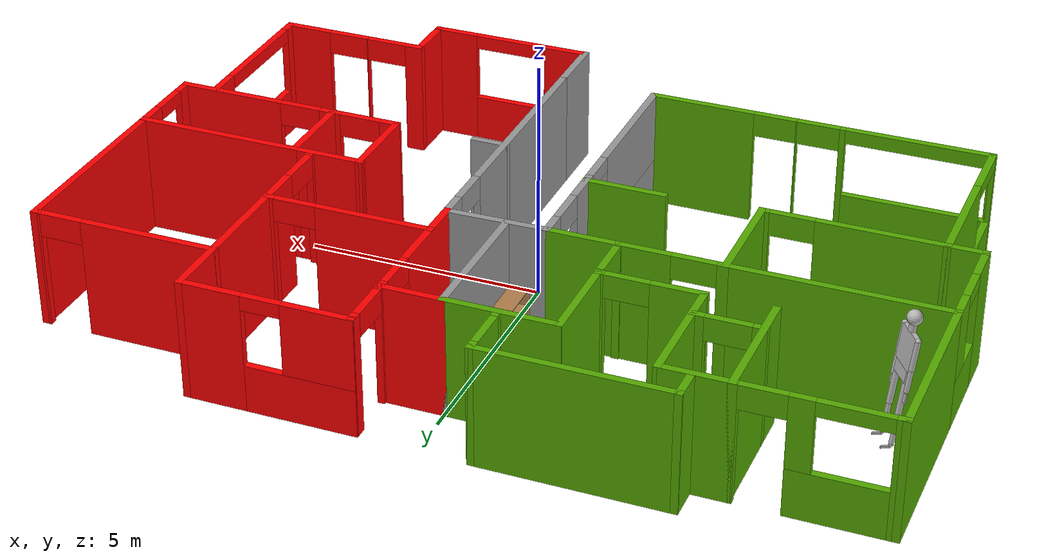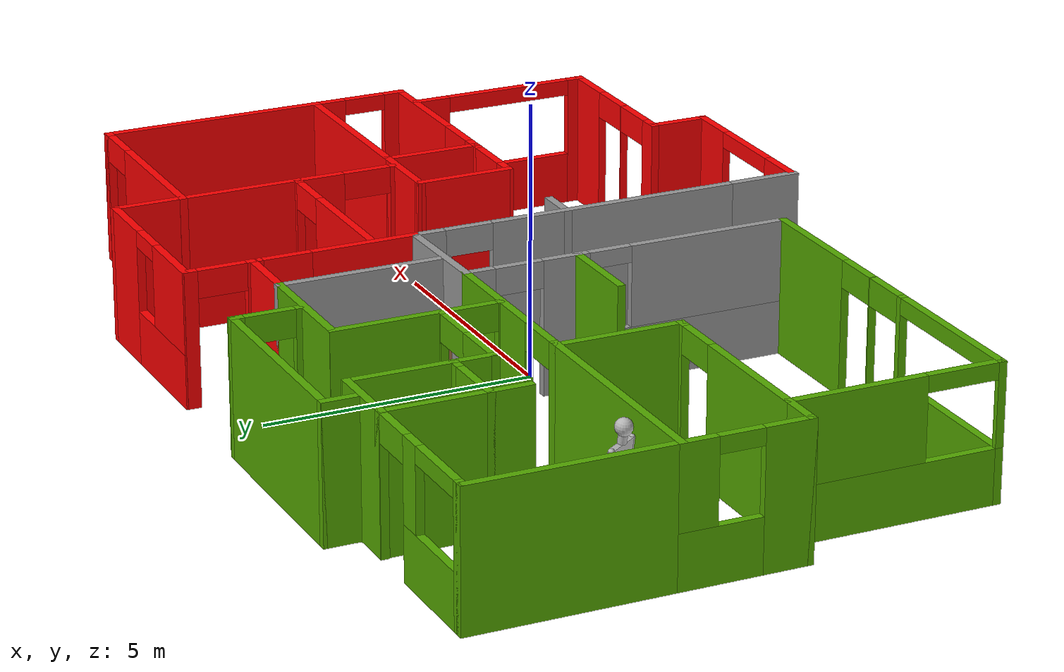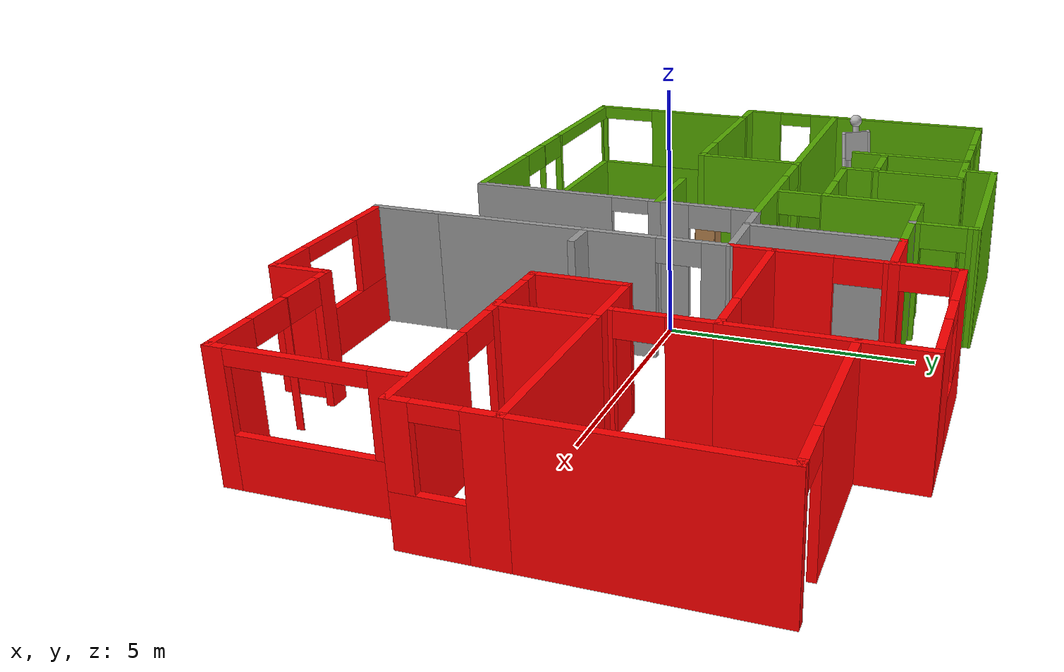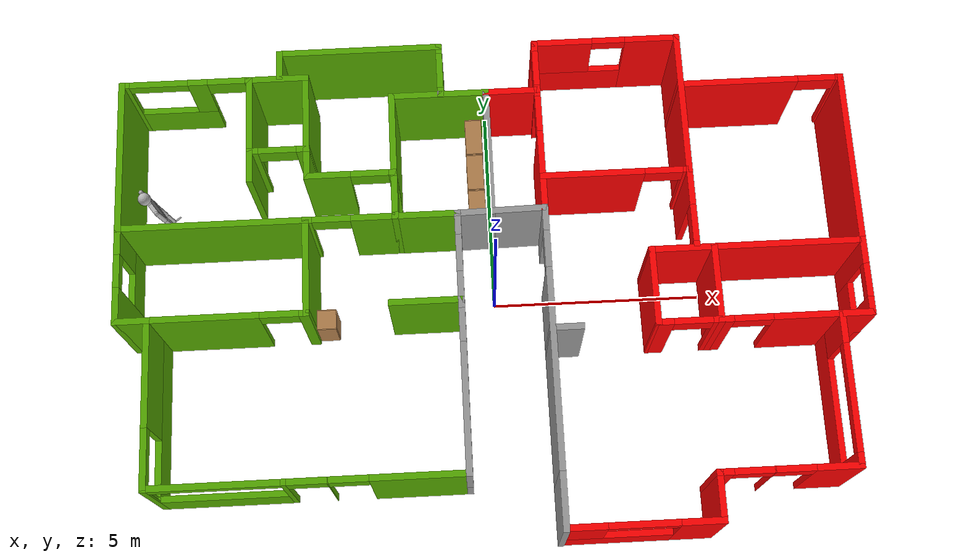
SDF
<sdf version="1.6">
 <world name="default">
  <light name="sun" type="directional">
   <cast_shadows>0</cast_shadows>
   <pose>0 0 10 0 -0 0</pose>
   <diffuse>0.8 0.8 0.8 1</diffuse>
   <specular>0.1 0.1 0.1 1</specular>
   <attenuation>
    <range>1000</range>
    <constant>0.9</constant>
    <linear>0.01</linear>
    <quadratic>0.001</quadratic>
   </attenuation>
   <direction>-0.5 0.5 -1</direction>
  </light>
  <gravity>0 0 -9.8</gravity>
  <magnetic_field>6e-06 2.3e-05 -4.2e-05</magnetic_field>
  <atmosphere type="adiabatic"/>
  <physics name="default_physics" default="0" type="ode">
   <max_step_size>0.01</max_step_size>
   <real_time_factor>1</real_time_factor>
   <real_time_update_rate>100</real_time_update_rate>
  </physics>
  <scene><ambient>0.4 0.4 0.4 1</ambient><background>0.7 0.7 0.7 1</background><shadows>0</shadows></scene>
  <spherical_coordinates>
   <surface_model>EARTH_WGS84</surface_model>
   <latitude_deg>0</latitude_deg>
   <longitude_deg>0</longitude_deg>
   <elevation>0</elevation>
   <heading_deg>0</heading_deg>
  </spherical_coordinates>
  <model name="1floorHouse">
   <link name="Wall_292">
    <pose>-4.3959 -4.53994 0 0 0 -3.14158</pose>
    <visual name="Wall_292_Visual_0">
     <pose>-2.52118 0 1.25 0 -0 0</pose>
     <geometry><box><size>2.25743 0.15 2.5</size></box></geometry>
     <material>
      <script><uri>file://media/materials/scripts/gazebo.material</uri><name>Gazebo/Grey</name></script>
      <ambient>0.333333 0.666667 0 1</ambient>
      <diffuse>0.7 0.7 0.7 1</diffuse>
      <specular>0.01 0.01 0.01 1</specular>
      <emissive>0 0 0 1</emissive>
     </material>
    </visual>
    <visual name="Wall_292_Visual_1">
     <pose>-0.479853 0 1.25 0 -0 0</pose>
     <geometry><box><size>0.025221 0.15 2.5</size></box></geometry>
     <material>
      <script><uri>file://media/materials/scripts/gazebo.material</uri><name>Gazebo/Grey</name></script>
      <ambient>0.333333 0.666667 0 1</ambient>
      <diffuse>0.7 0.7 0.7 1</diffuse>
      <specular>0.01 0.01 0.01 1</specular>
      <emissive>0 0 0 1</emissive>
     </material>
    </visual>
    <visual name="Wall_292_Visual_2">
     <pose>0.492301 0 1.25 0 -0 0</pose>
     <geometry><box><size>0.119086 0.15 2.5</size></box></geometry>
     <material>
      <script><uri>file://media/materials/scripts/gazebo.material</uri><name>Gazebo/Grey</name></script>
      <ambient>0.333333 0.666667 0 1</ambient>
      <diffuse>0.7 0.7 0.7 1</diffuse>
      <specular>0.01 0.01 0.01 1</specular>
      <emissive>0 0 0 1</emissive>
     </material>
    </visual>
    <visual name="Wall_292_Visual_3">
     <pose>2.10087 0 0.5 0 -0 0</pose>
     <geometry><box><size>3.09805 0.15 1</size></box></geometry>
     <material>
      <script><uri>file://media/materials/scripts/gazebo.material</uri><name>Gazebo/Grey</name></script>
      <ambient>0.333333 0.666667 0 1</ambient>
      <diffuse>0.7 0.7 0.7 1</diffuse>
      <specular>0.01 0.01 0.01 1</specular>
      <emissive>0 0 0 1</emissive>
     </material>
    </visual>
    <visual name="Wall_292_Visual_4">
     <pose>3.60087 0 1.75 0 -0 0</pose>
     <geometry><box><size>0.098047 0.15 1.5</size></box></geometry>
     <material>
      <script><uri>file://media/materials/scripts/gazebo.material</uri><name>Gazebo/Grey</name></script>
      <ambient>0.333333 0.666667 0 1</ambient>
      <diffuse>0.7 0.7 0.7 1</diffuse>
      <specular>0.01 0.01 0.01 1</specular>
      <emissive>0 0 0 1</emissive>
     </material>
    </visual>
    <visual name="Wall_292_Visual_5">
     <pose>-0.942463 0 2.25 0 -0 0</pose>
     <geometry><box><size>0.9 0.15 0.5</size></box></geometry>
     <material>
      <script><uri>file://media/materials/scripts/gazebo.material</uri><name>Gazebo/Grey</name></script>
      <ambient>0.333333 0.666667 0 1</ambient>
      <diffuse>0.7 0.7 0.7 1</diffuse>
      <specular>0.01 0.01 0.01 1</specular>
      <emissive>0 0 0 1</emissive>
     </material>
    </visual>
    <visual name="Wall_292_Visual_6">
     <pose>-0.017242 0 2.25 0 -0 0</pose>
     <geometry><box><size>0.9 0.15 0.5</size></box></geometry>
     <material>
      <script><uri>file://media/materials/scripts/gazebo.material</uri><name>Gazebo/Grey</name></script>
      <ambient>0.333333 0.666667 0 1</ambient>
      <diffuse>0.7 0.7 0.7 1</diffuse>
      <specular>0.01 0.01 0.01 1</specular>
      <emissive>0 0 0 1</emissive>
     </material>
    </visual>
    <visual name="Wall_292_Visual_7">
     <pose>2.05184 0 2.35 0 -0 0</pose>
     <geometry><box><size>3 0.15 0.3</size></box></geometry>
     <material>
      <script><uri>file://media/materials/scripts/gazebo.material</uri><name>Gazebo/Grey</name></script>
      <ambient>0.333333 0.666667 0 1</ambient>
      <diffuse>0.7 0.7 0.7 1</diffuse>
      <specular>0.01 0.01 0.01 1</specular>
      <emissive>0 0 0 1</emissive>
     </material>
    </visual>
    <collision name="Wall_292_Collision_1">
     <pose>-0.479853 0 1.25 0 -0 0</pose>
     <geometry><box><size>0.025221 0.15 2.5</size></box></geometry>
     <surface>
      <friction>
       <ode><mu>1</mu><mu2>1</mu2><fdir1>0 0 0</fdir1><slip1>0</slip1><slip2>0</slip2></ode>
       <torsional>
        <coefficient>1</coefficient>
        <patch_radius>0</patch_radius>
        <surface_radius>0</surface_radius>
        <use_patch_radius>1</use_patch_radius>
        <ode><slip>0</slip></ode>
       </torsional>
      </friction>
      <bounce><restitution_coefficient>0</restitution_coefficient><threshold>1e+06</threshold></bounce>
      <contact>
       <collide_without_contact>0</collide_without_contact>
       <collide_without_contact_bitmask>1</collide_without_contact_bitmask>
       <collide_bitmask>1</collide_bitmask>
       <ode>
        <soft_cfm>0</soft_cfm>
        <soft_erp>0.2</soft_erp>
        <kp>1e+13</kp>
        <kd>1</kd>
        <max_vel>0.01</max_vel>
        <min_depth>0</min_depth>
       </ode>
       <bullet>
        <split_impulse>1</split_impulse>
        <split_impulse_penetration_threshold>-0.01</split_impulse_penetration_threshold>
        <soft_cfm>0</soft_cfm>
        <soft_erp>0.2</soft_erp>
        <kp>1e+13</kp>
        <kd>1</kd>
       </bullet>
      </contact>
     </surface>
    </collision>
    <collision name="Wall_292_Collision_0">
     <pose>-2.52118 0 1.25 0 -0 0</pose>
     <geometry><box><size>2.25743 0.15 2.5</size></box></geometry>
     <surface>
      <friction>
       <ode><mu>1</mu><mu2>1</mu2><fdir1>0 0 0</fdir1><slip1>0</slip1><slip2>0</slip2></ode>
       <torsional>
        <coefficient>1</coefficient>
        <patch_radius>0</patch_radius>
        <surface_radius>0</surface_radius>
        <use_patch_radius>1</use_patch_radius>
        <ode><slip>0</slip></ode>
       </torsional>
      </friction>
      <bounce><restitution_coefficient>0</restitution_coefficient><threshold>1e+06</threshold></bounce>
      <contact>
       <collide_without_contact>0</collide_without_contact>
       <collide_without_contact_bitmask>1</collide_without_contact_bitmask>
       <collide_bitmask>1</collide_bitmask>
       <ode>
        <soft_cfm>0</soft_cfm>
        <soft_erp>0.2</soft_erp>
        <kp>1e+13</kp>
        <kd>1</kd>
        <max_vel>0.01</max_vel>
        <min_depth>0</min_depth>
       </ode>
       <bullet>
        <split_impulse>1</split_impulse>
        <split_impulse_penetration_threshold>-0.01</split_impulse_penetration_threshold>
        <soft_cfm>0</soft_cfm>
        <soft_erp>0.2</soft_erp>
        <kp>1e+13</kp>
        <kd>1</kd>
       </bullet>
      </contact>
     </surface>
    </collision>
    <collision name="Wall_292_Collision_2">
     <pose>0.492301 0 1.25 0 -0 0</pose>
     <geometry><box><size>0.119086 0.15 2.5</size></box></geometry>
     <surface>
      <friction>
       <ode><mu>1</mu><mu2>1</mu2><fdir1>0 0 0</fdir1><slip1>0</slip1><slip2>0</slip2></ode>
       <torsional>
        <coefficient>1</coefficient>
        <patch_radius>0</patch_radius>
        <surface_radius>0</surface_radius>
        <use_patch_radius>1</use_patch_radius>
        <ode><slip>0</slip></ode>
       </torsional>
      </friction>
      <bounce><restitution_coefficient>0</restitution_coefficient><threshold>1e+06</threshold></bounce>
      <contact>
       <collide_without_contact>0</collide_without_contact>
       <collide_without_contact_bitmask>1</collide_without_contact_bitmask>
       <collide_bitmask>1</collide_bitmask>
       <ode>
        <soft_cfm>0</soft_cfm>
        <soft_erp>0.2</soft_erp>
        <kp>1e+13</kp>
        <kd>1</kd>
        <max_vel>0.01</max_vel>
        <min_depth>0</min_depth>
       </ode>
       <bullet>
        <split_impulse>1</split_impulse>
        <split_impulse_penetration_threshold>-0.01</split_impulse_penetration_threshold>
        <soft_cfm>0</soft_cfm>
        <soft_erp>0.2</soft_erp>
        <kp>1e+13</kp>
        <kd>1</kd>
       </bullet>
      </contact>
     </surface>
    </collision>
    <collision name="Wall_292_Collision_3">
     <pose>2.10087 0 0.5 0 -0 0</pose>
     <geometry><box><size>3.09805 0.15 1</size></box></geometry>
     <surface>
      <friction>
       <ode><mu>1</mu><mu2>1</mu2><fdir1>0 0 0</fdir1><slip1>0</slip1><slip2>0</slip2></ode>
       <torsional>
        <coefficient>1</coefficient>
        <patch_radius>0</patch_radius>
        <surface_radius>0</surface_radius>
        <use_patch_radius>1</use_patch_radius>
        <ode><slip>0</slip></ode>
       </torsional>
      </friction>
      <bounce><restitution_coefficient>0</restitution_coefficient><threshold>1e+06</threshold></bounce>
      <contact>
       <collide_without_contact>0</collide_without_contact>
       <collide_without_contact_bitmask>1</collide_without_contact_bitmask>
       <collide_bitmask>1</collide_bitmask>
       <ode>
        <soft_cfm>0</soft_cfm>
        <soft_erp>0.2</soft_erp>
        <kp>1e+13</kp>
        <kd>1</kd>
        <max_vel>0.01</max_vel>
        <min_depth>0</min_depth>
       </ode>
       <bullet>
        <split_impulse>1</split_impulse>
        <split_impulse_penetration_threshold>-0.01</split_impulse_penetration_threshold>
        <soft_cfm>0</soft_cfm>
        <soft_erp>0.2</soft_erp>
        <kp>1e+13</kp>
        <kd>1</kd>
       </bullet>
      </contact>
     </surface>
    </collision>
    <collision name="Wall_292_Collision_4">
     <pose>3.60087 0 1.75 0 -0 0</pose>
     <geometry><box><size>0.098047 0.15 1.5</size></box></geometry>
     <surface>
      <friction>
       <ode><mu>1</mu><mu2>1</mu2><fdir1>0 0 0</fdir1><slip1>0</slip1><slip2>0</slip2></ode>
       <torsional>
        <coefficient>1</coefficient>
        <patch_radius>0</patch_radius>
        <surface_radius>0</surface_radius>
        <use_patch_radius>1</use_patch_radius>
        <ode><slip>0</slip></ode>
       </torsional>
      </friction>
      <bounce><restitution_coefficient>0</restitution_coefficient><threshold>1e+06</threshold></bounce>
      <contact>
       <collide_without_contact>0</collide_without_contact>
       <collide_without_contact_bitmask>1</collide_without_contact_bitmask>
       <collide_bitmask>1</collide_bitmask>
       <ode>
        <soft_cfm>0</soft_cfm>
        <soft_erp>0.2</soft_erp>
        <kp>1e+13</kp>
        <kd>1</kd>
        <max_vel>0.01</max_vel>
        <min_depth>0</min_depth>
       </ode>
       <bullet>
        <split_impulse>1</split_impulse>
        <split_impulse_penetration_threshold>-0.01</split_impulse_penetration_threshold>
        <soft_cfm>0</soft_cfm>
        <soft_erp>0.2</soft_erp>
        <kp>1e+13</kp>
        <kd>1</kd>
       </bullet>
      </contact>
     </surface>
    </collision>
    <collision name="Wall_292_Collision_5">
     <pose>-0.942463 0 2.25 0 -0 0</pose>
     <geometry><box><size>0.9 0.15 0.5</size></box></geometry>
     <surface>
      <friction>
       <ode><mu>1</mu><mu2>1</mu2><fdir1>0 0 0</fdir1><slip1>0</slip1><slip2>0</slip2></ode>
       <torsional>
        <coefficient>1</coefficient>
        <patch_radius>0</patch_radius>
        <surface_radius>0</surface_radius>
        <use_patch_radius>1</use_patch_radius>
        <ode><slip>0</slip></ode>
       </torsional>
      </friction>
      <bounce><restitution_coefficient>0</restitution_coefficient><threshold>1e+06</threshold></bounce>
      <contact>
       <collide_without_contact>0</collide_without_contact>
       <collide_without_contact_bitmask>1</collide_without_contact_bitmask>
       <collide_bitmask>1</collide_bitmask>
       <ode>
        <soft_cfm>0</soft_cfm>
        <soft_erp>0.2</soft_erp>
        <kp>1e+13</kp>
        <kd>1</kd>
        <max_vel>0.01</max_vel>
        <min_depth>0</min_depth>
       </ode>
       <bullet>
        <split_impulse>1</split_impulse>
        <split_impulse_penetration_threshold>-0.01</split_impulse_penetration_threshold>
        <soft_cfm>0</soft_cfm>
        <soft_erp>0.2</soft_erp>
        <kp>1e+13</kp>
        <kd>1</kd>
       </bullet>
      </contact>
     </surface>
    </collision>
    <collision name="Wall_292_Collision_7">
     <pose>2.05184 0 2.35 0 -0 0</pose>
     <geometry><box><size>3 0.15 0.3</size></box></geometry>
     <surface>
      <friction>
       <ode><mu>1</mu><mu2>1</mu2><fdir1>0 0 0</fdir1><slip1>0</slip1><slip2>0</slip2></ode>
       <torsional>
        <coefficient>1</coefficient>
        <patch_radius>0</patch_radius>
        <surface_radius>0</surface_radius>
        <use_patch_radius>1</use_patch_radius>
        <ode><slip>0</slip></ode>
       </torsional>
      </friction>
      <bounce><restitution_coefficient>0</restitution_coefficient><threshold>1e+06</threshold></bounce>
      <contact>
       <collide_without_contact>0</collide_without_contact>
       <collide_without_contact_bitmask>1</collide_without_contact_bitmask>
       <collide_bitmask>1</collide_bitmask>
       <ode>
        <soft_cfm>0</soft_cfm>
        <soft_erp>0.2</soft_erp>
        <kp>1e+13</kp>
        <kd>1</kd>
        <max_vel>0.01</max_vel>
        <min_depth>0</min_depth>
       </ode>
       <bullet>
        <split_impulse>1</split_impulse>
        <split_impulse_penetration_threshold>-0.01</split_impulse_penetration_threshold>
        <soft_cfm>0</soft_cfm>
        <soft_erp>0.2</soft_erp>
        <kp>1e+13</kp>
        <kd>1</kd>
       </bullet>
      </contact>
     </surface>
    </collision>
    <collision name="Wall_292_Collision_6">
     <pose>-0.017242 0 2.25 0 -0 0</pose>
     <geometry><box><size>0.9 0.15 0.5</size></box></geometry>
     <surface>
      <friction>
       <ode><mu>1</mu><mu2>1</mu2><fdir1>0 0 0</fdir1><slip1>0</slip1><slip2>0</slip2></ode>
       <torsional>
        <coefficient>1</coefficient>
        <patch_radius>0</patch_radius>
        <surface_radius>0</surface_radius>
        <use_patch_radius>1</use_patch_radius>
        <ode><slip>0</slip></ode>
       </torsional>
      </friction>
      <bounce><restitution_coefficient>0</restitution_coefficient><threshold>1e+06</threshold></bounce>
      <contact>
       <collide_without_contact>0</collide_without_contact>
       <collide_without_contact_bitmask>1</collide_without_contact_bitmask>
       <collide_bitmask>1</collide_bitmask>
       <ode>
        <soft_cfm>0</soft_cfm>
        <soft_erp>0.2</soft_erp>
        <kp>1e+13</kp>
        <kd>1</kd>
        <max_vel>0.01</max_vel>
        <min_depth>0</min_depth>
       </ode>
       <bullet>
        <split_impulse>1</split_impulse>
        <split_impulse_penetration_threshold>-0.01</split_impulse_penetration_threshold>
        <soft_cfm>0</soft_cfm>
        <soft_erp>0.2</soft_erp>
        <kp>1e+13</kp>
        <kd>1</kd>
       </bullet>
      </contact>
     </surface>
    </collision>
   </link>
   <link name="Wall_293">
    <pose>-7.97079 -2.615 0 0 -0 1.5708</pose>
    <visual name="Wall_293_Visual_0">
     <pose>-1.97712 0 1.25 0 -0 0</pose>
     <geometry><box><size>0.045764 0.15 2.5</size></box></geometry>
     <material>
      <script><uri>file://media/materials/scripts/gazebo.material</uri><name>Gazebo/Grey</name></script>
      <ambient>0.333333 0.666667 0 1</ambient>
      <diffuse>0.7 0.7 0.7 1</diffuse>
      <specular>0.01 0.01 0.01 1</specular>
      <emissive>0 0 0 1</emissive>
     </material>
    </visual>
    <visual name="Wall_293_Visual_1">
     <pose>0.022882 0 0.5 0 -0 0</pose>
     <geometry><box><size>3.95424 0.15 1</size></box></geometry>
     <material>
      <script><uri>file://media/materials/scripts/gazebo.material</uri><name>Gazebo/Grey</name></script>
      <ambient>0.333333 0.666667 0 1</ambient>
      <diffuse>0.7 0.7 0.7 1</diffuse>
      <specular>0.01 0.01 0.01 1</specular>
      <emissive>0 0 0 1</emissive>
     </material>
    </visual>
    <visual name="Wall_293_Visual_2">
     <pose>0.722882 0 1.75 0 -0 0</pose>
     <geometry><box><size>2.55424 0.15 1.5</size></box></geometry>
     <material>
      <script><uri>file://media/materials/scripts/gazebo.material</uri><name>Gazebo/Grey</name></script>
      <ambient>0.333333 0.666667 0 1</ambient>
      <diffuse>0.7 0.7 0.7 1</diffuse>
      <specular>0.01 0.01 0.01 1</specular>
      <emissive>0 0 0 1</emissive>
     </material>
    </visual>
    <visual name="Wall_293_Visual_3">
     <pose>-1.25424 0 2.35 0 -0 0</pose>
     <geometry><box><size>1.4 0.15 0.3</size></box></geometry>
     <material>
      <script><uri>file://media/materials/scripts/gazebo.material</uri><name>Gazebo/Grey</name></script>
      <ambient>0.333333 0.666667 0 1</ambient>
      <diffuse>0.7 0.7 0.7 1</diffuse>
      <specular>0.01 0.01 0.01 1</specular>
      <emissive>0 0 0 1</emissive>
     </material>
    </visual>
    <collision name="Wall_293_Collision_0">
     <pose>-1.97712 0 1.25 0 -0 0</pose>
     <geometry><box><size>0.045764 0.15 2.5</size></box></geometry>
     <surface>
      <friction>
       <ode><mu>1</mu><mu2>1</mu2><fdir1>0 0 0</fdir1><slip1>0</slip1><slip2>0</slip2></ode>
       <torsional>
        <coefficient>1</coefficient>
        <patch_radius>0</patch_radius>
        <surface_radius>0</surface_radius>
        <use_patch_radius>1</use_patch_radius>
        <ode><slip>0</slip></ode>
       </torsional>
      </friction>
      <bounce><restitution_coefficient>0</restitution_coefficient><threshold>1e+06</threshold></bounce>
      <contact>
       <collide_without_contact>0</collide_without_contact>
       <collide_without_contact_bitmask>1</collide_without_contact_bitmask>
       <collide_bitmask>1</collide_bitmask>
       <ode>
        <soft_cfm>0</soft_cfm>
        <soft_erp>0.2</soft_erp>
        <kp>1e+13</kp>
        <kd>1</kd>
        <max_vel>0.01</max_vel>
        <min_depth>0</min_depth>
       </ode>
       <bullet>
        <split_impulse>1</split_impulse>
        <split_impulse_penetration_threshold>-0.01</split_impulse_penetration_threshold>
        <soft_cfm>0</soft_cfm>
        <soft_erp>0.2</soft_erp>
        <kp>1e+13</kp>
        <kd>1</kd>
       </bullet>
      </contact>
     </surface>
    </collision>
    <collision name="Wall_293_Collision_1">
     <pose>0.022882 0 0.5 0 -0 0</pose>
     <geometry><box><size>3.95424 0.15 1</size></box></geometry>
     <surface>
      <friction>
       <ode><mu>1</mu><mu2>1</mu2><fdir1>0 0 0</fdir1><slip1>0</slip1><slip2>0</slip2></ode>
       <torsional>
        <coefficient>1</coefficient>
        <patch_radius>0</patch_radius>
        <surface_radius>0</surface_radius>
        <use_patch_radius>1</use_patch_radius>
        <ode><slip>0</slip></ode>
       </torsional>
      </friction>
      <bounce><restitution_coefficient>0</restitution_coefficient><threshold>1e+06</threshold></bounce>
      <contact>
       <collide_without_contact>0</collide_without_contact>
       <collide_without_contact_bitmask>1</collide_without_contact_bitmask>
       <collide_bitmask>1</collide_bitmask>
       <ode>
        <soft_cfm>0</soft_cfm>
        <soft_erp>0.2</soft_erp>
        <kp>1e+13</kp>
        <kd>1</kd>
        <max_vel>0.01</max_vel>
        <min_depth>0</min_depth>
       </ode>
       <bullet>
        <split_impulse>1</split_impulse>
        <split_impulse_penetration_threshold>-0.01</split_impulse_penetration_threshold>
        <soft_cfm>0</soft_cfm>
        <soft_erp>0.2</soft_erp>
        <kp>1e+13</kp>
        <kd>1</kd>
       </bullet>
      </contact>
     </surface>
    </collision>
    <collision name="Wall_293_Collision_2">
     <pose>0.722882 0 1.75 0 -0 0</pose>
     <geometry><box><size>2.55424 0.15 1.5</size></box></geometry>
     <surface>
      <friction>
       <ode><mu>1</mu><mu2>1</mu2><fdir1>0 0 0</fdir1><slip1>0</slip1><slip2>0</slip2></ode>
       <torsional>
        <coefficient>1</coefficient>
        <patch_radius>0</patch_radius>
        <surface_radius>0</surface_radius>
        <use_patch_radius>1</use_patch_radius>
        <ode><slip>0</slip></ode>
       </torsional>
      </friction>
      <bounce><restitution_coefficient>0</restitution_coefficient><threshold>1e+06</threshold></bounce>
      <contact>
       <collide_without_contact>0</collide_without_contact>
       <collide_without_contact_bitmask>1</collide_without_contact_bitmask>
       <collide_bitmask>1</collide_bitmask>
       <ode>
        <soft_cfm>0</soft_cfm>
        <soft_erp>0.2</soft_erp>
        <kp>1e+13</kp>
        <kd>1</kd>
        <max_vel>0.01</max_vel>
        <min_depth>0</min_depth>
       </ode>
       <bullet>
        <split_impulse>1</split_impulse>
        <split_impulse_penetration_threshold>-0.01</split_impulse_penetration_threshold>
        <soft_cfm>0</soft_cfm>
        <soft_erp>0.2</soft_erp>
        <kp>1e+13</kp>
        <kd>1</kd>
       </bullet>
      </contact>
     </surface>
    </collision>
    <collision name="Wall_293_Collision_3">
     <pose>-1.25424 0 2.35 0 -0 0</pose>
     <geometry><box><size>1.4 0.15 0.3</size></box></geometry>
     <surface>
      <friction>
       <ode><mu>1</mu><mu2>1</mu2><fdir1>0 0 0</fdir1><slip1>0</slip1><slip2>0</slip2></ode>
       <torsional>
        <coefficient>1</coefficient>
        <patch_radius>0</patch_radius>
        <surface_radius>0</surface_radius>
        <use_patch_radius>1</use_patch_radius>
        <ode><slip>0</slip></ode>
       </torsional>
      </friction>
      <bounce><restitution_coefficient>0</restitution_coefficient><threshold>1e+06</threshold></bounce>
      <contact>
       <collide_without_contact>0</collide_without_contact>
       <collide_without_contact_bitmask>1</collide_without_contact_bitmask>
       <collide_bitmask>1</collide_bitmask>
       <ode>
        <soft_cfm>0</soft_cfm>
        <soft_erp>0.2</soft_erp>
        <kp>1e+13</kp>
        <kd>1</kd>
        <max_vel>0.01</max_vel>
        <min_depth>0</min_depth>
       </ode>
       <bullet>
        <split_impulse>1</split_impulse>
        <split_impulse_penetration_threshold>-0.01</split_impulse_penetration_threshold>
        <soft_cfm>0</soft_cfm>
        <soft_erp>0.2</soft_erp>
        <kp>1e+13</kp>
        <kd>1</kd>
       </bullet>
      </contact>
     </surface>
    </collision>
   </link>
   <link name="Wall_294">
    <pose>-8.3305 -0.690004 0 0 -0 3.14159</pose>
    <visual name="Wall_294_Visual">
     <pose>0 0 1.25 0 -0 0</pose>
     <geometry><box><size>0.86941 0.15 2.5</size></box></geometry>
     <material>
      <script><uri>file://media/materials/scripts/gazebo.material</uri><name>Gazebo/Grey</name></script>
      <ambient>0.333333 0.666667 0 1</ambient>
      <diffuse>0.7 0.7 0.7 1</diffuse>
      <specular>0.01 0.01 0.01 1</specular>
      <emissive>0 0 0 1</emissive>
     </material>
    </visual>
    <collision name="Wall_294_Collision">
     <pose>0 0 1.25 0 -0 0</pose>
     <geometry><box><size>0.86941 0.15 2.5</size></box></geometry>
     <surface>
      <friction>
       <ode><mu>1</mu><mu2>1</mu2><fdir1>0 0 0</fdir1><slip1>0</slip1><slip2>0</slip2></ode>
       <torsional>
        <coefficient>1</coefficient>
        <patch_radius>0</patch_radius>
        <surface_radius>0</surface_radius>
        <use_patch_radius>1</use_patch_radius>
        <ode><slip>0</slip></ode>
       </torsional>
      </friction>
      <bounce><restitution_coefficient>0</restitution_coefficient><threshold>1e+06</threshold></bounce>
      <contact>
       <collide_without_contact>0</collide_without_contact>
       <collide_without_contact_bitmask>1</collide_without_contact_bitmask>
       <collide_bitmask>1</collide_bitmask>
       <ode>
        <soft_cfm>0</soft_cfm>
        <soft_erp>0.2</soft_erp>
        <kp>1e+13</kp>
        <kd>1</kd>
        <max_vel>0.01</max_vel>
        <min_depth>0</min_depth>
       </ode>
       <bullet>
        <split_impulse>1</split_impulse>
        <split_impulse_penetration_threshold>-0.01</split_impulse_penetration_threshold>
        <soft_cfm>0</soft_cfm>
        <soft_erp>0.2</soft_erp>
        <kp>1e+13</kp>
        <kd>1</kd>
       </bullet>
      </contact>
     </surface>
    </collision>
   </link>
   <link name="Wall_295">
    <pose>-8.69021 0.434996 0 0 -0 1.5708</pose>
    <visual name="Wall_295_Visual_0">
     <pose>-0.748437 0 1.25 0 -0 0</pose>
     <geometry><box><size>0.903127 0.15 2.5</size></box></geometry>
     <material>
      <script><uri>file://media/materials/scripts/gazebo.material</uri><name>Gazebo/Grey</name></script>
      <ambient>0.333333 0.666667 0 1</ambient>
      <diffuse>0.7 0.7 0.7 1</diffuse>
      <specular>0.01 0.01 0.01 1</specular>
      <emissive>0 0 0 1</emissive>
     </material>
    </visual>
    <visual name="Wall_295_Visual_1">
     <pose>0.451563 0 0.5 0 -0 0</pose>
     <geometry><box><size>1.49687 0.15 1</size></box></geometry>
     <material>
      <script><uri>file://media/materials/scripts/gazebo.material</uri><name>Gazebo/Grey</name></script>
      <ambient>0.333333 0.666667 0 1</ambient>
      <diffuse>0.7 0.7 0.7 1</diffuse>
      <specular>0.01 0.01 0.01 1</specular>
      <emissive>0 0 0 1</emissive>
     </material>
    </visual>
    <visual name="Wall_295_Visual_2">
     <pose>0.851563 0 1.75 0 -0 0</pose>
     <geometry><box><size>0.696873 0.15 1.5</size></box></geometry>
     <material>
      <script><uri>file://media/materials/scripts/gazebo.material</uri><name>Gazebo/Grey</name></script>
      <ambient>0.333333 0.666667 0 1</ambient>
      <diffuse>0.7 0.7 0.7 1</diffuse>
      <specular>0.01 0.01 0.01 1</specular>
      <emissive>0 0 0 1</emissive>
     </material>
    </visual>
    <visual name="Wall_295_Visual_3">
     <pose>0.103127 0 2.35 0 -0 0</pose>
     <geometry><box><size>0.8 0.15 0.3</size></box></geometry>
     <material>
      <script><uri>file://media/materials/scripts/gazebo.material</uri><name>Gazebo/Grey</name></script>
      <ambient>0.333333 0.666667 0 1</ambient>
      <diffuse>0.7 0.7 0.7 1</diffuse>
      <specular>0.01 0.01 0.01 1</specular>
      <emissive>0 0 0 1</emissive>
     </material>
    </visual>
    <collision name="Wall_295_Collision_0">
     <pose>-0.748437 0 1.25 0 -0 0</pose>
     <geometry><box><size>0.903127 0.15 2.5</size></box></geometry>
     <surface>
      <friction>
       <ode><mu>1</mu><mu2>1</mu2><fdir1>0 0 0</fdir1><slip1>0</slip1><slip2>0</slip2></ode>
       <torsional>
        <coefficient>1</coefficient>
        <patch_radius>0</patch_radius>
        <surface_radius>0</surface_radius>
        <use_patch_radius>1</use_patch_radius>
        <ode><slip>0</slip></ode>
       </torsional>
      </friction>
      <bounce><restitution_coefficient>0</restitution_coefficient><threshold>1e+06</threshold></bounce>
      <contact>
       <collide_without_contact>0</collide_without_contact>
       <collide_without_contact_bitmask>1</collide_without_contact_bitmask>
       <collide_bitmask>1</collide_bitmask>
       <ode>
        <soft_cfm>0</soft_cfm>
        <soft_erp>0.2</soft_erp>
        <kp>1e+13</kp>
        <kd>1</kd>
        <max_vel>0.01</max_vel>
        <min_depth>0</min_depth>
       </ode>
       <bullet>
        <split_impulse>1</split_impulse>
        <split_impulse_penetration_threshold>-0.01</split_impulse_penetration_threshold>
        <soft_cfm>0</soft_cfm>
        <soft_erp>0.2</soft_erp>
        <kp>1e+13</kp>
        <kd>1</kd>
       </bullet>
      </contact>
     </surface>
    </collision>
    <collision name="Wall_295_Collision_1">
     <pose>0.451563 0 0.5 0 -0 0</pose>
     <geometry><box><size>1.49687 0.15 1</size></box></geometry>
     <surface>
      <friction>
       <ode><mu>1</mu><mu2>1</mu2><fdir1>0 0 0</fdir1><slip1>0</slip1><slip2>0</slip2></ode>
       <torsional>
        <coefficient>1</coefficient>
        <patch_radius>0</patch_radius>
        <surface_radius>0</surface_radius>
        <use_patch_radius>1</use_patch_radius>
        <ode><slip>0</slip></ode>
       </torsional>
      </friction>
      <bounce><restitution_coefficient>0</restitution_coefficient><threshold>1e+06</threshold></bounce>
      <contact>
       <collide_without_contact>0</collide_without_contact>
       <collide_without_contact_bitmask>1</collide_without_contact_bitmask>
       <collide_bitmask>1</collide_bitmask>
       <ode>
        <soft_cfm>0</soft_cfm>
        <soft_erp>0.2</soft_erp>
        <kp>1e+13</kp>
        <kd>1</kd>
        <max_vel>0.01</max_vel>
        <min_depth>0</min_depth>
       </ode>
       <bullet>
        <split_impulse>1</split_impulse>
        <split_impulse_penetration_threshold>-0.01</split_impulse_penetration_threshold>
        <soft_cfm>0</soft_cfm>
        <soft_erp>0.2</soft_erp>
        <kp>1e+13</kp>
        <kd>1</kd>
       </bullet>
      </contact>
     </surface>
    </collision>
    <collision name="Wall_295_Collision_2">
     <pose>0.851563 0 1.75 0 -0 0</pose>
     <geometry><box><size>0.696873 0.15 1.5</size></box></geometry>
     <surface>
      <friction>
       <ode><mu>1</mu><mu2>1</mu2><fdir1>0 0 0</fdir1><slip1>0</slip1><slip2>0</slip2></ode>
       <torsional>
        <coefficient>1</coefficient>
        <patch_radius>0</patch_radius>
        <surface_radius>0</surface_radius>
        <use_patch_radius>1</use_patch_radius>
        <ode><slip>0</slip></ode>
       </torsional>
      </friction>
      <bounce><restitution_coefficient>0</restitution_coefficient><threshold>1e+06</threshold></bounce>
      <contact>
       <collide_without_contact>0</collide_without_contact>
       <collide_without_contact_bitmask>1</collide_without_contact_bitmask>
       <collide_bitmask>1</collide_bitmask>
       <ode>
        <soft_cfm>0</soft_cfm>
        <soft_erp>0.2</soft_erp>
        <kp>1e+13</kp>
        <kd>1</kd>
        <max_vel>0.01</max_vel>
        <min_depth>0</min_depth>
       </ode>
       <bullet>
        <split_impulse>1</split_impulse>
        <split_impulse_penetration_threshold>-0.01</split_impulse_penetration_threshold>
        <soft_cfm>0</soft_cfm>
        <soft_erp>0.2</soft_erp>
        <kp>1e+13</kp>
        <kd>1</kd>
       </bullet>
      </contact>
     </surface>
    </collision>
    <collision name="Wall_295_Collision_3">
     <pose>0.103127 0 2.35 0 -0 0</pose>
     <geometry><box><size>0.8 0.15 0.3</size></box></geometry>
     <surface>
      <friction>
       <ode><mu>1</mu><mu2>1</mu2><fdir1>0 0 0</fdir1><slip1>0</slip1><slip2>0</slip2></ode>
       <torsional>
        <coefficient>1</coefficient>
        <patch_radius>0</patch_radius>
        <surface_radius>0</surface_radius>
        <use_patch_radius>1</use_patch_radius>
        <ode><slip>0</slip></ode>
       </torsional>
      </friction>
      <bounce><restitution_coefficient>0</restitution_coefficient><threshold>1e+06</threshold></bounce>
      <contact>
       <collide_without_contact>0</collide_without_contact>
       <collide_without_contact_bitmask>1</collide_without_contact_bitmask>
       <collide_bitmask>1</collide_bitmask>
       <ode>
        <soft_cfm>0</soft_cfm>
        <soft_erp>0.2</soft_erp>
        <kp>1e+13</kp>
        <kd>1</kd>
        <max_vel>0.01</max_vel>
        <min_depth>0</min_depth>
       </ode>
       <bullet>
        <split_impulse>1</split_impulse>
        <split_impulse_penetration_threshold>-0.01</split_impulse_penetration_threshold>
        <soft_cfm>0</soft_cfm>
        <soft_erp>0.2</soft_erp>
        <kp>1e+13</kp>
        <kd>1</kd>
       </bullet>
      </contact>
     </surface>
    </collision>
   </link>
   <link name="Wall_296">
    <pose>-6.5152 1.56 0 0 -0 0</pose>
    <visual name="Wall_296_Visual">
     <pose>0 0 1.25 0 -0 0</pose>
     <geometry><box><size>4.5 0.15 2.5</size></box></geometry>
     <material>
      <script><uri>file://media/materials/scripts/gazebo.material</uri><name>Gazebo/Grey</name></script>
      <ambient>0.333333 0.666667 0 1</ambient>
      <diffuse>0.7 0.7 0.7 1</diffuse>
      <specular>0.01 0.01 0.01 1</specular>
      <emissive>0 0 0 1</emissive>
     </material>
    </visual>
    <collision name="Wall_296_Collision">
     <pose>0 0 1.25 0 -0 0</pose>
     <geometry><box><size>4.5 0.15 2.5</size></box></geometry>
     <surface>
      <friction>
       <ode><mu>1</mu><mu2>1</mu2><fdir1>0 0 0</fdir1><slip1>0</slip1><slip2>0</slip2></ode>
       <torsional>
        <coefficient>1</coefficient>
        <patch_radius>0</patch_radius>
        <surface_radius>0</surface_radius>
        <use_patch_radius>1</use_patch_radius>
        <ode><slip>0</slip></ode>
       </torsional>
      </friction>
      <bounce><restitution_coefficient>0</restitution_coefficient><threshold>1e+06</threshold></bounce>
      <contact>
       <collide_without_contact>0</collide_without_contact>
       <collide_without_contact_bitmask>1</collide_without_contact_bitmask>
       <collide_bitmask>1</collide_bitmask>
       <ode>
        <soft_cfm>0</soft_cfm>
        <soft_erp>0.2</soft_erp>
        <kp>1e+13</kp>
        <kd>1</kd>
        <max_vel>0.01</max_vel>
        <min_depth>0</min_depth>
       </ode>
       <bullet>
        <split_impulse>1</split_impulse>
        <split_impulse_penetration_threshold>-0.01</split_impulse_penetration_threshold>
        <soft_cfm>0</soft_cfm>
        <soft_erp>0.2</soft_erp>
        <kp>1e+13</kp>
        <kd>1</kd>
       </bullet>
      </contact>
     </surface>
    </collision>
   </link>
   <link name="Wall_297">
    <pose>-4.34021 0.434996 0 0 0 -1.5708</pose>
    <visual name="Wall_297_Visual">
     <pose>0 0 1.25 0 -0 0</pose>
     <geometry><box><size>2.4 0.15 2.5</size></box></geometry>
     <material>
      <script><uri>file://media/materials/scripts/gazebo.material</uri><name>Gazebo/Grey</name></script>
      <ambient>0.333333 0.666667 0 1</ambient>
      <diffuse>0.7 0.7 0.7 1</diffuse>
      <specular>0.01 0.01 0.01 1</specular>
      <emissive>0 0 0 1</emissive>
     </material>
    </visual>
    <collision name="Wall_297_Collision">
     <pose>0 0 1.25 0 -0 0</pose>
     <geometry><box><size>2.4 0.15 2.5</size></box></geometry>
     <surface>
      <friction>
       <ode><mu>1</mu><mu2>1</mu2><fdir1>0 0 0</fdir1><slip1>0</slip1><slip2>0</slip2></ode>
       <torsional>
        <coefficient>1</coefficient>
        <patch_radius>0</patch_radius>
        <surface_radius>0</surface_radius>
        <use_patch_radius>1</use_patch_radius>
        <ode><slip>0</slip></ode>
       </torsional>
      </friction>
      <bounce><restitution_coefficient>0</restitution_coefficient><threshold>1e+06</threshold></bounce>
      <contact>
       <collide_without_contact>0</collide_without_contact>
       <collide_without_contact_bitmask>1</collide_without_contact_bitmask>
       <collide_bitmask>1</collide_bitmask>
       <ode>
        <soft_cfm>0</soft_cfm>
        <soft_erp>0.2</soft_erp>
        <kp>1e+13</kp>
        <kd>1</kd>
        <max_vel>0.01</max_vel>
        <min_depth>0</min_depth>
       </ode>
       <bullet>
        <split_impulse>1</split_impulse>
        <split_impulse_penetration_threshold>-0.01</split_impulse_penetration_threshold>
        <soft_cfm>0</soft_cfm>
        <soft_erp>0.2</soft_erp>
        <kp>1e+13</kp>
        <kd>1</kd>
       </bullet>
      </contact>
     </surface>
    </collision>
   </link>
   <link name="Wall_298">
    <pose>-6.1555 -0.690004 0 0 -0 3.14159</pose>
    <visual name="Wall_298_Visual_0">
     <pose>-1.77022 0 1.25 0 -0 0</pose>
     <geometry><box><size>0.240159 0.15 2.5</size></box></geometry>
     <material>
      <script><uri>file://media/materials/scripts/gazebo.material</uri><name>Gazebo/Grey</name></script>
      <ambient>0.333333 0.666667 0 1</ambient>
      <diffuse>0.7 0.7 0.7 1</diffuse>
      <specular>0.01 0.01 0.01 1</specular>
      <emissive>0 0 0 1</emissive>
     </material>
    </visual>
    <visual name="Wall_298_Visual_1">
     <pose>0.570079 0 1.25 0 -0 0</pose>
     <geometry><box><size>2.64043 0.15 2.5</size></box></geometry>
     <material>
      <script><uri>file://media/materials/scripts/gazebo.material</uri><name>Gazebo/Grey</name></script>
      <ambient>0.333333 0.666667 0 1</ambient>
      <diffuse>0.7 0.7 0.7 1</diffuse>
      <specular>0.01 0.01 0.01 1</specular>
      <emissive>0 0 0 1</emissive>
     </material>
    </visual>
    <visual name="Wall_298_Visual_2">
     <pose>-1.20014 0 2.25 0 -0 0</pose>
     <geometry><box><size>0.9 0.15 0.5</size></box></geometry>
     <material>
      <script><uri>file://media/materials/scripts/gazebo.material</uri><name>Gazebo/Grey</name></script>
      <ambient>0.333333 0.666667 0 1</ambient>
      <diffuse>0.7 0.7 0.7 1</diffuse>
      <specular>0.01 0.01 0.01 1</specular>
      <emissive>0 0 0 1</emissive>
     </material>
    </visual>
    <collision name="Wall_298_Collision_0">
     <pose>-1.77022 0 1.25 0 -0 0</pose>
     <geometry><box><size>0.240159 0.15 2.5</size></box></geometry>
     <surface>
      <friction>
       <ode><mu>1</mu><mu2>1</mu2><fdir1>0 0 0</fdir1><slip1>0</slip1><slip2>0</slip2></ode>
       <torsional>
        <coefficient>1</coefficient>
        <patch_radius>0</patch_radius>
        <surface_radius>0</surface_radius>
        <use_patch_radius>1</use_patch_radius>
        <ode><slip>0</slip></ode>
       </torsional>
      </friction>
      <bounce><restitution_coefficient>0</restitution_coefficient><threshold>1e+06</threshold></bounce>
      <contact>
       <collide_without_contact>0</collide_without_contact>
       <collide_without_contact_bitmask>1</collide_without_contact_bitmask>
       <collide_bitmask>1</collide_bitmask>
       <ode>
        <soft_cfm>0</soft_cfm>
        <soft_erp>0.2</soft_erp>
        <kp>1e+13</kp>
        <kd>1</kd>
        <max_vel>0.01</max_vel>
        <min_depth>0</min_depth>
       </ode>
       <bullet>
        <split_impulse>1</split_impulse>
        <split_impulse_penetration_threshold>-0.01</split_impulse_penetration_threshold>
        <soft_cfm>0</soft_cfm>
        <soft_erp>0.2</soft_erp>
        <kp>1e+13</kp>
        <kd>1</kd>
       </bullet>
      </contact>
     </surface>
    </collision>
    <collision name="Wall_298_Collision_1">
     <pose>0.570079 0 1.25 0 -0 0</pose>
     <geometry><box><size>2.64043 0.15 2.5</size></box></geometry>
     <surface>
      <friction>
       <ode><mu>1</mu><mu2>1</mu2><fdir1>0 0 0</fdir1><slip1>0</slip1><slip2>0</slip2></ode>
       <torsional>
        <coefficient>1</coefficient>
        <patch_radius>0</patch_radius>
        <surface_radius>0</surface_radius>
        <use_patch_radius>1</use_patch_radius>
        <ode><slip>0</slip></ode>
       </torsional>
      </friction>
      <bounce><restitution_coefficient>0</restitution_coefficient><threshold>1e+06</threshold></bounce>
      <contact>
       <collide_without_contact>0</collide_without_contact>
       <collide_without_contact_bitmask>1</collide_without_contact_bitmask>
       <collide_bitmask>1</collide_bitmask>
       <ode>
        <soft_cfm>0</soft_cfm>
        <soft_erp>0.2</soft_erp>
        <kp>1e+13</kp>
        <kd>1</kd>
        <max_vel>0.01</max_vel>
        <min_depth>0</min_depth>
       </ode>
       <bullet>
        <split_impulse>1</split_impulse>
        <split_impulse_penetration_threshold>-0.01</split_impulse_penetration_threshold>
        <soft_cfm>0</soft_cfm>
        <soft_erp>0.2</soft_erp>
        <kp>1e+13</kp>
        <kd>1</kd>
       </bullet>
      </contact>
     </surface>
    </collision>
    <collision name="Wall_298_Collision_2">
     <pose>-1.20014 0 2.25 0 -0 0</pose>
     <geometry><box><size>0.9 0.15 0.5</size></box></geometry>
     <surface>
      <friction>
       <ode><mu>1</mu><mu2>1</mu2><fdir1>0 0 0</fdir1><slip1>0</slip1><slip2>0</slip2></ode>
       <torsional>
        <coefficient>1</coefficient>
        <patch_radius>0</patch_radius>
        <surface_radius>0</surface_radius>
        <use_patch_radius>1</use_patch_radius>
        <ode><slip>0</slip></ode>
       </torsional>
      </friction>
      <bounce><restitution_coefficient>0</restitution_coefficient><threshold>1e+06</threshold></bounce>
      <contact>
       <collide_without_contact>0</collide_without_contact>
       <collide_without_contact_bitmask>1</collide_without_contact_bitmask>
       <collide_bitmask>1</collide_bitmask>
       <ode>
        <soft_cfm>0</soft_cfm>
        <soft_erp>0.2</soft_erp>
        <kp>1e+13</kp>
        <kd>1</kd>
        <max_vel>0.01</max_vel>
        <min_depth>0</min_depth>
       </ode>
       <bullet>
        <split_impulse>1</split_impulse>
        <split_impulse_penetration_threshold>-0.01</split_impulse_penetration_threshold>
        <soft_cfm>0</soft_cfm>
        <soft_erp>0.2</soft_erp>
        <kp>1e+13</kp>
        <kd>1</kd>
       </bullet>
      </contact>
     </surface>
    </collision>
   </link>
   <link name="Wall_299">
    <pose>-2.565 1.56 0 0 -0 0</pose>
    <visual name="Wall_299_Visual_0">
     <pose>-1.73627 0 1.25 0 -0 0</pose>
     <geometry><box><size>0.227865 0.15 2.5</size></box></geometry>
     <material>
      <script><uri>file://media/materials/scripts/gazebo.material</uri><name>Gazebo/Grey</name></script>
      <ambient>0.333333 0.666667 0 1</ambient>
      <diffuse>0.7 0.7 0.7 1</diffuse>
      <specular>0.01 0.01 0.01 1</specular>
      <emissive>0 0 0 1</emissive>
     </material>
    </visual>
    <visual name="Wall_299_Visual_1">
     <pose>0.563933 0 1.25 0 -0 0</pose>
     <geometry><box><size>2.57254 0.15 2.5</size></box></geometry>
     <material>
      <script><uri>file://media/materials/scripts/gazebo.material</uri><name>Gazebo/Grey</name></script>
      <ambient>0.333333 0.666667 0 1</ambient>
      <diffuse>0.7 0.7 0.7 1</diffuse>
      <specular>0.01 0.01 0.01 1</specular>
      <emissive>0 0 0 1</emissive>
     </material>
    </visual>
    <visual name="Wall_299_Visual_2">
     <pose>-1.17234 0 2.25 0 -0 0</pose>
     <geometry><box><size>0.9 0.15 0.5</size></box></geometry>
     <material>
      <script><uri>file://media/materials/scripts/gazebo.material</uri><name>Gazebo/Grey</name></script>
      <ambient>0.333333 0.666667 0 1</ambient>
      <diffuse>0.7 0.7 0.7 1</diffuse>
      <specular>0.01 0.01 0.01 1</specular>
      <emissive>0 0 0 1</emissive>
     </material>
    </visual>
    <collision name="Wall_299_Collision_0">
     <pose>-1.73627 0 1.25 0 -0 0</pose>
     <geometry><box><size>0.227865 0.15 2.5</size></box></geometry>
     <surface>
      <friction>
       <ode><mu>1</mu><mu2>1</mu2><fdir1>0 0 0</fdir1><slip1>0</slip1><slip2>0</slip2></ode>
       <torsional>
        <coefficient>1</coefficient>
        <patch_radius>0</patch_radius>
        <surface_radius>0</surface_radius>
        <use_patch_radius>1</use_patch_radius>
        <ode><slip>0</slip></ode>
       </torsional>
      </friction>
      <bounce><restitution_coefficient>0</restitution_coefficient><threshold>1e+06</threshold></bounce>
      <contact>
       <collide_without_contact>0</collide_without_contact>
       <collide_without_contact_bitmask>1</collide_without_contact_bitmask>
       <collide_bitmask>1</collide_bitmask>
       <ode>
        <soft_cfm>0</soft_cfm>
        <soft_erp>0.2</soft_erp>
        <kp>1e+13</kp>
        <kd>1</kd>
        <max_vel>0.01</max_vel>
        <min_depth>0</min_depth>
       </ode>
       <bullet>
        <split_impulse>1</split_impulse>
        <split_impulse_penetration_threshold>-0.01</split_impulse_penetration_threshold>
        <soft_cfm>0</soft_cfm>
        <soft_erp>0.2</soft_erp>
        <kp>1e+13</kp>
        <kd>1</kd>
       </bullet>
      </contact>
     </surface>
    </collision>
    <collision name="Wall_299_Collision_1">
     <pose>0.563933 0 1.25 0 -0 0</pose>
     <geometry><box><size>2.57254 0.15 2.5</size></box></geometry>
     <surface>
      <friction>
       <ode><mu>1</mu><mu2>1</mu2><fdir1>0 0 0</fdir1><slip1>0</slip1><slip2>0</slip2></ode>
       <torsional>
        <coefficient>1</coefficient>
        <patch_radius>0</patch_radius>
        <surface_radius>0</surface_radius>
        <use_patch_radius>1</use_patch_radius>
        <ode><slip>0</slip></ode>
       </torsional>
      </friction>
      <bounce><restitution_coefficient>0</restitution_coefficient><threshold>1e+06</threshold></bounce>
      <contact>
       <collide_without_contact>0</collide_without_contact>
       <collide_without_contact_bitmask>1</collide_without_contact_bitmask>
       <collide_bitmask>1</collide_bitmask>
       <ode>
        <soft_cfm>0</soft_cfm>
        <soft_erp>0.2</soft_erp>
        <kp>1e+13</kp>
        <kd>1</kd>
        <max_vel>0.01</max_vel>
        <min_depth>0</min_depth>
       </ode>
       <bullet>
        <split_impulse>1</split_impulse>
        <split_impulse_penetration_threshold>-0.01</split_impulse_penetration_threshold>
        <soft_cfm>0</soft_cfm>
        <soft_erp>0.2</soft_erp>
        <kp>1e+13</kp>
        <kd>1</kd>
       </bullet>
      </contact>
     </surface>
    </collision>
    <collision name="Wall_299_Collision_2">
     <pose>-1.17234 0 2.25 0 -0 0</pose>
     <geometry><box><size>0.9 0.15 0.5</size></box></geometry>
     <surface>
      <friction>
       <ode><mu>1</mu><mu2>1</mu2><fdir1>0 0 0</fdir1><slip1>0</slip1><slip2>0</slip2></ode>
       <torsional>
        <coefficient>1</coefficient>
        <patch_radius>0</patch_radius>
        <surface_radius>0</surface_radius>
        <use_patch_radius>1</use_patch_radius>
        <ode><slip>0</slip></ode>
       </torsional>
      </friction>
      <bounce><restitution_coefficient>0</restitution_coefficient><threshold>1e+06</threshold></bounce>
      <contact>
       <collide_without_contact>0</collide_without_contact>
       <collide_without_contact_bitmask>1</collide_without_contact_bitmask>
       <collide_bitmask>1</collide_bitmask>
       <ode>
        <soft_cfm>0</soft_cfm>
        <soft_erp>0.2</soft_erp>
        <kp>1e+13</kp>
        <kd>1</kd>
        <max_vel>0.01</max_vel>
        <min_depth>0</min_depth>
       </ode>
       <bullet>
        <split_impulse>1</split_impulse>
        <split_impulse_penetration_threshold>-0.01</split_impulse_penetration_threshold>
        <soft_cfm>0</soft_cfm>
        <soft_erp>0.2</soft_erp>
        <kp>1e+13</kp>
        <kd>1</kd>
       </bullet>
      </contact>
     </surface>
    </collision>
   </link>
   <link name="Wall_300">
    <pose>-0.789795 0.509996 0 0 0 -1.5708</pose>
    <visual name="Wall_300_Visual_0">
     <pose>-0.8265 0 1.25 0 -0 0</pose>
     <geometry><box><size>0.597 0.15 2.5</size></box></geometry>
     <material>
      <script><uri>file://media/materials/scripts/gazebo.material</uri><name>Gazebo/Grey</name></script>
      <ambient>1 1 1 1</ambient>
      <diffuse>0.7 0.7 0.7 1</diffuse>
      <specular>0.01 0.01 0.01 1</specular>
      <emissive>0 0 0 1</emissive>
     </material>
    </visual>
    <visual name="Wall_300_Visual_1">
     <pose>0.7485 0 1.25 0 -0 0</pose>
     <geometry><box><size>0.753 0.15 2.5</size></box></geometry>
     <material>
      <script><uri>file://media/materials/scripts/gazebo.material</uri><name>Gazebo/Grey</name></script>
      <ambient>1 1 1 1</ambient>
      <diffuse>0.7 0.7 0.7 1</diffuse>
      <specular>0.01 0.01 0.01 1</specular>
      <emissive>0 0 0 1</emissive>
     </material>
    </visual>
    <visual name="Wall_300_Visual_2">
     <pose>-0.078 0 2.25 0 -0 0</pose>
     <geometry><box><size>0.9 0.15 0.5</size></box></geometry>
     <material>
      <script><uri>file://media/materials/scripts/gazebo.material</uri><name>Gazebo/Grey</name></script>
      <ambient>1 1 1 1</ambient>
      <diffuse>0.7 0.7 0.7 1</diffuse>
      <specular>0.01 0.01 0.01 1</specular>
      <emissive>0 0 0 1</emissive>
     </material>
    </visual>
    <collision name="Wall_300_Collision_0">
     <pose>-0.8265 0 1.25 0 -0 0</pose>
     <geometry><box><size>0.597 0.15 2.5</size></box></geometry>
     <surface>
      <friction>
       <ode><mu>1</mu><mu2>1</mu2><fdir1>0 0 0</fdir1><slip1>0</slip1><slip2>0</slip2></ode>
       <torsional>
        <coefficient>1</coefficient>
        <patch_radius>0</patch_radius>
        <surface_radius>0</surface_radius>
        <use_patch_radius>1</use_patch_radius>
        <ode><slip>0</slip></ode>
       </torsional>
      </friction>
      <bounce><restitution_coefficient>0</restitution_coefficient><threshold>1e+06</threshold></bounce>
      <contact>
       <collide_without_contact>0</collide_without_contact>
       <collide_without_contact_bitmask>1</collide_without_contact_bitmask>
       <collide_bitmask>1</collide_bitmask>
       <ode>
        <soft_cfm>0</soft_cfm>
        <soft_erp>0.2</soft_erp>
        <kp>1e+13</kp>
        <kd>1</kd>
        <max_vel>0.01</max_vel>
        <min_depth>0</min_depth>
       </ode>
       <bullet>
        <split_impulse>1</split_impulse>
        <split_impulse_penetration_threshold>-0.01</split_impulse_penetration_threshold>
        <soft_cfm>0</soft_cfm>
        <soft_erp>0.2</soft_erp>
        <kp>1e+13</kp>
        <kd>1</kd>
       </bullet>
      </contact>
     </surface>
    </collision>
    <collision name="Wall_300_Collision_1">
     <pose>0.7485 0 1.25 0 -0 0</pose>
     <geometry><box><size>0.753 0.15 2.5</size></box></geometry>
     <surface>
      <friction>
       <ode><mu>1</mu><mu2>1</mu2><fdir1>0 0 0</fdir1><slip1>0</slip1><slip2>0</slip2></ode>
       <torsional>
        <coefficient>1</coefficient>
        <patch_radius>0</patch_radius>
        <surface_radius>0</surface_radius>
        <use_patch_radius>1</use_patch_radius>
        <ode><slip>0</slip></ode>
       </torsional>
      </friction>
      <bounce><restitution_coefficient>0</restitution_coefficient><threshold>1e+06</threshold></bounce>
      <contact>
       <collide_without_contact>0</collide_without_contact>
       <collide_without_contact_bitmask>1</collide_without_contact_bitmask>
       <collide_bitmask>1</collide_bitmask>
       <ode>
        <soft_cfm>0</soft_cfm>
        <soft_erp>0.2</soft_erp>
        <kp>1e+13</kp>
        <kd>1</kd>
        <max_vel>0.01</max_vel>
        <min_depth>0</min_depth>
       </ode>
       <bullet>
        <split_impulse>1</split_impulse>
        <split_impulse_penetration_threshold>-0.01</split_impulse_penetration_threshold>
        <soft_cfm>0</soft_cfm>
        <soft_erp>0.2</soft_erp>
        <kp>1e+13</kp>
        <kd>1</kd>
       </bullet>
      </contact>
     </surface>
    </collision>
    <collision name="Wall_300_Collision_2">
     <pose>-0.078 0 2.25 0 -0 0</pose>
     <geometry><box><size>0.9 0.15 0.5</size></box></geometry>
     <surface>
      <friction>
       <ode><mu>1</mu><mu2>1</mu2><fdir1>0 0 0</fdir1><slip1>0</slip1><slip2>0</slip2></ode>
       <torsional>
        <coefficient>1</coefficient>
        <patch_radius>0</patch_radius>
        <surface_radius>0</surface_radius>
        <use_patch_radius>1</use_patch_radius>
        <ode><slip>0</slip></ode>
       </torsional>
      </friction>
      <bounce><restitution_coefficient>0</restitution_coefficient><threshold>1e+06</threshold></bounce>
      <contact>
       <collide_without_contact>0</collide_without_contact>
       <collide_without_contact_bitmask>1</collide_without_contact_bitmask>
       <collide_bitmask>1</collide_bitmask>
       <ode>
        <soft_cfm>0</soft_cfm>
        <soft_erp>0.2</soft_erp>
        <kp>1e+13</kp>
        <kd>1</kd>
        <max_vel>0.01</max_vel>
        <min_depth>0</min_depth>
       </ode>
       <bullet>
        <split_impulse>1</split_impulse>
        <split_impulse_penetration_threshold>-0.01</split_impulse_penetration_threshold>
        <soft_cfm>0</soft_cfm>
        <soft_erp>0.2</soft_erp>
        <kp>1e+13</kp>
        <kd>1</kd>
       </bullet>
      </contact>
     </surface>
    </collision>
   </link>
   <link name="Wall_301">
    <pose>-1.5898 -0.540004 0 0 -0 3.14159</pose>
    <visual name="Wall_301_Visual">
     <pose>0 0 1.25 0 -0 0</pose>
     <geometry><box><size>1.75 0.15 2.5</size></box></geometry>
     <material>
      <script><uri>file://media/materials/scripts/gazebo.material</uri><name>Gazebo/Grey</name></script>
      <ambient>0.333333 0.666667 0 1</ambient>
      <diffuse>0.7 0.7 0.7 1</diffuse>
      <specular>0.01 0.01 0.01 1</specular>
      <emissive>0 0 0 1</emissive>
     </material>
    </visual>
    <collision name="Wall_301_Collision">
     <pose>0 0 1.25 0 -0 0</pose>
     <geometry><box><size>1.75 0.15 2.5</size></box></geometry>
     <surface>
      <friction>
       <ode><mu>1</mu><mu2>1</mu2><fdir1>0 0 0</fdir1><slip1>0</slip1><slip2>0</slip2></ode>
       <torsional>
        <coefficient>1</coefficient>
        <patch_radius>0</patch_radius>
        <surface_radius>0</surface_radius>
        <use_patch_radius>1</use_patch_radius>
        <ode><slip>0</slip></ode>
       </torsional>
      </friction>
      <bounce><restitution_coefficient>0</restitution_coefficient><threshold>1e+06</threshold></bounce>
      <contact>
       <collide_without_contact>0</collide_without_contact>
       <collide_without_contact_bitmask>1</collide_without_contact_bitmask>
       <collide_bitmask>1</collide_bitmask>
       <ode>
        <soft_cfm>0</soft_cfm>
        <soft_erp>0.2</soft_erp>
        <kp>1e+13</kp>
        <kd>1</kd>
        <max_vel>0.01</max_vel>
        <min_depth>0</min_depth>
       </ode>
       <bullet>
        <split_impulse>1</split_impulse>
        <split_impulse_penetration_threshold>-0.01</split_impulse_penetration_threshold>
        <soft_cfm>0</soft_cfm>
        <soft_erp>0.2</soft_erp>
        <kp>1e+13</kp>
        <kd>1</kd>
       </bullet>
      </contact>
     </surface>
    </collision>
   </link>
   <link name="Wall_302">
    <pose>-0.789795 -2.54 0 0 0 -1.5708</pose>
    <visual name="Wall_302_Visual_0">
     <pose>-1.93765 0 1.25 0 -0 0</pose>
     <geometry><box><size>0.274706 0.15 2.5</size></box></geometry>
     <material>
      <script><uri>file://media/materials/scripts/gazebo.material</uri><name>Gazebo/Grey</name></script>
      <ambient>1 1 1 1</ambient>
      <diffuse>0.7 0.7 0.7 1</diffuse>
      <specular>0.01 0.01 0.01 1</specular>
      <emissive>0 0 0 1</emissive>
     </material>
    </visual>
    <visual name="Wall_302_Visual_1">
     <pose>0.137353 0 0.5 0 -0 0</pose>
     <geometry><box><size>3.87529 0.15 1</size></box></geometry>
     <material>
      <script><uri>file://media/materials/scripts/gazebo.material</uri><name>Gazebo/Grey</name></script>
      <ambient>1 1 1 1</ambient>
      <diffuse>0.7 0.7 0.7 1</diffuse>
      <specular>0.01 0.01 0.01 1</specular>
      <emissive>0 0 0 1</emissive>
     </material>
    </visual>
    <visual name="Wall_302_Visual_2">
     <pose>0.537353 0 1.75 0 -0 0</pose>
     <geometry><box><size>3.07529 0.15 1.5</size></box></geometry>
     <material>
      <script><uri>file://media/materials/scripts/gazebo.material</uri><name>Gazebo/Grey</name></script>
      <ambient>1 1 1 1</ambient>
      <diffuse>0.7 0.7 0.7 1</diffuse>
      <specular>0.01 0.01 0.01 1</specular>
      <emissive>0 0 0 1</emissive>
     </material>
    </visual>
    <visual name="Wall_302_Visual_3">
     <pose>-1.40029 0 2.35 0 -0 0</pose>
     <geometry><box><size>0.8 0.15 0.3</size></box></geometry>
     <material>
      <script><uri>file://media/materials/scripts/gazebo.material</uri><name>Gazebo/Grey</name></script>
      <ambient>1 1 1 1</ambient>
      <diffuse>0.7 0.7 0.7 1</diffuse>
      <specular>0.01 0.01 0.01 1</specular>
      <emissive>0 0 0 1</emissive>
     </material>
    </visual>
    <collision name="Wall_302_Collision_0">
     <pose>-1.93765 0 1.25 0 -0 0</pose>
     <geometry><box><size>0.274706 0.15 2.5</size></box></geometry>
     <surface>
      <friction>
       <ode><mu>1</mu><mu2>1</mu2><fdir1>0 0 0</fdir1><slip1>0</slip1><slip2>0</slip2></ode>
       <torsional>
        <coefficient>1</coefficient>
        <patch_radius>0</patch_radius>
        <surface_radius>0</surface_radius>
        <use_patch_radius>1</use_patch_radius>
        <ode><slip>0</slip></ode>
       </torsional>
      </friction>
      <bounce><restitution_coefficient>0</restitution_coefficient><threshold>1e+06</threshold></bounce>
      <contact>
       <collide_without_contact>0</collide_without_contact>
       <collide_without_contact_bitmask>1</collide_without_contact_bitmask>
       <collide_bitmask>1</collide_bitmask>
       <ode>
        <soft_cfm>0</soft_cfm>
        <soft_erp>0.2</soft_erp>
        <kp>1e+13</kp>
        <kd>1</kd>
        <max_vel>0.01</max_vel>
        <min_depth>0</min_depth>
       </ode>
       <bullet>
        <split_impulse>1</split_impulse>
        <split_impulse_penetration_threshold>-0.01</split_impulse_penetration_threshold>
        <soft_cfm>0</soft_cfm>
        <soft_erp>0.2</soft_erp>
        <kp>1e+13</kp>
        <kd>1</kd>
       </bullet>
      </contact>
     </surface>
    </collision>
    <collision name="Wall_302_Collision_3">
     <pose>-1.40029 0 2.35 0 -0 0</pose>
     <geometry><box><size>0.8 0.15 0.3</size></box></geometry>
     <surface>
      <friction>
       <ode><mu>1</mu><mu2>1</mu2><fdir1>0 0 0</fdir1><slip1>0</slip1><slip2>0</slip2></ode>
       <torsional>
        <coefficient>1</coefficient>
        <patch_radius>0</patch_radius>
        <surface_radius>0</surface_radius>
        <use_patch_radius>1</use_patch_radius>
        <ode><slip>0</slip></ode>
       </torsional>
      </friction>
      <bounce><restitution_coefficient>0</restitution_coefficient><threshold>1e+06</threshold></bounce>
      <contact>
       <collide_without_contact>0</collide_without_contact>
       <collide_without_contact_bitmask>1</collide_without_contact_bitmask>
       <collide_bitmask>1</collide_bitmask>
       <ode>
        <soft_cfm>0</soft_cfm>
        <soft_erp>0.2</soft_erp>
        <kp>1e+13</kp>
        <kd>1</kd>
        <max_vel>0.01</max_vel>
        <min_depth>0</min_depth>
       </ode>
       <bullet>
        <split_impulse>1</split_impulse>
        <split_impulse_penetration_threshold>-0.01</split_impulse_penetration_threshold>
        <soft_cfm>0</soft_cfm>
        <soft_erp>0.2</soft_erp>
        <kp>1e+13</kp>
        <kd>1</kd>
       </bullet>
      </contact>
     </surface>
    </collision>
    <collision name="Wall_302_Collision_1">
     <pose>0.137353 0 0.5 0 -0 0</pose>
     <geometry><box><size>3.87529 0.15 1</size></box></geometry>
     <surface>
      <friction>
       <ode><mu>1</mu><mu2>1</mu2><fdir1>0 0 0</fdir1><slip1>0</slip1><slip2>0</slip2></ode>
       <torsional>
        <coefficient>1</coefficient>
        <patch_radius>0</patch_radius>
        <surface_radius>0</surface_radius>
        <use_patch_radius>1</use_patch_radius>
        <ode><slip>0</slip></ode>
       </torsional>
      </friction>
      <bounce><restitution_coefficient>0</restitution_coefficient><threshold>1e+06</threshold></bounce>
      <contact>
       <collide_without_contact>0</collide_without_contact>
       <collide_without_contact_bitmask>1</collide_without_contact_bitmask>
       <collide_bitmask>1</collide_bitmask>
       <ode>
        <soft_cfm>0</soft_cfm>
        <soft_erp>0.2</soft_erp>
        <kp>1e+13</kp>
        <kd>1</kd>
        <max_vel>0.01</max_vel>
        <min_depth>0</min_depth>
       </ode>
       <bullet>
        <split_impulse>1</split_impulse>
        <split_impulse_penetration_threshold>-0.01</split_impulse_penetration_threshold>
        <soft_cfm>0</soft_cfm>
        <soft_erp>0.2</soft_erp>
        <kp>1e+13</kp>
        <kd>1</kd>
       </bullet>
      </contact>
     </surface>
    </collision>
    <collision name="Wall_302_Collision_2">
     <pose>0.537353 0 1.75 0 -0 0</pose>
     <geometry><box><size>3.07529 0.15 1.5</size></box></geometry>
     <surface>
      <friction>
       <ode><mu>1</mu><mu2>1</mu2><fdir1>0 0 0</fdir1><slip1>0</slip1><slip2>0</slip2></ode>
       <torsional>
        <coefficient>1</coefficient>
        <patch_radius>0</patch_radius>
        <surface_radius>0</surface_radius>
        <use_patch_radius>1</use_patch_radius>
        <ode><slip>0</slip></ode>
       </torsional>
      </friction>
      <bounce><restitution_coefficient>0</restitution_coefficient><threshold>1e+06</threshold></bounce>
      <contact>
       <collide_without_contact>0</collide_without_contact>
       <collide_without_contact_bitmask>1</collide_without_contact_bitmask>
       <collide_bitmask>1</collide_bitmask>
       <ode>
        <soft_cfm>0</soft_cfm>
        <soft_erp>0.2</soft_erp>
        <kp>1e+13</kp>
        <kd>1</kd>
        <max_vel>0.01</max_vel>
        <min_depth>0</min_depth>
       </ode>
       <bullet>
        <split_impulse>1</split_impulse>
        <split_impulse_penetration_threshold>-0.01</split_impulse_penetration_threshold>
        <soft_cfm>0</soft_cfm>
        <soft_erp>0.2</soft_erp>
        <kp>1e+13</kp>
        <kd>1</kd>
       </bullet>
      </contact>
     </surface>
    </collision>
   </link>
   <link name="Wall_303">
    <pose>-8.69021 3.385 0 0 -0 1.5708</pose>
    <visual name="Wall_303_Visual">
     <pose>0 0 1.25 0 -0 0</pose>
     <geometry><box><size>3.8 0.15 2.5</size></box></geometry>
     <material>
      <script><uri>file://media/materials/scripts/gazebo.material</uri><name>Gazebo/Grey</name></script>
      <ambient>0.333333 0.666667 0 1</ambient>
      <diffuse>0.7 0.7 0.7 1</diffuse>
      <specular>0.01 0.01 0.01 1</specular>
      <emissive>0 0 0 1</emissive>
     </material>
    </visual>
    <collision name="Wall_303_Collision">
     <pose>0 0 1.25 0 -0 0</pose>
     <geometry><box><size>3.8 0.15 2.5</size></box></geometry>
     <surface>
      <friction>
       <ode><mu>1</mu><mu2>1</mu2><fdir1>0 0 0</fdir1><slip1>0</slip1><slip2>0</slip2></ode>
       <torsional>
        <coefficient>1</coefficient>
        <patch_radius>0</patch_radius>
        <surface_radius>0</surface_radius>
        <use_patch_radius>1</use_patch_radius>
        <ode><slip>0</slip></ode>
       </torsional>
      </friction>
      <bounce><restitution_coefficient>0</restitution_coefficient><threshold>1e+06</threshold></bounce>
      <contact>
       <collide_without_contact>0</collide_without_contact>
       <collide_without_contact_bitmask>1</collide_without_contact_bitmask>
       <collide_bitmask>1</collide_bitmask>
       <ode>
        <soft_cfm>0</soft_cfm>
        <soft_erp>0.2</soft_erp>
        <kp>1e+13</kp>
        <kd>1</kd>
        <max_vel>0.01</max_vel>
        <min_depth>0</min_depth>
       </ode>
       <bullet>
        <split_impulse>1</split_impulse>
        <split_impulse_penetration_threshold>-0.01</split_impulse_penetration_threshold>
        <soft_cfm>0</soft_cfm>
        <soft_erp>0.2</soft_erp>
        <kp>1e+13</kp>
        <kd>1</kd>
       </bullet>
      </contact>
     </surface>
    </collision>
   </link>
   <link name="Wall_304">
    <pose>-7.16521 5.21 0 0 -0 0</pose>
    <visual name="Wall_304_Visual_0">
     <pose>-1.47576 0 1.25 0 -0 0</pose>
     <geometry><box><size>0.248475 0.15 2.5</size></box></geometry>
     <material>
      <script><uri>file://media/materials/scripts/gazebo.material</uri><name>Gazebo/Grey</name></script>
      <ambient>0.333333 0.666667 0 1</ambient>
      <diffuse>0.7 0.7 0.7 1</diffuse>
      <specular>0.01 0.01 0.01 1</specular>
      <emissive>0 0 0 1</emissive>
     </material>
    </visual>
    <visual name="Wall_304_Visual_2">
     <pose>-0.414623 0 0.5 0 -0 0</pose>
     <geometry><box><size>1.8738 0.15 1</size></box></geometry>
     <material>
      <script><uri>file://media/materials/scripts/gazebo.material</uri><name>Gazebo/Grey</name></script>
      <ambient>0.333333 0.666667 0 1</ambient>
      <diffuse>0.7 0.7 0.7 1</diffuse>
      <specular>0.01 0.01 0.01 1</specular>
      <emissive>0 0 0 1</emissive>
     </material>
    </visual>
    <visual name="Wall_304_Visual_1">
     <pose>1.51114 0 1.25 0 -0 0</pose>
     <geometry><box><size>0.177722 0.15 2.5</size></box></geometry>
     <material>
      <script><uri>file://media/materials/scripts/gazebo.material</uri><name>Gazebo/Grey</name></script>
      <ambient>0.333333 0.666667 0 1</ambient>
      <diffuse>0.7 0.7 0.7 1</diffuse>
      <specular>0.01 0.01 0.01 1</specular>
      <emissive>0 0 0 1</emissive>
     </material>
    </visual>
    <visual name="Wall_304_Visual_3">
     <pose>0.285377 0 1.75 0 -0 0</pose>
     <geometry><box><size>0.473803 0.15 1.5</size></box></geometry>
     <material>
      <script><uri>file://media/materials/scripts/gazebo.material</uri><name>Gazebo/Grey</name></script>
      <ambient>0.333333 0.666667 0 1</ambient>
      <diffuse>0.7 0.7 0.7 1</diffuse>
      <specular>0.01 0.01 0.01 1</specular>
      <emissive>0 0 0 1</emissive>
     </material>
    </visual>
    <visual name="Wall_304_Visual_4">
     <pose>0.972278 0 2.25 0 -0 0</pose>
     <geometry><box><size>0.9 0.15 0.5</size></box></geometry>
     <material>
      <script><uri>file://media/materials/scripts/gazebo.material</uri><name>Gazebo/Grey</name></script>
      <ambient>0.333333 0.666667 0 1</ambient>
      <diffuse>0.7 0.7 0.7 1</diffuse>
      <specular>0.01 0.01 0.01 1</specular>
      <emissive>0 0 0 1</emissive>
     </material>
    </visual>
    <visual name="Wall_304_Visual_5">
     <pose>-0.651525 0 2.35 0 -0 0</pose>
     <geometry><box><size>1.4 0.15 0.3</size></box></geometry>
     <material>
      <script><uri>file://media/materials/scripts/gazebo.material</uri><name>Gazebo/Grey</name></script>
      <ambient>0.333333 0.666667 0 1</ambient>
      <diffuse>0.7 0.7 0.7 1</diffuse>
      <specular>0.01 0.01 0.01 1</specular>
      <emissive>0 0 0 1</emissive>
     </material>
    </visual>
    <collision name="Wall_304_Collision_0">
     <pose>-1.47576 0 1.25 0 -0 0</pose>
     <geometry><box><size>0.248475 0.15 2.5</size></box></geometry>
     <surface>
      <friction>
       <ode><mu>1</mu><mu2>1</mu2><fdir1>0 0 0</fdir1><slip1>0</slip1><slip2>0</slip2></ode>
       <torsional>
        <coefficient>1</coefficient>
        <patch_radius>0</patch_radius>
        <surface_radius>0</surface_radius>
        <use_patch_radius>1</use_patch_radius>
        <ode><slip>0</slip></ode>
       </torsional>
      </friction>
      <bounce><restitution_coefficient>0</restitution_coefficient><threshold>1e+06</threshold></bounce>
      <contact>
       <collide_without_contact>0</collide_without_contact>
       <collide_without_contact_bitmask>1</collide_without_contact_bitmask>
       <collide_bitmask>1</collide_bitmask>
       <ode>
        <soft_cfm>0</soft_cfm>
        <soft_erp>0.2</soft_erp>
        <kp>1e+13</kp>
        <kd>1</kd>
        <max_vel>0.01</max_vel>
        <min_depth>0</min_depth>
       </ode>
       <bullet>
        <split_impulse>1</split_impulse>
        <split_impulse_penetration_threshold>-0.01</split_impulse_penetration_threshold>
        <soft_cfm>0</soft_cfm>
        <soft_erp>0.2</soft_erp>
        <kp>1e+13</kp>
        <kd>1</kd>
       </bullet>
      </contact>
     </surface>
    </collision>
    <collision name="Wall_304_Collision_1">
     <pose>1.51114 0 1.25 0 -0 0</pose>
     <geometry><box><size>0.177722 0.15 2.5</size></box></geometry>
     <surface>
      <friction>
       <ode><mu>1</mu><mu2>1</mu2><fdir1>0 0 0</fdir1><slip1>0</slip1><slip2>0</slip2></ode>
       <torsional>
        <coefficient>1</coefficient>
        <patch_radius>0</patch_radius>
        <surface_radius>0</surface_radius>
        <use_patch_radius>1</use_patch_radius>
        <ode><slip>0</slip></ode>
       </torsional>
      </friction>
      <bounce><restitution_coefficient>0</restitution_coefficient><threshold>1e+06</threshold></bounce>
      <contact>
       <collide_without_contact>0</collide_without_contact>
       <collide_without_contact_bitmask>1</collide_without_contact_bitmask>
       <collide_bitmask>1</collide_bitmask>
       <ode>
        <soft_cfm>0</soft_cfm>
        <soft_erp>0.2</soft_erp>
        <kp>1e+13</kp>
        <kd>1</kd>
        <max_vel>0.01</max_vel>
        <min_depth>0</min_depth>
       </ode>
       <bullet>
        <split_impulse>1</split_impulse>
        <split_impulse_penetration_threshold>-0.01</split_impulse_penetration_threshold>
        <soft_cfm>0</soft_cfm>
        <soft_erp>0.2</soft_erp>
        <kp>1e+13</kp>
        <kd>1</kd>
       </bullet>
      </contact>
     </surface>
    </collision>
    <collision name="Wall_304_Collision_2">
     <pose>-0.414623 0 0.5 0 -0 0</pose>
     <geometry><box><size>1.8738 0.15 1</size></box></geometry>
     <surface>
      <friction>
       <ode><mu>1</mu><mu2>1</mu2><fdir1>0 0 0</fdir1><slip1>0</slip1><slip2>0</slip2></ode>
       <torsional>
        <coefficient>1</coefficient>
        <patch_radius>0</patch_radius>
        <surface_radius>0</surface_radius>
        <use_patch_radius>1</use_patch_radius>
        <ode><slip>0</slip></ode>
       </torsional>
      </friction>
      <bounce><restitution_coefficient>0</restitution_coefficient><threshold>1e+06</threshold></bounce>
      <contact>
       <collide_without_contact>0</collide_without_contact>
       <collide_without_contact_bitmask>1</collide_without_contact_bitmask>
       <collide_bitmask>1</collide_bitmask>
       <ode>
        <soft_cfm>0</soft_cfm>
        <soft_erp>0.2</soft_erp>
        <kp>1e+13</kp>
        <kd>1</kd>
        <max_vel>0.01</max_vel>
        <min_depth>0</min_depth>
       </ode>
       <bullet>
        <split_impulse>1</split_impulse>
        <split_impulse_penetration_threshold>-0.01</split_impulse_penetration_threshold>
        <soft_cfm>0</soft_cfm>
        <soft_erp>0.2</soft_erp>
        <kp>1e+13</kp>
        <kd>1</kd>
       </bullet>
      </contact>
     </surface>
    </collision>
    <collision name="Wall_304_Collision_3">
     <pose>0.285377 0 1.75 0 -0 0</pose>
     <geometry><box><size>0.473803 0.15 1.5</size></box></geometry>
     <surface>
      <friction>
       <ode><mu>1</mu><mu2>1</mu2><fdir1>0 0 0</fdir1><slip1>0</slip1><slip2>0</slip2></ode>
       <torsional>
        <coefficient>1</coefficient>
        <patch_radius>0</patch_radius>
        <surface_radius>0</surface_radius>
        <use_patch_radius>1</use_patch_radius>
        <ode><slip>0</slip></ode>
       </torsional>
      </friction>
      <bounce><restitution_coefficient>0</restitution_coefficient><threshold>1e+06</threshold></bounce>
      <contact>
       <collide_without_contact>0</collide_without_contact>
       <collide_without_contact_bitmask>1</collide_without_contact_bitmask>
       <collide_bitmask>1</collide_bitmask>
       <ode>
        <soft_cfm>0</soft_cfm>
        <soft_erp>0.2</soft_erp>
        <kp>1e+13</kp>
        <kd>1</kd>
        <max_vel>0.01</max_vel>
        <min_depth>0</min_depth>
       </ode>
       <bullet>
        <split_impulse>1</split_impulse>
        <split_impulse_penetration_threshold>-0.01</split_impulse_penetration_threshold>
        <soft_cfm>0</soft_cfm>
        <soft_erp>0.2</soft_erp>
        <kp>1e+13</kp>
        <kd>1</kd>
       </bullet>
      </contact>
     </surface>
    </collision>
    <collision name="Wall_304_Collision_4">
     <pose>0.972278 0 2.25 0 -0 0</pose>
     <geometry><box><size>0.9 0.15 0.5</size></box></geometry>
     <surface>
      <friction>
       <ode><mu>1</mu><mu2>1</mu2><fdir1>0 0 0</fdir1><slip1>0</slip1><slip2>0</slip2></ode>
       <torsional>
        <coefficient>1</coefficient>
        <patch_radius>0</patch_radius>
        <surface_radius>0</surface_radius>
        <use_patch_radius>1</use_patch_radius>
        <ode><slip>0</slip></ode>
       </torsional>
      </friction>
      <bounce><restitution_coefficient>0</restitution_coefficient><threshold>1e+06</threshold></bounce>
      <contact>
       <collide_without_contact>0</collide_without_contact>
       <collide_without_contact_bitmask>1</collide_without_contact_bitmask>
       <collide_bitmask>1</collide_bitmask>
       <ode>
        <soft_cfm>0</soft_cfm>
        <soft_erp>0.2</soft_erp>
        <kp>1e+13</kp>
        <kd>1</kd>
        <max_vel>0.01</max_vel>
        <min_depth>0</min_depth>
       </ode>
       <bullet>
        <split_impulse>1</split_impulse>
        <split_impulse_penetration_threshold>-0.01</split_impulse_penetration_threshold>
        <soft_cfm>0</soft_cfm>
        <soft_erp>0.2</soft_erp>
        <kp>1e+13</kp>
        <kd>1</kd>
       </bullet>
      </contact>
     </surface>
    </collision>
    <collision name="Wall_304_Collision_5">
     <pose>-0.651525 0 2.35 0 -0 0</pose>
     <geometry><box><size>1.4 0.15 0.3</size></box></geometry>
     <surface>
      <friction>
       <ode><mu>1</mu><mu2>1</mu2><fdir1>0 0 0</fdir1><slip1>0</slip1><slip2>0</slip2></ode>
       <torsional>
        <coefficient>1</coefficient>
        <patch_radius>0</patch_radius>
        <surface_radius>0</surface_radius>
        <use_patch_radius>1</use_patch_radius>
        <ode><slip>0</slip></ode>
       </torsional>
      </friction>
      <bounce><restitution_coefficient>0</restitution_coefficient><threshold>1e+06</threshold></bounce>
      <contact>
       <collide_without_contact>0</collide_without_contact>
       <collide_without_contact_bitmask>1</collide_without_contact_bitmask>
       <collide_bitmask>1</collide_bitmask>
       <ode>
        <soft_cfm>0</soft_cfm>
        <soft_erp>0.2</soft_erp>
        <kp>1e+13</kp>
        <kd>1</kd>
        <max_vel>0.01</max_vel>
        <min_depth>0</min_depth>
       </ode>
       <bullet>
        <split_impulse>1</split_impulse>
        <split_impulse_penetration_threshold>-0.01</split_impulse_penetration_threshold>
        <soft_cfm>0</soft_cfm>
        <soft_erp>0.2</soft_erp>
        <kp>1e+13</kp>
        <kd>1</kd>
       </bullet>
      </contact>
     </surface>
    </collision>
   </link>
   <link name="Wall_305">
    <pose>-5.6402 3.935 0 0 0 -1.5708</pose>
    <visual name="Wall_305_Visual">
     <pose>0 0 1.25 0 -0 0</pose>
     <geometry><box><size>2.7 0.15 2.5</size></box></geometry>
     <material>
      <script><uri>file://media/materials/scripts/gazebo.material</uri><name>Gazebo/Grey</name></script>
      <ambient>0.333333 0.666667 0 1</ambient>
      <diffuse>0.7 0.7 0.7 1</diffuse>
      <specular>0.01 0.01 0.01 1</specular>
      <emissive>0 0 0 1</emissive>
     </material>
    </visual>
    <collision name="Wall_305_Collision">
     <pose>0 0 1.25 0 -0 0</pose>
     <geometry><box><size>2.7 0.15 2.5</size></box></geometry>
     <surface>
      <friction>
       <ode><mu>1</mu><mu2>1</mu2><fdir1>0 0 0</fdir1><slip1>0</slip1><slip2>0</slip2></ode>
       <torsional>
        <coefficient>1</coefficient>
        <patch_radius>0</patch_radius>
        <surface_radius>0</surface_radius>
        <use_patch_radius>1</use_patch_radius>
        <ode><slip>0</slip></ode>
       </torsional>
      </friction>
      <bounce><restitution_coefficient>0</restitution_coefficient><threshold>1e+06</threshold></bounce>
      <contact>
       <collide_without_contact>0</collide_without_contact>
       <collide_without_contact_bitmask>1</collide_without_contact_bitmask>
       <collide_bitmask>1</collide_bitmask>
       <ode>
        <soft_cfm>0</soft_cfm>
        <soft_erp>0.2</soft_erp>
        <kp>1e+13</kp>
        <kd>1</kd>
        <max_vel>0.01</max_vel>
        <min_depth>0</min_depth>
       </ode>
       <bullet>
        <split_impulse>1</split_impulse>
        <split_impulse_penetration_threshold>-0.01</split_impulse_penetration_threshold>
        <soft_cfm>0</soft_cfm>
        <soft_erp>0.2</soft_erp>
        <kp>1e+13</kp>
        <kd>1</kd>
       </bullet>
      </contact>
     </surface>
    </collision>
   </link>
   <link name="Wall_306">
    <pose>-4.96521 5.21 0 0 -0 0</pose>
    <visual name="Wall_306_Visual">
     <pose>0 0 1.25 0 -0 0</pose>
     <geometry><box><size>1.5 0.15 2.5</size></box></geometry>
     <material>
      <script><uri>file://media/materials/scripts/gazebo.material</uri><name>Gazebo/Grey</name></script>
      <ambient>0.333333 0.666667 0 1</ambient>
      <diffuse>0.7 0.7 0.7 1</diffuse>
      <specular>0.01 0.01 0.01 1</specular>
      <emissive>0 0 0 1</emissive>
     </material>
    </visual>
    <collision name="Wall_306_Collision">
     <pose>0 0 1.25 0 -0 0</pose>
     <geometry><box><size>1.5 0.15 2.5</size></box></geometry>
     <surface>
      <friction>
       <ode><mu>1</mu><mu2>1</mu2><fdir1>0 0 0</fdir1><slip1>0</slip1><slip2>0</slip2></ode>
       <torsional>
        <coefficient>1</coefficient>
        <patch_radius>0</patch_radius>
        <surface_radius>0</surface_radius>
        <use_patch_radius>1</use_patch_radius>
        <ode><slip>0</slip></ode>
       </torsional>
      </friction>
      <bounce><restitution_coefficient>0</restitution_coefficient><threshold>1e+06</threshold></bounce>
      <contact>
       <collide_without_contact>0</collide_without_contact>
       <collide_without_contact_bitmask>1</collide_without_contact_bitmask>
       <collide_bitmask>1</collide_bitmask>
       <ode>
        <soft_cfm>0</soft_cfm>
        <soft_erp>0.2</soft_erp>
        <kp>1e+13</kp>
        <kd>1</kd>
        <max_vel>0.01</max_vel>
        <min_depth>0</min_depth>
       </ode>
       <bullet>
        <split_impulse>1</split_impulse>
        <split_impulse_penetration_threshold>-0.01</split_impulse_penetration_threshold>
        <soft_cfm>0</soft_cfm>
        <soft_erp>0.2</soft_erp>
        <kp>1e+13</kp>
        <kd>1</kd>
       </bullet>
      </contact>
     </surface>
    </collision>
   </link>
   <link name="Wall_307">
    <pose>-4.29 4.285 0 0 0 -1.57058</pose>
    <visual name="Wall_307_Visual">
     <pose>0 0 1.25 0 -0 0</pose>
     <geometry><box><size>2 0.15 2.5</size></box></geometry>
     <material>
      <script><uri>file://media/materials/scripts/gazebo.material</uri><name>Gazebo/Grey</name></script>
      <ambient>0.333333 0.666667 0 1</ambient>
      <diffuse>0.7 0.7 0.7 1</diffuse>
      <specular>0.01 0.01 0.01 1</specular>
      <emissive>0 0 0 1</emissive>
     </material>
    </visual>
    <collision name="Wall_307_Collision">
     <pose>0 0 1.25 0 -0 0</pose>
     <geometry><box><size>2 0.15 2.5</size></box></geometry>
     <surface>
      <friction>
       <ode><mu>1</mu><mu2>1</mu2><fdir1>0 0 0</fdir1><slip1>0</slip1><slip2>0</slip2></ode>
       <torsional>
        <coefficient>1</coefficient>
        <patch_radius>0</patch_radius>
        <surface_radius>0</surface_radius>
        <use_patch_radius>1</use_patch_radius>
        <ode><slip>0</slip></ode>
       </torsional>
      </friction>
      <bounce><restitution_coefficient>0</restitution_coefficient><threshold>1e+06</threshold></bounce>
      <contact>
       <collide_without_contact>0</collide_without_contact>
       <collide_without_contact_bitmask>1</collide_without_contact_bitmask>
       <collide_bitmask>1</collide_bitmask>
       <ode>
        <soft_cfm>0</soft_cfm>
        <soft_erp>0.2</soft_erp>
        <kp>1e+13</kp>
        <kd>1</kd>
        <max_vel>0.01</max_vel>
        <min_depth>0</min_depth>
       </ode>
       <bullet>
        <split_impulse>1</split_impulse>
        <split_impulse_penetration_threshold>-0.01</split_impulse_penetration_threshold>
        <soft_cfm>0</soft_cfm>
        <soft_erp>0.2</soft_erp>
        <kp>1e+13</kp>
        <kd>1</kd>
       </bullet>
      </contact>
     </surface>
    </collision>
   </link>
   <link name="Wall_308">
    <pose>-4.965 3.36 0 0 -0 3.14159</pose>
    <visual name="Wall_308_Visual_0">
     <pose>-0.593035 0 1.25 0 -0 0</pose>
     <geometry><box><size>0.314339 0.15 2.5</size></box></geometry>
     <material>
      <script><uri>file://media/materials/scripts/gazebo.material</uri><name>Gazebo/Grey</name></script>
      <ambient>0.333333 0.666667 0 1</ambient>
      <diffuse>0.7 0.7 0.7 1</diffuse>
      <specular>0.01 0.01 0.01 1</specular>
      <emissive>0 0 0 1</emissive>
     </material>
    </visual>
    <visual name="Wall_308_Visual_1">
     <pose>0.607169 0 1.25 0 -0 0</pose>
     <geometry><box><size>0.286071 0.15 2.5</size></box></geometry>
     <material>
      <script><uri>file://media/materials/scripts/gazebo.material</uri><name>Gazebo/Grey</name></script>
      <ambient>0.333333 0.666667 0 1</ambient>
      <diffuse>0.7 0.7 0.7 1</diffuse>
      <specular>0.01 0.01 0.01 1</specular>
      <emissive>0 0 0 1</emissive>
     </material>
    </visual>
    <visual name="Wall_308_Visual_2">
     <pose>0.014134 0 2.25 0 -0 0</pose>
     <geometry><box><size>0.9 0.15 0.5</size></box></geometry>
     <material>
      <script><uri>file://media/materials/scripts/gazebo.material</uri><name>Gazebo/Grey</name></script>
      <ambient>0.333333 0.666667 0 1</ambient>
      <diffuse>0.7 0.7 0.7 1</diffuse>
      <specular>0.01 0.01 0.01 1</specular>
      <emissive>0 0 0 1</emissive>
     </material>
    </visual>
    <collision name="Wall_308_Collision_0">
     <pose>-0.593035 0 1.25 0 -0 0</pose>
     <geometry><box><size>0.314339 0.15 2.5</size></box></geometry>
     <surface>
      <friction>
       <ode><mu>1</mu><mu2>1</mu2><fdir1>0 0 0</fdir1><slip1>0</slip1><slip2>0</slip2></ode>
       <torsional>
        <coefficient>1</coefficient>
        <patch_radius>0</patch_radius>
        <surface_radius>0</surface_radius>
        <use_patch_radius>1</use_patch_radius>
        <ode><slip>0</slip></ode>
       </torsional>
      </friction>
      <bounce><restitution_coefficient>0</restitution_coefficient><threshold>1e+06</threshold></bounce>
      <contact>
       <collide_without_contact>0</collide_without_contact>
       <collide_without_contact_bitmask>1</collide_without_contact_bitmask>
       <collide_bitmask>1</collide_bitmask>
       <ode>
        <soft_cfm>0</soft_cfm>
        <soft_erp>0.2</soft_erp>
        <kp>1e+13</kp>
        <kd>1</kd>
        <max_vel>0.01</max_vel>
        <min_depth>0</min_depth>
       </ode>
       <bullet>
        <split_impulse>1</split_impulse>
        <split_impulse_penetration_threshold>-0.01</split_impulse_penetration_threshold>
        <soft_cfm>0</soft_cfm>
        <soft_erp>0.2</soft_erp>
        <kp>1e+13</kp>
        <kd>1</kd>
       </bullet>
      </contact>
     </surface>
    </collision>
    <collision name="Wall_308_Collision_1">
     <pose>0.607169 0 1.25 0 -0 0</pose>
     <geometry><box><size>0.286071 0.15 2.5</size></box></geometry>
     <surface>
      <friction>
       <ode><mu>1</mu><mu2>1</mu2><fdir1>0 0 0</fdir1><slip1>0</slip1><slip2>0</slip2></ode>
       <torsional>
        <coefficient>1</coefficient>
        <patch_radius>0</patch_radius>
        <surface_radius>0</surface_radius>
        <use_patch_radius>1</use_patch_radius>
        <ode><slip>0</slip></ode>
       </torsional>
      </friction>
      <bounce><restitution_coefficient>0</restitution_coefficient><threshold>1e+06</threshold></bounce>
      <contact>
       <collide_without_contact>0</collide_without_contact>
       <collide_without_contact_bitmask>1</collide_without_contact_bitmask>
       <collide_bitmask>1</collide_bitmask>
       <ode>
        <soft_cfm>0</soft_cfm>
        <soft_erp>0.2</soft_erp>
        <kp>1e+13</kp>
        <kd>1</kd>
        <max_vel>0.01</max_vel>
        <min_depth>0</min_depth>
       </ode>
       <bullet>
        <split_impulse>1</split_impulse>
        <split_impulse_penetration_threshold>-0.01</split_impulse_penetration_threshold>
        <soft_cfm>0</soft_cfm>
        <soft_erp>0.2</soft_erp>
        <kp>1e+13</kp>
        <kd>1</kd>
       </bullet>
      </contact>
     </surface>
    </collision>
    <collision name="Wall_308_Collision_2">
     <pose>0.014134 0 2.25 0 -0 0</pose>
     <geometry><box><size>0.9 0.15 0.5</size></box></geometry>
     <surface>
      <friction>
       <ode><mu>1</mu><mu2>1</mu2><fdir1>0 0 0</fdir1><slip1>0</slip1><slip2>0</slip2></ode>
       <torsional>
        <coefficient>1</coefficient>
        <patch_radius>0</patch_radius>
        <surface_radius>0</surface_radius>
        <use_patch_radius>1</use_patch_radius>
        <ode><slip>0</slip></ode>
       </torsional>
      </friction>
      <bounce><restitution_coefficient>0</restitution_coefficient><threshold>1e+06</threshold></bounce>
      <contact>
       <collide_without_contact>0</collide_without_contact>
       <collide_without_contact_bitmask>1</collide_without_contact_bitmask>
       <collide_bitmask>1</collide_bitmask>
       <ode>
        <soft_cfm>0</soft_cfm>
        <soft_erp>0.2</soft_erp>
        <kp>1e+13</kp>
        <kd>1</kd>
        <max_vel>0.01</max_vel>
        <min_depth>0</min_depth>
       </ode>
       <bullet>
        <split_impulse>1</split_impulse>
        <split_impulse_penetration_threshold>-0.01</split_impulse_penetration_threshold>
        <soft_cfm>0</soft_cfm>
        <soft_erp>0.2</soft_erp>
        <kp>1e+13</kp>
        <kd>1</kd>
       </bullet>
      </contact>
     </surface>
    </collision>
   </link>
   <link name="Wall_309">
    <pose>-4.28979 3.01 0 0 0 -1.5708</pose>
    <visual name="Wall_309_Visual">
     <pose>0 0 1.25 0 -0 0</pose>
     <geometry><box><size>0.85 0.15 2.5</size></box></geometry>
     <material>
      <script><uri>file://media/materials/scripts/gazebo.material</uri><name>Gazebo/Grey</name></script>
      <ambient>0.333333 0.666667 0 1</ambient>
      <diffuse>0.7 0.7 0.7 1</diffuse>
      <specular>0.01 0.01 0.01 1</specular>
      <emissive>0 0 0 1</emissive>
     </material>
    </visual>
    <collision name="Wall_309_Collision">
     <pose>0 0 1.25 0 -0 0</pose>
     <geometry><box><size>0.85 0.15 2.5</size></box></geometry>
     <surface>
      <friction>
       <ode><mu>1</mu><mu2>1</mu2><fdir1>0 0 0</fdir1><slip1>0</slip1><slip2>0</slip2></ode>
       <torsional>
        <coefficient>1</coefficient>
        <patch_radius>0</patch_radius>
        <surface_radius>0</surface_radius>
        <use_patch_radius>1</use_patch_radius>
        <ode><slip>0</slip></ode>
       </torsional>
      </friction>
      <bounce><restitution_coefficient>0</restitution_coefficient><threshold>1e+06</threshold></bounce>
      <contact>
       <collide_without_contact>0</collide_without_contact>
       <collide_without_contact_bitmask>1</collide_without_contact_bitmask>
       <collide_bitmask>1</collide_bitmask>
       <ode>
        <soft_cfm>0</soft_cfm>
        <soft_erp>0.2</soft_erp>
        <kp>1e+13</kp>
        <kd>1</kd>
        <max_vel>0.01</max_vel>
        <min_depth>0</min_depth>
       </ode>
       <bullet>
        <split_impulse>1</split_impulse>
        <split_impulse_penetration_threshold>-0.01</split_impulse_penetration_threshold>
        <soft_cfm>0</soft_cfm>
        <soft_erp>0.2</soft_erp>
        <kp>1e+13</kp>
        <kd>1</kd>
       </bullet>
      </contact>
     </surface>
    </collision>
   </link>
   <link name="Wall_310">
    <pose>-3.2648 2.66 0 0 -0 0</pose>
    <visual name="Wall_310_Visual_0">
     <pose>-0.547035 0 1.25 0 -0 0</pose>
     <geometry><box><size>1.10593 0.15 2.5</size></box></geometry>
     <material>
      <script><uri>file://media/materials/scripts/gazebo.material</uri><name>Gazebo/Grey</name></script>
      <ambient>0.333333 0.666667 0 1</ambient>
      <diffuse>0.7 0.7 0.7 1</diffuse>
      <specular>0.01 0.01 0.01 1</specular>
      <emissive>0 0 0 1</emissive>
     </material>
    </visual>
    <visual name="Wall_310_Visual_1">
     <pose>1.00297 0 1.25 0 -0 0</pose>
     <geometry><box><size>0.194069 0.15 2.5</size></box></geometry>
     <material>
      <script><uri>file://media/materials/scripts/gazebo.material</uri><name>Gazebo/Grey</name></script>
      <ambient>0.333333 0.666667 0 1</ambient>
      <diffuse>0.7 0.7 0.7 1</diffuse>
      <specular>0.01 0.01 0.01 1</specular>
      <emissive>0 0 0 1</emissive>
     </material>
    </visual>
    <visual name="Wall_310_Visual_2">
     <pose>0.455931 0 2.25 0 -0 0</pose>
     <geometry><box><size>0.9 0.15 0.5</size></box></geometry>
     <material>
      <script><uri>file://media/materials/scripts/gazebo.material</uri><name>Gazebo/Grey</name></script>
      <ambient>0.333333 0.666667 0 1</ambient>
      <diffuse>0.7 0.7 0.7 1</diffuse>
      <specular>0.01 0.01 0.01 1</specular>
      <emissive>0 0 0 1</emissive>
     </material>
    </visual>
    <collision name="Wall_310_Collision_0">
     <pose>-0.547035 0 1.25 0 -0 0</pose>
     <geometry><box><size>1.10593 0.15 2.5</size></box></geometry>
     <surface>
      <friction>
       <ode><mu>1</mu><mu2>1</mu2><fdir1>0 0 0</fdir1><slip1>0</slip1><slip2>0</slip2></ode>
       <torsional>
        <coefficient>1</coefficient>
        <patch_radius>0</patch_radius>
        <surface_radius>0</surface_radius>
        <use_patch_radius>1</use_patch_radius>
        <ode><slip>0</slip></ode>
       </torsional>
      </friction>
      <bounce><restitution_coefficient>0</restitution_coefficient><threshold>1e+06</threshold></bounce>
      <contact>
       <collide_without_contact>0</collide_without_contact>
       <collide_without_contact_bitmask>1</collide_without_contact_bitmask>
       <collide_bitmask>1</collide_bitmask>
       <ode>
        <soft_cfm>0</soft_cfm>
        <soft_erp>0.2</soft_erp>
        <kp>1e+13</kp>
        <kd>1</kd>
        <max_vel>0.01</max_vel>
        <min_depth>0</min_depth>
       </ode>
       <bullet>
        <split_impulse>1</split_impulse>
        <split_impulse_penetration_threshold>-0.01</split_impulse_penetration_threshold>
        <soft_cfm>0</soft_cfm>
        <soft_erp>0.2</soft_erp>
        <kp>1e+13</kp>
        <kd>1</kd>
       </bullet>
      </contact>
     </surface>
    </collision>
    <collision name="Wall_310_Collision_1">
     <pose>1.00297 0 1.25 0 -0 0</pose>
     <geometry><box><size>0.194069 0.15 2.5</size></box></geometry>
     <surface>
      <friction>
       <ode><mu>1</mu><mu2>1</mu2><fdir1>0 0 0</fdir1><slip1>0</slip1><slip2>0</slip2></ode>
       <torsional>
        <coefficient>1</coefficient>
        <patch_radius>0</patch_radius>
        <surface_radius>0</surface_radius>
        <use_patch_radius>1</use_patch_radius>
        <ode><slip>0</slip></ode>
       </torsional>
      </friction>
      <bounce><restitution_coefficient>0</restitution_coefficient><threshold>1e+06</threshold></bounce>
      <contact>
       <collide_without_contact>0</collide_without_contact>
       <collide_without_contact_bitmask>1</collide_without_contact_bitmask>
       <collide_bitmask>1</collide_bitmask>
       <ode>
        <soft_cfm>0</soft_cfm>
        <soft_erp>0.2</soft_erp>
        <kp>1e+13</kp>
        <kd>1</kd>
        <max_vel>0.01</max_vel>
        <min_depth>0</min_depth>
       </ode>
       <bullet>
        <split_impulse>1</split_impulse>
        <split_impulse_penetration_threshold>-0.01</split_impulse_penetration_threshold>
        <soft_cfm>0</soft_cfm>
        <soft_erp>0.2</soft_erp>
        <kp>1e+13</kp>
        <kd>1</kd>
       </bullet>
      </contact>
     </surface>
    </collision>
    <collision name="Wall_310_Collision_2">
     <pose>0.455931 0 2.25 0 -0 0</pose>
     <geometry><box><size>0.9 0.15 0.5</size></box></geometry>
     <surface>
      <friction>
       <ode><mu>1</mu><mu2>1</mu2><fdir1>0 0 0</fdir1><slip1>0</slip1><slip2>0</slip2></ode>
       <torsional>
        <coefficient>1</coefficient>
        <patch_radius>0</patch_radius>
        <surface_radius>0</surface_radius>
        <use_patch_radius>1</use_patch_radius>
        <ode><slip>0</slip></ode>
       </torsional>
      </friction>
      <bounce><restitution_coefficient>0</restitution_coefficient><threshold>1e+06</threshold></bounce>
      <contact>
       <collide_without_contact>0</collide_without_contact>
       <collide_without_contact_bitmask>1</collide_without_contact_bitmask>
       <collide_bitmask>1</collide_bitmask>
       <ode>
        <soft_cfm>0</soft_cfm>
        <soft_erp>0.2</soft_erp>
        <kp>1e+13</kp>
        <kd>1</kd>
        <max_vel>0.01</max_vel>
        <min_depth>0</min_depth>
       </ode>
       <bullet>
        <split_impulse>1</split_impulse>
        <split_impulse_penetration_threshold>-0.01</split_impulse_penetration_threshold>
        <soft_cfm>0</soft_cfm>
        <soft_erp>0.2</soft_erp>
        <kp>1e+13</kp>
        <kd>1</kd>
       </bullet>
      </contact>
     </surface>
    </collision>
   </link>
   <link name="Wall_311">
    <pose>-2.23979 2.11 0 0 0 -1.5708</pose>
    <visual name="Wall_311_Visual_0">
     <pose>-0.539157 0 1.25 0 -0 0</pose>
     <geometry><box><size>0.171686 0.15 2.5</size></box></geometry>
     <material>
      <script><uri>file://media/materials/scripts/gazebo.material</uri><name>Gazebo/Grey</name></script>
      <ambient>0.333333 0.666667 0 1</ambient>
      <diffuse>0.7 0.7 0.7 1</diffuse>
      <specular>0.01 0.01 0.01 1</specular>
      <emissive>0 0 0 1</emissive>
     </material>
    </visual>
    <visual name="Wall_311_Visual_1">
     <pose>0.535843 0 1.25 0 -0 0</pose>
     <geometry><box><size>0.178314 0.15 2.5</size></box></geometry>
     <material>
      <script><uri>file://media/materials/scripts/gazebo.material</uri><name>Gazebo/Grey</name></script>
      <ambient>0.333333 0.666667 0 1</ambient>
      <diffuse>0.7 0.7 0.7 1</diffuse>
      <specular>0.01 0.01 0.01 1</specular>
      <emissive>0 0 0 1</emissive>
     </material>
    </visual>
    <visual name="Wall_311_Visual_2">
     <pose>-0.003314 0 2.25 0 -0 0</pose>
     <geometry><box><size>0.9 0.15 0.5</size></box></geometry>
     <material>
      <script><uri>file://media/materials/scripts/gazebo.material</uri><name>Gazebo/Grey</name></script>
      <ambient>0.333333 0.666667 0 1</ambient>
      <diffuse>0.7 0.7 0.7 1</diffuse>
      <specular>0.01 0.01 0.01 1</specular>
      <emissive>0 0 0 1</emissive>
     </material>
    </visual>
    <collision name="Wall_311_Collision_1">
     <pose>0.535843 0 1.25 0 -0 0</pose>
     <geometry><box><size>0.178314 0.15 2.5</size></box></geometry>
     <surface>
      <friction>
       <ode><mu>1</mu><mu2>1</mu2><fdir1>0 0 0</fdir1><slip1>0</slip1><slip2>0</slip2></ode>
       <torsional>
        <coefficient>1</coefficient>
        <patch_radius>0</patch_radius>
        <surface_radius>0</surface_radius>
        <use_patch_radius>1</use_patch_radius>
        <ode><slip>0</slip></ode>
       </torsional>
      </friction>
      <bounce><restitution_coefficient>0</restitution_coefficient><threshold>1e+06</threshold></bounce>
      <contact>
       <collide_without_contact>0</collide_without_contact>
       <collide_without_contact_bitmask>1</collide_without_contact_bitmask>
       <collide_bitmask>1</collide_bitmask>
       <ode>
        <soft_cfm>0</soft_cfm>
        <soft_erp>0.2</soft_erp>
        <kp>1e+13</kp>
        <kd>1</kd>
        <max_vel>0.01</max_vel>
        <min_depth>0</min_depth>
       </ode>
       <bullet>
        <split_impulse>1</split_impulse>
        <split_impulse_penetration_threshold>-0.01</split_impulse_penetration_threshold>
        <soft_cfm>0</soft_cfm>
        <soft_erp>0.2</soft_erp>
        <kp>1e+13</kp>
        <kd>1</kd>
       </bullet>
      </contact>
     </surface>
    </collision>
    <collision name="Wall_311_Collision_0">
     <pose>-0.539157 0 1.25 0 -0 0</pose>
     <geometry><box><size>0.171686 0.15 2.5</size></box></geometry>
     <surface>
      <friction>
       <ode><mu>1</mu><mu2>1</mu2><fdir1>0 0 0</fdir1><slip1>0</slip1><slip2>0</slip2></ode>
       <torsional>
        <coefficient>1</coefficient>
        <patch_radius>0</patch_radius>
        <surface_radius>0</surface_radius>
        <use_patch_radius>1</use_patch_radius>
        <ode><slip>0</slip></ode>
       </torsional>
      </friction>
      <bounce><restitution_coefficient>0</restitution_coefficient><threshold>1e+06</threshold></bounce>
      <contact>
       <collide_without_contact>0</collide_without_contact>
       <collide_without_contact_bitmask>1</collide_without_contact_bitmask>
       <collide_bitmask>1</collide_bitmask>
       <ode>
        <soft_cfm>0</soft_cfm>
        <soft_erp>0.2</soft_erp>
        <kp>1e+13</kp>
        <kd>1</kd>
        <max_vel>0.01</max_vel>
        <min_depth>0</min_depth>
       </ode>
       <bullet>
        <split_impulse>1</split_impulse>
        <split_impulse_penetration_threshold>-0.01</split_impulse_penetration_threshold>
        <soft_cfm>0</soft_cfm>
        <soft_erp>0.2</soft_erp>
        <kp>1e+13</kp>
        <kd>1</kd>
       </bullet>
      </contact>
     </surface>
    </collision>
    <collision name="Wall_311_Collision_2">
     <pose>-0.003314 0 2.25 0 -0 0</pose>
     <geometry><box><size>0.9 0.15 0.5</size></box></geometry>
     <surface>
      <friction>
       <ode><mu>1</mu><mu2>1</mu2><fdir1>0 0 0</fdir1><slip1>0</slip1><slip2>0</slip2></ode>
       <torsional>
        <coefficient>1</coefficient>
        <patch_radius>0</patch_radius>
        <surface_radius>0</surface_radius>
        <use_patch_radius>1</use_patch_radius>
        <ode><slip>0</slip></ode>
       </torsional>
      </friction>
      <bounce><restitution_coefficient>0</restitution_coefficient><threshold>1e+06</threshold></bounce>
      <contact>
       <collide_without_contact>0</collide_without_contact>
       <collide_without_contact_bitmask>1</collide_without_contact_bitmask>
       <collide_bitmask>1</collide_bitmask>
       <ode>
        <soft_cfm>0</soft_cfm>
        <soft_erp>0.2</soft_erp>
        <kp>1e+13</kp>
        <kd>1</kd>
        <max_vel>0.01</max_vel>
        <min_depth>0</min_depth>
       </ode>
       <bullet>
        <split_impulse>1</split_impulse>
        <split_impulse_penetration_threshold>-0.01</split_impulse_penetration_threshold>
        <soft_cfm>0</soft_cfm>
        <soft_erp>0.2</soft_erp>
        <kp>1e+13</kp>
        <kd>1</kd>
       </bullet>
      </contact>
     </surface>
    </collision>
   </link>
   <link name="Wall_312">
    <pose>0.235204 1.58011 0 0 -0 0.01962</pose>
    <visual name="Wall_312_Visual">
     <pose>0 0 1.25 0 -0 0</pose>
     <geometry><box><size>2.20039 0.15 2.5</size></box></geometry>
     <material>
      <script><uri>file://media/materials/scripts/gazebo.material</uri><name>Gazebo/Grey</name></script>
      <ambient>1 1 1 1</ambient>
      <diffuse>0.7 0.7 0.7 1</diffuse>
      <specular>0.01 0.01 0.01 1</specular>
      <emissive>0 0 0 1</emissive>
     </material>
    </visual>
    <collision name="Wall_312_Collision">
     <pose>0 0 1.25 0 -0 0</pose>
     <geometry><box><size>2.20039 0.15 2.5</size></box></geometry>
     <surface>
      <friction>
       <ode><mu>1</mu><mu2>1</mu2><fdir1>0 0 0</fdir1><slip1>0</slip1><slip2>0</slip2></ode>
       <torsional>
        <coefficient>1</coefficient>
        <patch_radius>0</patch_radius>
        <surface_radius>0</surface_radius>
        <use_patch_radius>1</use_patch_radius>
        <ode><slip>0</slip></ode>
       </torsional>
      </friction>
      <bounce><restitution_coefficient>0</restitution_coefficient><threshold>1e+06</threshold></bounce>
      <contact>
       <collide_without_contact>0</collide_without_contact>
       <collide_without_contact_bitmask>1</collide_without_contact_bitmask>
       <collide_bitmask>1</collide_bitmask>
       <ode>
        <soft_cfm>0</soft_cfm>
        <soft_erp>0.2</soft_erp>
        <kp>1e+13</kp>
        <kd>1</kd>
        <max_vel>0.01</max_vel>
        <min_depth>0</min_depth>
       </ode>
       <bullet>
        <split_impulse>1</split_impulse>
        <split_impulse_penetration_threshold>-0.01</split_impulse_penetration_threshold>
        <soft_cfm>0</soft_cfm>
        <soft_erp>0.2</soft_erp>
        <kp>1e+13</kp>
        <kd>1</kd>
       </bullet>
      </contact>
     </surface>
    </collision>
   </link>
   <link name="Wall_313">
    <pose>1.26021 3.10511 0 0 -0 1.5708</pose>
    <visual name="Wall_313_Visual_0">
     <pose>-0.572109 0 1.25 0 -0 0</pose>
     <geometry><box><size>2.01555 0.15 2.5</size></box></geometry>
     <material>
      <script><uri>file://media/materials/scripts/gazebo.material</uri><name>Gazebo/Grey</name></script>
      <ambient>1 0 0 1</ambient>
      <diffuse>0.7 0.7 0.7 1</diffuse>
      <specular>0.01 0.01 0.01 1</specular>
      <emissive>0 0 0 1</emissive>
     </material>
    </visual>
    <visual name="Wall_313_Visual_2">
     <pose>0.885669 0 2.25 0 -0 0</pose>
     <geometry><box><size>0.9 0.15 0.5</size></box></geometry>
     <material>
      <script><uri>file://media/materials/scripts/gazebo.material</uri><name>Gazebo/Grey</name></script>
      <ambient>1 0 0 1</ambient>
      <diffuse>0.7 0.7 0.7 1</diffuse>
      <specular>0.01 0.01 0.01 1</specular>
      <emissive>0 0 0 1</emissive>
     </material>
    </visual>
    <visual name="Wall_313_Visual_1">
     <pose>1.45778 0 1.25 0 -0 0</pose>
     <geometry><box><size>0.244218 0.15 2.5</size></box></geometry>
     <material>
      <script><uri>file://media/materials/scripts/gazebo.material</uri><name>Gazebo/Grey</name></script>
      <ambient>1 0 0 1</ambient>
      <diffuse>0.7 0.7 0.7 1</diffuse>
      <specular>0.01 0.01 0.01 1</specular>
      <emissive>0 0 0 1</emissive>
     </material>
    </visual>
    <collision name="Wall_313_Collision_1">
     <pose>1.45778 0 1.25 0 -0 0</pose>
     <geometry><box><size>0.244218 0.15 2.5</size></box></geometry>
     <surface>
      <friction>
       <ode><mu>1</mu><mu2>1</mu2><fdir1>0 0 0</fdir1><slip1>0</slip1><slip2>0</slip2></ode>
       <torsional>
        <coefficient>1</coefficient>
        <patch_radius>0</patch_radius>
        <surface_radius>0</surface_radius>
        <use_patch_radius>1</use_patch_radius>
        <ode><slip>0</slip></ode>
       </torsional>
      </friction>
      <bounce><restitution_coefficient>0</restitution_coefficient><threshold>1e+06</threshold></bounce>
      <contact>
       <collide_without_contact>0</collide_without_contact>
       <collide_without_contact_bitmask>1</collide_without_contact_bitmask>
       <collide_bitmask>1</collide_bitmask>
       <ode>
        <soft_cfm>0</soft_cfm>
        <soft_erp>0.2</soft_erp>
        <kp>1e+13</kp>
        <kd>1</kd>
        <max_vel>0.01</max_vel>
        <min_depth>0</min_depth>
       </ode>
       <bullet>
        <split_impulse>1</split_impulse>
        <split_impulse_penetration_threshold>-0.01</split_impulse_penetration_threshold>
        <soft_cfm>0</soft_cfm>
        <soft_erp>0.2</soft_erp>
        <kp>1e+13</kp>
        <kd>1</kd>
       </bullet>
      </contact>
     </surface>
    </collision>
    <collision name="Wall_313_Collision_0">
     <pose>-0.572109 0 1.25 0 -0 0</pose>
     <geometry><box><size>2.01555 0.15 2.5</size></box></geometry>
     <surface>
      <friction>
       <ode><mu>1</mu><mu2>1</mu2><fdir1>0 0 0</fdir1><slip1>0</slip1><slip2>0</slip2></ode>
       <torsional>
        <coefficient>1</coefficient>
        <patch_radius>0</patch_radius>
        <surface_radius>0</surface_radius>
        <use_patch_radius>1</use_patch_radius>
        <ode><slip>0</slip></ode>
       </torsional>
      </friction>
      <bounce><restitution_coefficient>0</restitution_coefficient><threshold>1e+06</threshold></bounce>
      <contact>
       <collide_without_contact>0</collide_without_contact>
       <collide_without_contact_bitmask>1</collide_without_contact_bitmask>
       <collide_bitmask>1</collide_bitmask>
       <ode>
        <soft_cfm>0</soft_cfm>
        <soft_erp>0.2</soft_erp>
        <kp>1e+13</kp>
        <kd>1</kd>
        <max_vel>0.01</max_vel>
        <min_depth>0</min_depth>
       </ode>
       <bullet>
        <split_impulse>1</split_impulse>
        <split_impulse_penetration_threshold>-0.01</split_impulse_penetration_threshold>
        <soft_cfm>0</soft_cfm>
        <soft_erp>0.2</soft_erp>
        <kp>1e+13</kp>
        <kd>1</kd>
       </bullet>
      </contact>
     </surface>
    </collision>
    <collision name="Wall_313_Collision_2">
     <pose>0.885669 0 2.25 0 -0 0</pose>
     <geometry><box><size>0.9 0.15 0.5</size></box></geometry>
     <surface>
      <friction>
       <ode><mu>1</mu><mu2>1</mu2><fdir1>0 0 0</fdir1><slip1>0</slip1><slip2>0</slip2></ode>
       <torsional>
        <coefficient>1</coefficient>
        <patch_radius>0</patch_radius>
        <surface_radius>0</surface_radius>
        <use_patch_radius>1</use_patch_radius>
        <ode><slip>0</slip></ode>
       </torsional>
      </friction>
      <bounce><restitution_coefficient>0</restitution_coefficient><threshold>1e+06</threshold></bounce>
      <contact>
       <collide_without_contact>0</collide_without_contact>
       <collide_without_contact_bitmask>1</collide_without_contact_bitmask>
       <collide_bitmask>1</collide_bitmask>
       <ode>
        <soft_cfm>0</soft_cfm>
        <soft_erp>0.2</soft_erp>
        <kp>1e+13</kp>
        <kd>1</kd>
        <max_vel>0.01</max_vel>
        <min_depth>0</min_depth>
       </ode>
       <bullet>
        <split_impulse>1</split_impulse>
        <split_impulse_penetration_threshold>-0.01</split_impulse_penetration_threshold>
        <soft_cfm>0</soft_cfm>
        <soft_erp>0.2</soft_erp>
        <kp>1e+13</kp>
        <kd>1</kd>
       </bullet>
      </contact>
     </surface>
    </collision>
   </link>
   <link name="Wall_314">
    <pose>0.641704 4.61 0 0 -0 3.14159</pose>
    <visual name="Wall_314_Visual">
     <pose>0 0 1.25 0 -0 0</pose>
     <geometry><box><size>1.387 0.15 2.5</size></box></geometry>
     <material>
      <script><uri>file://media/materials/scripts/gazebo.material</uri><name>Gazebo/Grey</name></script>
      <ambient>1 0 0 1</ambient>
      <diffuse>0.7 0.7 0.7 1</diffuse>
      <specular>0.01 0.01 0.01 1</specular>
      <emissive>0 0 0 1</emissive>
     </material>
    </visual>
    <collision name="Wall_314_Collision">
     <pose>0 0 1.25 0 -0 0</pose>
     <geometry><box><size>1.387 0.15 2.5</size></box></geometry>
     <surface>
      <friction>
       <ode><mu>1</mu><mu2>1</mu2><fdir1>0 0 0</fdir1><slip1>0</slip1><slip2>0</slip2></ode>
       <torsional>
        <coefficient>1</coefficient>
        <patch_radius>0</patch_radius>
        <surface_radius>0</surface_radius>
        <use_patch_radius>1</use_patch_radius>
        <ode><slip>0</slip></ode>
       </torsional>
      </friction>
      <bounce><restitution_coefficient>0</restitution_coefficient><threshold>1e+06</threshold></bounce>
      <contact>
       <collide_without_contact>0</collide_without_contact>
       <collide_without_contact_bitmask>1</collide_without_contact_bitmask>
       <collide_bitmask>1</collide_bitmask>
       <ode>
        <soft_cfm>0</soft_cfm>
        <soft_erp>0.2</soft_erp>
        <kp>1e+13</kp>
        <kd>1</kd>
        <max_vel>0.01</max_vel>
        <min_depth>0</min_depth>
       </ode>
       <bullet>
        <split_impulse>1</split_impulse>
        <split_impulse_penetration_threshold>-0.01</split_impulse_penetration_threshold>
        <soft_cfm>0</soft_cfm>
        <soft_erp>0.2</soft_erp>
        <kp>1e+13</kp>
        <kd>1</kd>
       </bullet>
      </contact>
     </surface>
    </collision>
   </link>
   <link name="Wall_315">
    <pose>0.023205 3.085 0 0 0 -1.5708</pose>
    <visual name="Wall_315_Visual">
     <pose>0 0 1.25 0 -0 0</pose>
     <geometry><box><size>3.2 0.15 2.5</size></box></geometry>
     <material>
      <script><uri>file://media/materials/scripts/gazebo.material</uri><name>Gazebo/Grey</name></script>
      <ambient>1 1 1 1</ambient>
      <diffuse>0.7 0.7 0.7 1</diffuse>
      <specular>0.01 0.01 0.01 1</specular>
      <emissive>0 0 0 1</emissive>
     </material>
    </visual>
    <collision name="Wall_315_Collision">
     <pose>0 0 1.25 0 -0 0</pose>
     <geometry><box><size>3.2 0.15 2.5</size></box></geometry>
     <surface>
      <friction>
       <ode><mu>1</mu><mu2>1</mu2><fdir1>0 0 0</fdir1><slip1>0</slip1><slip2>0</slip2></ode>
       <torsional>
        <coefficient>1</coefficient>
        <patch_radius>0</patch_radius>
        <surface_radius>0</surface_radius>
        <use_patch_radius>1</use_patch_radius>
        <ode><slip>0</slip></ode>
       </torsional>
      </friction>
      <bounce><restitution_coefficient>0</restitution_coefficient><threshold>1e+06</threshold></bounce>
      <contact>
       <collide_without_contact>0</collide_without_contact>
       <collide_without_contact_bitmask>1</collide_without_contact_bitmask>
       <collide_bitmask>1</collide_bitmask>
       <ode>
        <soft_cfm>0</soft_cfm>
        <soft_erp>0.2</soft_erp>
        <kp>1e+13</kp>
        <kd>1</kd>
        <max_vel>0.01</max_vel>
        <min_depth>0</min_depth>
       </ode>
       <bullet>
        <split_impulse>1</split_impulse>
        <split_impulse_penetration_threshold>-0.01</split_impulse_penetration_threshold>
        <soft_cfm>0</soft_cfm>
        <soft_erp>0.2</soft_erp>
        <kp>1e+13</kp>
        <kd>1</kd>
       </bullet>
      </contact>
     </surface>
    </collision>
   </link>
   <link name="Wall_316">
    <pose>-1.1018 4.61 0 0 -0 3.14159</pose>
    <visual name="Wall_316_Visual">
     <pose>0 0 1.25 0 -0 0</pose>
     <geometry><box><size>2.4 0.15 2.5</size></box></geometry>
     <material>
      <script><uri>file://media/materials/scripts/gazebo.material</uri><name>Gazebo/Grey</name></script>
      <ambient>0.333333 0.666667 0 1</ambient>
      <diffuse>0.7 0.7 0.7 1</diffuse>
      <specular>0.01 0.01 0.01 1</specular>
      <emissive>0 0 0 1</emissive>
     </material>
    </visual>
    <collision name="Wall_316_Collision">
     <pose>0 0 1.25 0 -0 0</pose>
     <geometry><box><size>2.4 0.15 2.5</size></box></geometry>
     <surface>
      <friction>
       <ode><mu>1</mu><mu2>1</mu2><fdir1>0 0 0</fdir1><slip1>0</slip1><slip2>0</slip2></ode>
       <torsional>
        <coefficient>1</coefficient>
        <patch_radius>0</patch_radius>
        <surface_radius>0</surface_radius>
        <use_patch_radius>1</use_patch_radius>
        <ode><slip>0</slip></ode>
       </torsional>
      </friction>
      <bounce><restitution_coefficient>0</restitution_coefficient><threshold>1e+06</threshold></bounce>
      <contact>
       <collide_without_contact>0</collide_without_contact>
       <collide_without_contact_bitmask>1</collide_without_contact_bitmask>
       <collide_bitmask>1</collide_bitmask>
       <ode>
        <soft_cfm>0</soft_cfm>
        <soft_erp>0.2</soft_erp>
        <kp>1e+13</kp>
        <kd>1</kd>
        <max_vel>0.01</max_vel>
        <min_depth>0</min_depth>
       </ode>
       <bullet>
        <split_impulse>1</split_impulse>
        <split_impulse_penetration_threshold>-0.01</split_impulse_penetration_threshold>
        <soft_cfm>0</soft_cfm>
        <soft_erp>0.2</soft_erp>
        <kp>1e+13</kp>
        <kd>1</kd>
       </bullet>
      </contact>
     </surface>
    </collision>
   </link>
   <link name="Wall_317">
    <pose>-2.23979 3.635 0 0 -0 1.5708</pose>
    <visual name="Wall_317_Visual">
     <pose>0 0 1.25 0 -0 0</pose>
     <geometry><box><size>2.1 0.15 2.5</size></box></geometry>
     <material>
      <script><uri>file://media/materials/scripts/gazebo.material</uri><name>Gazebo/Grey</name></script>
      <ambient>0.333333 0.666667 0 1</ambient>
      <diffuse>0.7 0.7 0.7 1</diffuse>
      <specular>0.01 0.01 0.01 1</specular>
      <emissive>0 0 0 1</emissive>
     </material>
    </visual>
    <collision name="Wall_317_Collision">
     <pose>0 0 1.25 0 -0 0</pose>
     <geometry><box><size>2.1 0.15 2.5</size></box></geometry>
     <surface>
      <friction>
       <ode><mu>1</mu><mu2>1</mu2><fdir1>0 0 0</fdir1><slip1>0</slip1><slip2>0</slip2></ode>
       <torsional>
        <coefficient>1</coefficient>
        <patch_radius>0</patch_radius>
        <surface_radius>0</surface_radius>
        <use_patch_radius>1</use_patch_radius>
        <ode><slip>0</slip></ode>
       </torsional>
      </friction>
      <bounce><restitution_coefficient>0</restitution_coefficient><threshold>1e+06</threshold></bounce>
      <contact>
       <collide_without_contact>0</collide_without_contact>
       <collide_without_contact_bitmask>1</collide_without_contact_bitmask>
       <collide_bitmask>1</collide_bitmask>
       <ode>
        <soft_cfm>0</soft_cfm>
        <soft_erp>0.2</soft_erp>
        <kp>1e+13</kp>
        <kd>1</kd>
        <max_vel>0.01</max_vel>
        <min_depth>0</min_depth>
       </ode>
       <bullet>
        <split_impulse>1</split_impulse>
        <split_impulse_penetration_threshold>-0.01</split_impulse_penetration_threshold>
        <soft_cfm>0</soft_cfm>
        <soft_erp>0.2</soft_erp>
        <kp>1e+13</kp>
        <kd>1</kd>
       </bullet>
      </contact>
     </surface>
    </collision>
   </link>
   <link name="Wall_318">
    <pose>-2.98475 5.8698 0 0 0 -3.14149</pose>
    <visual name="Wall_318_Visual">
     <pose>0 0 1.25 0 -0 0</pose>
     <geometry><box><size>3.99991 0.15 2.5</size></box></geometry>
     <material>
      <script><uri>file://media/materials/scripts/gazebo.material</uri><name>Gazebo/Grey</name></script>
      <ambient>0.333333 0.666667 0 1</ambient>
      <diffuse>0.7 0.7 0.7 1</diffuse>
      <specular>0.01 0.01 0.01 1</specular>
      <emissive>0 0 0 1</emissive>
     </material>
    </visual>
    <collision name="Wall_318_Collision">
     <pose>0 0 1.25 0 -0 0</pose>
     <geometry><box><size>3.99991 0.15 2.5</size></box></geometry>
     <surface>
      <friction>
       <ode><mu>1</mu><mu2>1</mu2><fdir1>0 0 0</fdir1><slip1>0</slip1><slip2>0</slip2></ode>
       <torsional>
        <coefficient>1</coefficient>
        <patch_radius>0</patch_radius>
        <surface_radius>0</surface_radius>
        <use_patch_radius>1</use_patch_radius>
        <ode><slip>0</slip></ode>
       </torsional>
      </friction>
      <bounce><restitution_coefficient>0</restitution_coefficient><threshold>1e+06</threshold></bounce>
      <contact>
       <collide_without_contact>0</collide_without_contact>
       <collide_without_contact_bitmask>1</collide_without_contact_bitmask>
       <collide_bitmask>1</collide_bitmask>
       <ode>
        <soft_cfm>0</soft_cfm>
        <soft_erp>0.2</soft_erp>
        <kp>1e+13</kp>
        <kd>1</kd>
        <max_vel>0.01</max_vel>
        <min_depth>0</min_depth>
       </ode>
       <bullet>
        <split_impulse>1</split_impulse>
        <split_impulse_penetration_threshold>-0.01</split_impulse_penetration_threshold>
        <soft_cfm>0</soft_cfm>
        <soft_erp>0.2</soft_erp>
        <kp>1e+13</kp>
        <kd>1</kd>
       </bullet>
      </contact>
     </surface>
    </collision>
   </link>
   <link name="Wall_319">
    <pose>-4.90971 5.56961 0 0 0 -1.5708</pose>
    <visual name="Wall_319_Visual">
     <pose>0 0 1.25 0 -0 0</pose>
     <geometry><box><size>0.75 0.15 2.5</size></box></geometry>
     <material>
      <script><uri>file://media/materials/scripts/gazebo.material</uri><name>Gazebo/Grey</name></script>
      <ambient>0.333333 0.666667 0 1</ambient>
      <diffuse>0.7 0.7 0.7 1</diffuse>
      <specular>0.01 0.01 0.01 1</specular>
      <emissive>0 0 0 1</emissive>
     </material>
    </visual>
    <collision name="Wall_319_Collision">
     <pose>0 0 1.25 0 -0 0</pose>
     <geometry><box><size>0.75 0.15 2.5</size></box></geometry>
     <surface>
      <friction>
       <ode><mu>1</mu><mu2>1</mu2><fdir1>0 0 0</fdir1><slip1>0</slip1><slip2>0</slip2></ode>
       <torsional>
        <coefficient>1</coefficient>
        <patch_radius>0</patch_radius>
        <surface_radius>0</surface_radius>
        <use_patch_radius>1</use_patch_radius>
        <ode><slip>0</slip></ode>
       </torsional>
      </friction>
      <bounce><restitution_coefficient>0</restitution_coefficient><threshold>1e+06</threshold></bounce>
      <contact>
       <collide_without_contact>0</collide_without_contact>
       <collide_without_contact_bitmask>1</collide_without_contact_bitmask>
       <collide_bitmask>1</collide_bitmask>
       <ode>
        <soft_cfm>0</soft_cfm>
        <soft_erp>0.2</soft_erp>
        <kp>1e+13</kp>
        <kd>1</kd>
        <max_vel>0.01</max_vel>
        <min_depth>0</min_depth>
       </ode>
       <bullet>
        <split_impulse>1</split_impulse>
        <split_impulse_penetration_threshold>-0.01</split_impulse_penetration_threshold>
        <soft_cfm>0</soft_cfm>
        <soft_erp>0.2</soft_erp>
        <kp>1e+13</kp>
        <kd>1</kd>
       </bullet>
      </contact>
     </surface>
    </collision>
   </link>
   <link name="Wall_320">
    <pose>-1.0598 5.245 0 0 0 -1.5708</pose>
    <visual name="Wall_320_Visual_0">
     <pose>-0.572184 0 1.25 0 -0 0</pose>
     <geometry><box><size>0.255633 0.15 2.5</size></box></geometry>
     <material>
      <script><uri>file://media/materials/scripts/gazebo.material</uri><name>Gazebo/Grey</name></script>
      <ambient>0.333333 0.666667 0 1</ambient>
      <diffuse>0.7 0.7 0.7 1</diffuse>
      <specular>0.01 0.01 0.01 1</specular>
      <emissive>0 0 0 1</emissive>
     </material>
    </visual>
    <visual name="Wall_320_Visual_1">
     <pose>0.577816 0 1.25 0 -0 0</pose>
     <geometry><box><size>0.244367 0.15 2.5</size></box></geometry>
     <material>
      <script><uri>file://media/materials/scripts/gazebo.material</uri><name>Gazebo/Grey</name></script>
      <ambient>0.333333 0.666667 0 1</ambient>
      <diffuse>0.7 0.7 0.7 1</diffuse>
      <specular>0.01 0.01 0.01 1</specular>
      <emissive>0 0 0 1</emissive>
     </material>
    </visual>
    <visual name="Wall_320_Visual_2">
     <pose>0.005633 0 2.25 0 -0 0</pose>
     <geometry><box><size>0.9 0.15 0.5</size></box></geometry>
     <material>
      <script><uri>file://media/materials/scripts/gazebo.material</uri><name>Gazebo/Grey</name></script>
      <ambient>0.333333 0.666667 0 1</ambient>
      <diffuse>0.7 0.7 0.7 1</diffuse>
      <specular>0.01 0.01 0.01 1</specular>
      <emissive>0 0 0 1</emissive>
     </material>
    </visual>
    <collision name="Wall_320_Collision_0">
     <pose>-0.572184 0 1.25 0 -0 0</pose>
     <geometry><box><size>0.255633 0.15 2.5</size></box></geometry>
     <surface>
      <friction>
       <ode><mu>1</mu><mu2>1</mu2><fdir1>0 0 0</fdir1><slip1>0</slip1><slip2>0</slip2></ode>
       <torsional>
        <coefficient>1</coefficient>
        <patch_radius>0</patch_radius>
        <surface_radius>0</surface_radius>
        <use_patch_radius>1</use_patch_radius>
        <ode><slip>0</slip></ode>
       </torsional>
      </friction>
      <bounce><restitution_coefficient>0</restitution_coefficient><threshold>1e+06</threshold></bounce>
      <contact>
       <collide_without_contact>0</collide_without_contact>
       <collide_without_contact_bitmask>1</collide_without_contact_bitmask>
       <collide_bitmask>1</collide_bitmask>
       <ode>
        <soft_cfm>0</soft_cfm>
        <soft_erp>0.2</soft_erp>
        <kp>1e+13</kp>
        <kd>1</kd>
        <max_vel>0.01</max_vel>
        <min_depth>0</min_depth>
       </ode>
       <bullet>
        <split_impulse>1</split_impulse>
        <split_impulse_penetration_threshold>-0.01</split_impulse_penetration_threshold>
        <soft_cfm>0</soft_cfm>
        <soft_erp>0.2</soft_erp>
        <kp>1e+13</kp>
        <kd>1</kd>
       </bullet>
      </contact>
     </surface>
    </collision>
    <collision name="Wall_320_Collision_2">
     <pose>0.005633 0 2.25 0 -0 0</pose>
     <geometry><box><size>0.9 0.15 0.5</size></box></geometry>
     <surface>
      <friction>
       <ode><mu>1</mu><mu2>1</mu2><fdir1>0 0 0</fdir1><slip1>0</slip1><slip2>0</slip2></ode>
       <torsional>
        <coefficient>1</coefficient>
        <patch_radius>0</patch_radius>
        <surface_radius>0</surface_radius>
        <use_patch_radius>1</use_patch_radius>
        <ode><slip>0</slip></ode>
       </torsional>
      </friction>
      <bounce><restitution_coefficient>0</restitution_coefficient><threshold>1e+06</threshold></bounce>
      <contact>
       <collide_without_contact>0</collide_without_contact>
       <collide_without_contact_bitmask>1</collide_without_contact_bitmask>
       <collide_bitmask>1</collide_bitmask>
       <ode>
        <soft_cfm>0</soft_cfm>
        <soft_erp>0.2</soft_erp>
        <kp>1e+13</kp>
        <kd>1</kd>
        <max_vel>0.01</max_vel>
        <min_depth>0</min_depth>
       </ode>
       <bullet>
        <split_impulse>1</split_impulse>
        <split_impulse_penetration_threshold>-0.01</split_impulse_penetration_threshold>
        <soft_cfm>0</soft_cfm>
        <soft_erp>0.2</soft_erp>
        <kp>1e+13</kp>
        <kd>1</kd>
       </bullet>
      </contact>
     </surface>
    </collision>
    <collision name="Wall_320_Collision_1">
     <pose>0.577816 0 1.25 0 -0 0</pose>
     <geometry><box><size>0.244367 0.15 2.5</size></box></geometry>
     <surface>
      <friction>
       <ode><mu>1</mu><mu2>1</mu2><fdir1>0 0 0</fdir1><slip1>0</slip1><slip2>0</slip2></ode>
       <torsional>
        <coefficient>1</coefficient>
        <patch_radius>0</patch_radius>
        <surface_radius>0</surface_radius>
        <use_patch_radius>1</use_patch_radius>
        <ode><slip>0</slip></ode>
       </torsional>
      </friction>
      <bounce><restitution_coefficient>0</restitution_coefficient><threshold>1e+06</threshold></bounce>
      <contact>
       <collide_without_contact>0</collide_without_contact>
       <collide_without_contact_bitmask>1</collide_without_contact_bitmask>
       <collide_bitmask>1</collide_bitmask>
       <ode>
        <soft_cfm>0</soft_cfm>
        <soft_erp>0.2</soft_erp>
        <kp>1e+13</kp>
        <kd>1</kd>
        <max_vel>0.01</max_vel>
        <min_depth>0</min_depth>
       </ode>
       <bullet>
        <split_impulse>1</split_impulse>
        <split_impulse_penetration_threshold>-0.01</split_impulse_penetration_threshold>
        <soft_cfm>0</soft_cfm>
        <soft_erp>0.2</soft_erp>
        <kp>1e+13</kp>
        <kd>1</kd>
       </bullet>
      </contact>
     </surface>
    </collision>
   </link>
   <link name="Wall_321">
    <pose>-1.0598 4.62 0 0 -0 0</pose>
    <visual name="Wall_321_Visual">
     <pose>0 0 1.25 0 -0 0</pose>
     <geometry><box><size>0.15 0.15 2.5</size></box></geometry>
     <material>
      <script><uri>file://media/materials/scripts/gazebo.material</uri><name>Gazebo/Grey</name></script>
      <ambient>1 1 1 1</ambient>
      <diffuse>0.7 0.7 0.7 1</diffuse>
      <specular>0.01 0.01 0.01 1</specular>
      <emissive>0 0 0 1</emissive>
     </material>
    </visual>
    <collision name="Wall_321_Collision">
     <pose>0 0 1.25 0 -0 0</pose>
     <geometry><box><size>0.15 0.15 2.5</size></box></geometry>
     <surface>
      <friction>
       <ode><mu>1</mu><mu2>1</mu2><fdir1>0 0 0</fdir1><slip1>0</slip1><slip2>0</slip2></ode>
       <torsional>
        <coefficient>1</coefficient>
        <patch_radius>0</patch_radius>
        <surface_radius>0</surface_radius>
        <use_patch_radius>1</use_patch_radius>
        <ode><slip>0</slip></ode>
       </torsional>
      </friction>
      <bounce><restitution_coefficient>0</restitution_coefficient><threshold>1e+06</threshold></bounce>
      <contact>
       <collide_without_contact>0</collide_without_contact>
       <collide_without_contact_bitmask>1</collide_without_contact_bitmask>
       <collide_bitmask>1</collide_bitmask>
       <ode>
        <soft_cfm>0</soft_cfm>
        <soft_erp>0.2</soft_erp>
        <kp>1e+13</kp>
        <kd>1</kd>
        <max_vel>0.01</max_vel>
        <min_depth>0</min_depth>
       </ode>
       <bullet>
        <split_impulse>1</split_impulse>
        <split_impulse_penetration_threshold>-0.01</split_impulse_penetration_threshold>
        <soft_cfm>0</soft_cfm>
        <soft_erp>0.2</soft_erp>
        <kp>1e+13</kp>
        <kd>1</kd>
       </bullet>
      </contact>
     </surface>
    </collision>
   </link>
   <link name="Wall_322">
    <pose>2.9912 2.388 0 0 -0 0</pose>
    <visual name="Wall_322_Visual_0">
     <pose>-0.562525 0 1.25 0 -0 0</pose>
     <geometry><box><size>2.47495 0.15 2.5</size></box></geometry>
     <material>
      <script><uri>file://media/materials/scripts/gazebo.material</uri><name>Gazebo/Grey</name></script>
      <ambient>1 0 0 1</ambient>
      <diffuse>0.7 0.7 0.7 1</diffuse>
      <specular>0.01 0.01 0.01 1</specular>
      <emissive>0 0 0 1</emissive>
     </material>
    </visual>
    <visual name="Wall_322_Visual_1">
     <pose>1.68748 0 1.25 0 -0 0</pose>
     <geometry><box><size>0.225051 0.15 2.5</size></box></geometry>
     <material>
      <script><uri>file://media/materials/scripts/gazebo.material</uri><name>Gazebo/Grey</name></script>
      <ambient>1 0 0 1</ambient>
      <diffuse>0.7 0.7 0.7 1</diffuse>
      <specular>0.01 0.01 0.01 1</specular>
      <emissive>0 0 0 1</emissive>
     </material>
    </visual>
    <visual name="Wall_322_Visual_2">
     <pose>1.12495 0 2.25 0 -0 0</pose>
     <geometry><box><size>0.9 0.15 0.5</size></box></geometry>
     <material>
      <script><uri>file://media/materials/scripts/gazebo.material</uri><name>Gazebo/Grey</name></script>
      <ambient>1 0 0 1</ambient>
      <diffuse>0.7 0.7 0.7 1</diffuse>
      <specular>0.01 0.01 0.01 1</specular>
      <emissive>0 0 0 1</emissive>
     </material>
    </visual>
    <collision name="Wall_322_Collision_0">
     <pose>-0.562525 0 1.25 0 -0 0</pose>
     <geometry><box><size>2.47495 0.15 2.5</size></box></geometry>
     <surface>
      <friction>
       <ode><mu>1</mu><mu2>1</mu2><fdir1>0 0 0</fdir1><slip1>0</slip1><slip2>0</slip2></ode>
       <torsional>
        <coefficient>1</coefficient>
        <patch_radius>0</patch_radius>
        <surface_radius>0</surface_radius>
        <use_patch_radius>1</use_patch_radius>
        <ode><slip>0</slip></ode>
       </torsional>
      </friction>
      <bounce><restitution_coefficient>0</restitution_coefficient><threshold>1e+06</threshold></bounce>
      <contact>
       <collide_without_contact>0</collide_without_contact>
       <collide_without_contact_bitmask>1</collide_without_contact_bitmask>
       <collide_bitmask>1</collide_bitmask>
       <ode>
        <soft_cfm>0</soft_cfm>
        <soft_erp>0.2</soft_erp>
        <kp>1e+13</kp>
        <kd>1</kd>
        <max_vel>0.01</max_vel>
        <min_depth>0</min_depth>
       </ode>
       <bullet>
        <split_impulse>1</split_impulse>
        <split_impulse_penetration_threshold>-0.01</split_impulse_penetration_threshold>
        <soft_cfm>0</soft_cfm>
        <soft_erp>0.2</soft_erp>
        <kp>1e+13</kp>
        <kd>1</kd>
       </bullet>
      </contact>
     </surface>
    </collision>
    <collision name="Wall_322_Collision_2">
     <pose>1.12495 0 2.25 0 -0 0</pose>
     <geometry><box><size>0.9 0.15 0.5</size></box></geometry>
     <surface>
      <friction>
       <ode><mu>1</mu><mu2>1</mu2><fdir1>0 0 0</fdir1><slip1>0</slip1><slip2>0</slip2></ode>
       <torsional>
        <coefficient>1</coefficient>
        <patch_radius>0</patch_radius>
        <surface_radius>0</surface_radius>
        <use_patch_radius>1</use_patch_radius>
        <ode><slip>0</slip></ode>
       </torsional>
      </friction>
      <bounce><restitution_coefficient>0</restitution_coefficient><threshold>1e+06</threshold></bounce>
      <contact>
       <collide_without_contact>0</collide_without_contact>
       <collide_without_contact_bitmask>1</collide_without_contact_bitmask>
       <collide_bitmask>1</collide_bitmask>
       <ode>
        <soft_cfm>0</soft_cfm>
        <soft_erp>0.2</soft_erp>
        <kp>1e+13</kp>
        <kd>1</kd>
        <max_vel>0.01</max_vel>
        <min_depth>0</min_depth>
       </ode>
       <bullet>
        <split_impulse>1</split_impulse>
        <split_impulse_penetration_threshold>-0.01</split_impulse_penetration_threshold>
        <soft_cfm>0</soft_cfm>
        <soft_erp>0.2</soft_erp>
        <kp>1e+13</kp>
        <kd>1</kd>
       </bullet>
      </contact>
     </surface>
    </collision>
    <collision name="Wall_322_Collision_1">
     <pose>1.68748 0 1.25 0 -0 0</pose>
     <geometry><box><size>0.225051 0.15 2.5</size></box></geometry>
     <surface>
      <friction>
       <ode><mu>1</mu><mu2>1</mu2><fdir1>0 0 0</fdir1><slip1>0</slip1><slip2>0</slip2></ode>
       <torsional>
        <coefficient>1</coefficient>
        <patch_radius>0</patch_radius>
        <surface_radius>0</surface_radius>
        <use_patch_radius>1</use_patch_radius>
        <ode><slip>0</slip></ode>
       </torsional>
      </friction>
      <bounce><restitution_coefficient>0</restitution_coefficient><threshold>1e+06</threshold></bounce>
      <contact>
       <collide_without_contact>0</collide_without_contact>
       <collide_without_contact_bitmask>1</collide_without_contact_bitmask>
       <collide_bitmask>1</collide_bitmask>
       <ode>
        <soft_cfm>0</soft_cfm>
        <soft_erp>0.2</soft_erp>
        <kp>1e+13</kp>
        <kd>1</kd>
        <max_vel>0.01</max_vel>
        <min_depth>0</min_depth>
       </ode>
       <bullet>
        <split_impulse>1</split_impulse>
        <split_impulse_penetration_threshold>-0.01</split_impulse_penetration_threshold>
        <soft_cfm>0</soft_cfm>
        <soft_erp>0.2</soft_erp>
        <kp>1e+13</kp>
        <kd>1</kd>
       </bullet>
      </contact>
     </surface>
    </collision>
   </link>
   <link name="Wall_323">
    <pose>4.71621 4.113 0 0 -0 1.5708</pose>
    <visual name="Wall_323_Visual">
     <pose>0 0 1.25 0 -0 0</pose>
     <geometry><box><size>3.6 0.15 2.5</size></box></geometry>
     <material>
      <script><uri>file://media/materials/scripts/gazebo.material</uri><name>Gazebo/Grey</name></script>
      <ambient>1 0 0 1</ambient>
      <diffuse>0.7 0.7 0.7 1</diffuse>
      <specular>0.01 0.01 0.01 1</specular>
      <emissive>0 0 0 1</emissive>
     </material>
    </visual>
    <collision name="Wall_323_Collision">
     <pose>0 0 1.25 0 -0 0</pose>
     <geometry><box><size>3.6 0.15 2.5</size></box></geometry>
     <surface>
      <friction>
       <ode><mu>1</mu><mu2>1</mu2><fdir1>0 0 0</fdir1><slip1>0</slip1><slip2>0</slip2></ode>
       <torsional>
        <coefficient>1</coefficient>
        <patch_radius>0</patch_radius>
        <surface_radius>0</surface_radius>
        <use_patch_radius>1</use_patch_radius>
        <ode><slip>0</slip></ode>
       </torsional>
      </friction>
      <bounce><restitution_coefficient>0</restitution_coefficient><threshold>1e+06</threshold></bounce>
      <contact>
       <collide_without_contact>0</collide_without_contact>
       <collide_without_contact_bitmask>1</collide_without_contact_bitmask>
       <collide_bitmask>1</collide_bitmask>
       <ode>
        <soft_cfm>0</soft_cfm>
        <soft_erp>0.2</soft_erp>
        <kp>1e+13</kp>
        <kd>1</kd>
        <max_vel>0.01</max_vel>
        <min_depth>0</min_depth>
       </ode>
       <bullet>
        <split_impulse>1</split_impulse>
        <split_impulse_penetration_threshold>-0.01</split_impulse_penetration_threshold>
        <soft_cfm>0</soft_cfm>
        <soft_erp>0.2</soft_erp>
        <kp>1e+13</kp>
        <kd>1</kd>
       </bullet>
      </contact>
     </surface>
    </collision>
   </link>
   <link name="Wall_324">
    <pose>2.9912 5.838 0 0 -0 3.14159</pose>
    <visual name="Wall_324_Visual_0">
     <pose>-1.13431 0 1.25 0 -0 0</pose>
     <geometry><box><size>1.33138 0.15 2.5</size></box></geometry>
     <material>
      <script><uri>file://media/materials/scripts/gazebo.material</uri><name>Gazebo/Grey</name></script>
      <ambient>1 0 0 1</ambient>
      <diffuse>0.7 0.7 0.7 1</diffuse>
      <specular>0.01 0.01 0.01 1</specular>
      <emissive>0 0 0 1</emissive>
     </material>
    </visual>
    <visual name="Wall_324_Visual_1">
     <pose>0.665691 0 0.5 0 -0 0</pose>
     <geometry><box><size>2.26862 0.15 1</size></box></geometry>
     <material>
      <script><uri>file://media/materials/scripts/gazebo.material</uri><name>Gazebo/Grey</name></script>
      <ambient>1 0 0 1</ambient>
      <diffuse>0.7 0.7 0.7 1</diffuse>
      <specular>0.01 0.01 0.01 1</specular>
      <emissive>0 0 0 1</emissive>
     </material>
    </visual>
    <visual name="Wall_324_Visual_3">
     <pose>-0.068619 0 2.35 0 -0 0</pose>
     <geometry><box><size>0.8 0.15 0.3</size></box></geometry>
     <material>
      <script><uri>file://media/materials/scripts/gazebo.material</uri><name>Gazebo/Grey</name></script>
      <ambient>1 0 0 1</ambient>
      <diffuse>0.7 0.7 0.7 1</diffuse>
      <specular>0.01 0.01 0.01 1</specular>
      <emissive>0 0 0 1</emissive>
     </material>
    </visual>
    <visual name="Wall_324_Visual_2">
     <pose>1.06569 0 1.75 0 -0 0</pose>
     <geometry><box><size>1.46862 0.15 1.5</size></box></geometry>
     <material>
      <script><uri>file://media/materials/scripts/gazebo.material</uri><name>Gazebo/Grey</name></script>
      <ambient>1 0 0 1</ambient>
      <diffuse>0.7 0.7 0.7 1</diffuse>
      <specular>0.01 0.01 0.01 1</specular>
      <emissive>0 0 0 1</emissive>
     </material>
    </visual>
    <collision name="Wall_324_Collision_0">
     <pose>-1.13431 0 1.25 0 -0 0</pose>
     <geometry><box><size>1.33138 0.15 2.5</size></box></geometry>
     <surface>
      <friction>
       <ode><mu>1</mu><mu2>1</mu2><fdir1>0 0 0</fdir1><slip1>0</slip1><slip2>0</slip2></ode>
       <torsional>
        <coefficient>1</coefficient>
        <patch_radius>0</patch_radius>
        <surface_radius>0</surface_radius>
        <use_patch_radius>1</use_patch_radius>
        <ode><slip>0</slip></ode>
       </torsional>
      </friction>
      <bounce><restitution_coefficient>0</restitution_coefficient><threshold>1e+06</threshold></bounce>
      <contact>
       <collide_without_contact>0</collide_without_contact>
       <collide_without_contact_bitmask>1</collide_without_contact_bitmask>
       <collide_bitmask>1</collide_bitmask>
       <ode>
        <soft_cfm>0</soft_cfm>
        <soft_erp>0.2</soft_erp>
        <kp>1e+13</kp>
        <kd>1</kd>
        <max_vel>0.01</max_vel>
        <min_depth>0</min_depth>
       </ode>
       <bullet>
        <split_impulse>1</split_impulse>
        <split_impulse_penetration_threshold>-0.01</split_impulse_penetration_threshold>
        <soft_cfm>0</soft_cfm>
        <soft_erp>0.2</soft_erp>
        <kp>1e+13</kp>
        <kd>1</kd>
       </bullet>
      </contact>
     </surface>
    </collision>
    <collision name="Wall_324_Collision_1">
     <pose>0.665691 0 0.5 0 -0 0</pose>
     <geometry><box><size>2.26862 0.15 1</size></box></geometry>
     <surface>
      <friction>
       <ode><mu>1</mu><mu2>1</mu2><fdir1>0 0 0</fdir1><slip1>0</slip1><slip2>0</slip2></ode>
       <torsional>
        <coefficient>1</coefficient>
        <patch_radius>0</patch_radius>
        <surface_radius>0</surface_radius>
        <use_patch_radius>1</use_patch_radius>
        <ode><slip>0</slip></ode>
       </torsional>
      </friction>
      <bounce><restitution_coefficient>0</restitution_coefficient><threshold>1e+06</threshold></bounce>
      <contact>
       <collide_without_contact>0</collide_without_contact>
       <collide_without_contact_bitmask>1</collide_without_contact_bitmask>
       <collide_bitmask>1</collide_bitmask>
       <ode>
        <soft_cfm>0</soft_cfm>
        <soft_erp>0.2</soft_erp>
        <kp>1e+13</kp>
        <kd>1</kd>
        <max_vel>0.01</max_vel>
        <min_depth>0</min_depth>
       </ode>
       <bullet>
        <split_impulse>1</split_impulse>
        <split_impulse_penetration_threshold>-0.01</split_impulse_penetration_threshold>
        <soft_cfm>0</soft_cfm>
        <soft_erp>0.2</soft_erp>
        <kp>1e+13</kp>
        <kd>1</kd>
       </bullet>
      </contact>
     </surface>
    </collision>
    <collision name="Wall_324_Collision_2">
     <pose>1.06569 0 1.75 0 -0 0</pose>
     <geometry><box><size>1.46862 0.15 1.5</size></box></geometry>
     <surface>
      <friction>
       <ode><mu>1</mu><mu2>1</mu2><fdir1>0 0 0</fdir1><slip1>0</slip1><slip2>0</slip2></ode>
       <torsional>
        <coefficient>1</coefficient>
        <patch_radius>0</patch_radius>
        <surface_radius>0</surface_radius>
        <use_patch_radius>1</use_patch_radius>
        <ode><slip>0</slip></ode>
       </torsional>
      </friction>
      <bounce><restitution_coefficient>0</restitution_coefficient><threshold>1e+06</threshold></bounce>
      <contact>
       <collide_without_contact>0</collide_without_contact>
       <collide_without_contact_bitmask>1</collide_without_contact_bitmask>
       <collide_bitmask>1</collide_bitmask>
       <ode>
        <soft_cfm>0</soft_cfm>
        <soft_erp>0.2</soft_erp>
        <kp>1e+13</kp>
        <kd>1</kd>
        <max_vel>0.01</max_vel>
        <min_depth>0</min_depth>
       </ode>
       <bullet>
        <split_impulse>1</split_impulse>
        <split_impulse_penetration_threshold>-0.01</split_impulse_penetration_threshold>
        <soft_cfm>0</soft_cfm>
        <soft_erp>0.2</soft_erp>
        <kp>1e+13</kp>
        <kd>1</kd>
       </bullet>
      </contact>
     </surface>
    </collision>
    <collision name="Wall_324_Collision_3">
     <pose>-0.068619 0 2.35 0 -0 0</pose>
     <geometry><box><size>0.8 0.15 0.3</size></box></geometry>
     <surface>
      <friction>
       <ode><mu>1</mu><mu2>1</mu2><fdir1>0 0 0</fdir1><slip1>0</slip1><slip2>0</slip2></ode>
       <torsional>
        <coefficient>1</coefficient>
        <patch_radius>0</patch_radius>
        <surface_radius>0</surface_radius>
        <use_patch_radius>1</use_patch_radius>
        <ode><slip>0</slip></ode>
       </torsional>
      </friction>
      <bounce><restitution_coefficient>0</restitution_coefficient><threshold>1e+06</threshold></bounce>
      <contact>
       <collide_without_contact>0</collide_without_contact>
       <collide_without_contact_bitmask>1</collide_without_contact_bitmask>
       <collide_bitmask>1</collide_bitmask>
       <ode>
        <soft_cfm>0</soft_cfm>
        <soft_erp>0.2</soft_erp>
        <kp>1e+13</kp>
        <kd>1</kd>
        <max_vel>0.01</max_vel>
        <min_depth>0</min_depth>
       </ode>
       <bullet>
        <split_impulse>1</split_impulse>
        <split_impulse_penetration_threshold>-0.01</split_impulse_penetration_threshold>
        <soft_cfm>0</soft_cfm>
        <soft_erp>0.2</soft_erp>
        <kp>1e+13</kp>
        <kd>1</kd>
       </bullet>
      </contact>
     </surface>
    </collision>
   </link>
   <link name="Wall_325">
    <pose>1.26021 5.21 0 0 -0 1.5708</pose>
    <visual name="Wall_325_Visual_0">
     <pose>-0.574505 0 1.25 0 -0 0</pose>
     <geometry><box><size>0.20099 0.15 2.5</size></box></geometry>
     <material>
      <script><uri>file://media/materials/scripts/gazebo.material</uri><name>Gazebo/Grey</name></script>
      <ambient>1 0 0 1</ambient>
      <diffuse>0.7 0.7 0.7 1</diffuse>
      <specular>0.01 0.01 0.01 1</specular>
      <emissive>0 0 0 1</emissive>
     </material>
    </visual>
    <visual name="Wall_325_Visual_1">
     <pose>0.550495 0 1.25 0 -0 0</pose>
     <geometry><box><size>0.24901 0.15 2.5</size></box></geometry>
     <material>
      <script><uri>file://media/materials/scripts/gazebo.material</uri><name>Gazebo/Grey</name></script>
      <ambient>1 0 0 1</ambient>
      <diffuse>0.7 0.7 0.7 1</diffuse>
      <specular>0.01 0.01 0.01 1</specular>
      <emissive>0 0 0 1</emissive>
     </material>
    </visual>
    <visual name="Wall_325_Visual_2">
     <pose>-0.02401 0 2.25 0 -0 0</pose>
     <geometry><box><size>0.9 0.15 0.5</size></box></geometry>
     <material>
      <script><uri>file://media/materials/scripts/gazebo.material</uri><name>Gazebo/Grey</name></script>
      <ambient>1 0 0 1</ambient>
      <diffuse>0.7 0.7 0.7 1</diffuse>
      <specular>0.01 0.01 0.01 1</specular>
      <emissive>0 0 0 1</emissive>
     </material>
    </visual>
    <collision name="Wall_325_Collision_0">
     <pose>-0.574505 0 1.25 0 -0 0</pose>
     <geometry><box><size>0.20099 0.15 2.5</size></box></geometry>
     <surface>
      <friction>
       <ode><mu>1</mu><mu2>1</mu2><fdir1>0 0 0</fdir1><slip1>0</slip1><slip2>0</slip2></ode>
       <torsional>
        <coefficient>1</coefficient>
        <patch_radius>0</patch_radius>
        <surface_radius>0</surface_radius>
        <use_patch_radius>1</use_patch_radius>
        <ode><slip>0</slip></ode>
       </torsional>
      </friction>
      <bounce><restitution_coefficient>0</restitution_coefficient><threshold>1e+06</threshold></bounce>
      <contact>
       <collide_without_contact>0</collide_without_contact>
       <collide_without_contact_bitmask>1</collide_without_contact_bitmask>
       <collide_bitmask>1</collide_bitmask>
       <ode>
        <soft_cfm>0</soft_cfm>
        <soft_erp>0.2</soft_erp>
        <kp>1e+13</kp>
        <kd>1</kd>
        <max_vel>0.01</max_vel>
        <min_depth>0</min_depth>
       </ode>
       <bullet>
        <split_impulse>1</split_impulse>
        <split_impulse_penetration_threshold>-0.01</split_impulse_penetration_threshold>
        <soft_cfm>0</soft_cfm>
        <soft_erp>0.2</soft_erp>
        <kp>1e+13</kp>
        <kd>1</kd>
       </bullet>
      </contact>
     </surface>
    </collision>
    <collision name="Wall_325_Collision_1">
     <pose>0.550495 0 1.25 0 -0 0</pose>
     <geometry><box><size>0.24901 0.15 2.5</size></box></geometry>
     <surface>
      <friction>
       <ode><mu>1</mu><mu2>1</mu2><fdir1>0 0 0</fdir1><slip1>0</slip1><slip2>0</slip2></ode>
       <torsional>
        <coefficient>1</coefficient>
        <patch_radius>0</patch_radius>
        <surface_radius>0</surface_radius>
        <use_patch_radius>1</use_patch_radius>
        <ode><slip>0</slip></ode>
       </torsional>
      </friction>
      <bounce><restitution_coefficient>0</restitution_coefficient><threshold>1e+06</threshold></bounce>
      <contact>
       <collide_without_contact>0</collide_without_contact>
       <collide_without_contact_bitmask>1</collide_without_contact_bitmask>
       <collide_bitmask>1</collide_bitmask>
       <ode>
        <soft_cfm>0</soft_cfm>
        <soft_erp>0.2</soft_erp>
        <kp>1e+13</kp>
        <kd>1</kd>
        <max_vel>0.01</max_vel>
        <min_depth>0</min_depth>
       </ode>
       <bullet>
        <split_impulse>1</split_impulse>
        <split_impulse_penetration_threshold>-0.01</split_impulse_penetration_threshold>
        <soft_cfm>0</soft_cfm>
        <soft_erp>0.2</soft_erp>
        <kp>1e+13</kp>
        <kd>1</kd>
       </bullet>
      </contact>
     </surface>
    </collision>
    <collision name="Wall_325_Collision_2">
     <pose>-0.02401 0 2.25 0 -0 0</pose>
     <geometry><box><size>0.9 0.15 0.5</size></box></geometry>
     <surface>
      <friction>
       <ode><mu>1</mu><mu2>1</mu2><fdir1>0 0 0</fdir1><slip1>0</slip1><slip2>0</slip2></ode>
       <torsional>
        <coefficient>1</coefficient>
        <patch_radius>0</patch_radius>
        <surface_radius>0</surface_radius>
        <use_patch_radius>1</use_patch_radius>
        <ode><slip>0</slip></ode>
       </torsional>
      </friction>
      <bounce><restitution_coefficient>0</restitution_coefficient><threshold>1e+06</threshold></bounce>
      <contact>
       <collide_without_contact>0</collide_without_contact>
       <collide_without_contact_bitmask>1</collide_without_contact_bitmask>
       <collide_bitmask>1</collide_bitmask>
       <ode>
        <soft_cfm>0</soft_cfm>
        <soft_erp>0.2</soft_erp>
        <kp>1e+13</kp>
        <kd>1</kd>
        <max_vel>0.01</max_vel>
        <min_depth>0</min_depth>
       </ode>
       <bullet>
        <split_impulse>1</split_impulse>
        <split_impulse_penetration_threshold>-0.01</split_impulse_penetration_threshold>
        <soft_cfm>0</soft_cfm>
        <soft_erp>0.2</soft_erp>
        <kp>1e+13</kp>
        <kd>1</kd>
       </bullet>
      </contact>
     </surface>
    </collision>
   </link>
   <link name="Wall_326">
    <pose>6.6372 4.588 0 0 -0 0</pose>
    <visual name="Wall_326_Visual_0">
     <pose>-0.551177 0 1.25 0 -0 0</pose>
     <geometry><box><size>2.89765 0.15 2.5</size></box></geometry>
     <material>
      <script><uri>file://media/materials/scripts/gazebo.material</uri><name>Gazebo/Grey</name></script>
      <ambient>1 0 0 1</ambient>
      <diffuse>0.7 0.7 0.7 1</diffuse>
      <specular>0.01 0.01 0.01 1</specular>
      <emissive>0 0 0 1</emissive>
     </material>
    </visual>
    <visual name="Wall_326_Visual_1">
     <pose>1.89882 0 1.25 0 -0 0</pose>
     <geometry><box><size>0.202354 0.15 2.5</size></box></geometry>
     <material>
      <script><uri>file://media/materials/scripts/gazebo.material</uri><name>Gazebo/Grey</name></script>
      <ambient>1 0 0 1</ambient>
      <diffuse>0.7 0.7 0.7 1</diffuse>
      <specular>0.01 0.01 0.01 1</specular>
      <emissive>0 0 0 1</emissive>
     </material>
    </visual>
    <visual name="Wall_326_Visual_2">
     <pose>1.34765 0 2.25 0 -0 0</pose>
     <geometry><box><size>0.9 0.15 0.5</size></box></geometry>
     <material>
      <script><uri>file://media/materials/scripts/gazebo.material</uri><name>Gazebo/Grey</name></script>
      <ambient>1 0 0 1</ambient>
      <diffuse>0.7 0.7 0.7 1</diffuse>
      <specular>0.01 0.01 0.01 1</specular>
      <emissive>0 0 0 1</emissive>
     </material>
    </visual>
    <collision name="Wall_326_Collision_0">
     <pose>-0.551177 0 1.25 0 -0 0</pose>
     <geometry><box><size>2.89765 0.15 2.5</size></box></geometry>
     <surface>
      <friction>
       <ode><mu>1</mu><mu2>1</mu2><fdir1>0 0 0</fdir1><slip1>0</slip1><slip2>0</slip2></ode>
       <torsional>
        <coefficient>1</coefficient>
        <patch_radius>0</patch_radius>
        <surface_radius>0</surface_radius>
        <use_patch_radius>1</use_patch_radius>
        <ode><slip>0</slip></ode>
       </torsional>
      </friction>
      <bounce><restitution_coefficient>0</restitution_coefficient><threshold>1e+06</threshold></bounce>
      <contact>
       <collide_without_contact>0</collide_without_contact>
       <collide_without_contact_bitmask>1</collide_without_contact_bitmask>
       <collide_bitmask>1</collide_bitmask>
       <ode>
        <soft_cfm>0</soft_cfm>
        <soft_erp>0.2</soft_erp>
        <kp>1e+13</kp>
        <kd>1</kd>
        <max_vel>0.01</max_vel>
        <min_depth>0</min_depth>
       </ode>
       <bullet>
        <split_impulse>1</split_impulse>
        <split_impulse_penetration_threshold>-0.01</split_impulse_penetration_threshold>
        <soft_cfm>0</soft_cfm>
        <soft_erp>0.2</soft_erp>
        <kp>1e+13</kp>
        <kd>1</kd>
       </bullet>
      </contact>
     </surface>
    </collision>
    <collision name="Wall_326_Collision_2">
     <pose>1.34765 0 2.25 0 -0 0</pose>
     <geometry><box><size>0.9 0.15 0.5</size></box></geometry>
     <surface>
      <friction>
       <ode><mu>1</mu><mu2>1</mu2><fdir1>0 0 0</fdir1><slip1>0</slip1><slip2>0</slip2></ode>
       <torsional>
        <coefficient>1</coefficient>
        <patch_radius>0</patch_radius>
        <surface_radius>0</surface_radius>
        <use_patch_radius>1</use_patch_radius>
        <ode><slip>0</slip></ode>
       </torsional>
      </friction>
      <bounce><restitution_coefficient>0</restitution_coefficient><threshold>1e+06</threshold></bounce>
      <contact>
       <collide_without_contact>0</collide_without_contact>
       <collide_without_contact_bitmask>1</collide_without_contact_bitmask>
       <collide_bitmask>1</collide_bitmask>
       <ode>
        <soft_cfm>0</soft_cfm>
        <soft_erp>0.2</soft_erp>
        <kp>1e+13</kp>
        <kd>1</kd>
        <max_vel>0.01</max_vel>
        <min_depth>0</min_depth>
       </ode>
       <bullet>
        <split_impulse>1</split_impulse>
        <split_impulse_penetration_threshold>-0.01</split_impulse_penetration_threshold>
        <soft_cfm>0</soft_cfm>
        <soft_erp>0.2</soft_erp>
        <kp>1e+13</kp>
        <kd>1</kd>
       </bullet>
      </contact>
     </surface>
    </collision>
    <collision name="Wall_326_Collision_1">
     <pose>1.89882 0 1.25 0 -0 0</pose>
     <geometry><box><size>0.202354 0.15 2.5</size></box></geometry>
     <surface>
      <friction>
       <ode><mu>1</mu><mu2>1</mu2><fdir1>0 0 0</fdir1><slip1>0</slip1><slip2>0</slip2></ode>
       <torsional>
        <coefficient>1</coefficient>
        <patch_radius>0</patch_radius>
        <surface_radius>0</surface_radius>
        <use_patch_radius>1</use_patch_radius>
        <ode><slip>0</slip></ode>
       </torsional>
      </friction>
      <bounce><restitution_coefficient>0</restitution_coefficient><threshold>1e+06</threshold></bounce>
      <contact>
       <collide_without_contact>0</collide_without_contact>
       <collide_without_contact_bitmask>1</collide_without_contact_bitmask>
       <collide_bitmask>1</collide_bitmask>
       <ode>
        <soft_cfm>0</soft_cfm>
        <soft_erp>0.2</soft_erp>
        <kp>1e+13</kp>
        <kd>1</kd>
        <max_vel>0.01</max_vel>
        <min_depth>0</min_depth>
       </ode>
       <bullet>
        <split_impulse>1</split_impulse>
        <split_impulse_penetration_threshold>-0.01</split_impulse_penetration_threshold>
        <soft_cfm>0</soft_cfm>
        <soft_erp>0.2</soft_erp>
        <kp>1e+13</kp>
        <kd>1</kd>
       </bullet>
      </contact>
     </surface>
    </collision>
   </link>
   <link name="Wall_327">
    <pose>8.56221 2.513 0 0 0 -1.5708</pose>
    <visual name="Wall_327_Visual">
     <pose>0 0 1.25 0 -0 0</pose>
     <geometry><box><size>4.3 0.15 2.5</size></box></geometry>
     <material>
      <script><uri>file://media/materials/scripts/gazebo.material</uri><name>Gazebo/Grey</name></script>
      <ambient>1 0 0 1</ambient>
      <diffuse>0.7 0.7 0.7 1</diffuse>
      <specular>0.01 0.01 0.01 1</specular>
      <emissive>0 0 0 1</emissive>
     </material>
    </visual>
    <collision name="Wall_327_Collision">
     <pose>0 0 1.25 0 -0 0</pose>
     <geometry><box><size>4.3 0.15 2.5</size></box></geometry>
     <surface>
      <friction>
       <ode><mu>1</mu><mu2>1</mu2><fdir1>0 0 0</fdir1><slip1>0</slip1><slip2>0</slip2></ode>
       <torsional>
        <coefficient>1</coefficient>
        <patch_radius>0</patch_radius>
        <surface_radius>0</surface_radius>
        <use_patch_radius>1</use_patch_radius>
        <ode><slip>0</slip></ode>
       </torsional>
      </friction>
      <bounce><restitution_coefficient>0</restitution_coefficient><threshold>1e+06</threshold></bounce>
      <contact>
       <collide_without_contact>0</collide_without_contact>
       <collide_without_contact_bitmask>1</collide_without_contact_bitmask>
       <collide_bitmask>1</collide_bitmask>
       <ode>
        <soft_cfm>0</soft_cfm>
        <soft_erp>0.2</soft_erp>
        <kp>1e+13</kp>
        <kd>1</kd>
        <max_vel>0.01</max_vel>
        <min_depth>0</min_depth>
       </ode>
       <bullet>
        <split_impulse>1</split_impulse>
        <split_impulse_penetration_threshold>-0.01</split_impulse_penetration_threshold>
        <soft_cfm>0</soft_cfm>
        <soft_erp>0.2</soft_erp>
        <kp>1e+13</kp>
        <kd>1</kd>
       </bullet>
      </contact>
     </surface>
    </collision>
   </link>
   <link name="Wall_328">
    <pose>6.8372 0.437996 0 0 -0 3.14159</pose>
    <visual name="Wall_328_Visual">
     <pose>0 0 1.25 0 -0 0</pose>
     <geometry><box><size>3.6 0.15 2.5</size></box></geometry>
     <material>
      <script><uri>file://media/materials/scripts/gazebo.material</uri><name>Gazebo/Grey</name></script>
      <ambient>1 0 0 1</ambient>
      <diffuse>0.7 0.7 0.7 1</diffuse>
      <specular>0.01 0.01 0.01 1</specular>
      <emissive>0 0 0 1</emissive>
     </material>
    </visual>
    <collision name="Wall_328_Collision">
     <pose>0 0 1.25 0 -0 0</pose>
     <geometry><box><size>3.6 0.15 2.5</size></box></geometry>
     <surface>
      <friction>
       <ode><mu>1</mu><mu2>1</mu2><fdir1>0 0 0</fdir1><slip1>0</slip1><slip2>0</slip2></ode>
       <torsional>
        <coefficient>1</coefficient>
        <patch_radius>0</patch_radius>
        <surface_radius>0</surface_radius>
        <use_patch_radius>1</use_patch_radius>
        <ode><slip>0</slip></ode>
       </torsional>
      </friction>
      <bounce><restitution_coefficient>0</restitution_coefficient><threshold>1e+06</threshold></bounce>
      <contact>
       <collide_without_contact>0</collide_without_contact>
       <collide_without_contact_bitmask>1</collide_without_contact_bitmask>
       <collide_bitmask>1</collide_bitmask>
       <ode>
        <soft_cfm>0</soft_cfm>
        <soft_erp>0.2</soft_erp>
        <kp>1e+13</kp>
        <kd>1</kd>
        <max_vel>0.01</max_vel>
        <min_depth>0</min_depth>
       </ode>
       <bullet>
        <split_impulse>1</split_impulse>
        <split_impulse_penetration_threshold>-0.01</split_impulse_penetration_threshold>
        <soft_cfm>0</soft_cfm>
        <soft_erp>0.2</soft_erp>
        <kp>1e+13</kp>
        <kd>1</kd>
       </bullet>
      </contact>
     </surface>
    </collision>
   </link>
   <link name="Wall_329">
    <pose>4.3872 0.437996 0 0 -0 3.14159</pose>
    <visual name="Wall_329_Visual">
     <pose>0 0 1.25 0 -0 0</pose>
     <geometry><box><size>1.6 0.15 2.5</size></box></geometry>
     <material>
      <script><uri>file://media/materials/scripts/gazebo.material</uri><name>Gazebo/Grey</name></script>
      <ambient>1 0 0 1</ambient>
      <diffuse>0.7 0.7 0.7 1</diffuse>
      <specular>0.01 0.01 0.01 1</specular>
      <emissive>0 0 0 1</emissive>
     </material>
    </visual>
    <collision name="Wall_329_Collision">
     <pose>0 0 1.25 0 -0 0</pose>
     <geometry><box><size>1.6 0.15 2.5</size></box></geometry>
     <surface>
      <friction>
       <ode><mu>1</mu><mu2>1</mu2><fdir1>0 0 0</fdir1><slip1>0</slip1><slip2>0</slip2></ode>
       <torsional>
        <coefficient>1</coefficient>
        <patch_radius>0</patch_radius>
        <surface_radius>0</surface_radius>
        <use_patch_radius>1</use_patch_radius>
        <ode><slip>0</slip></ode>
       </torsional>
      </friction>
      <bounce><restitution_coefficient>0</restitution_coefficient><threshold>1e+06</threshold></bounce>
      <contact>
       <collide_without_contact>0</collide_without_contact>
       <collide_without_contact_bitmask>1</collide_without_contact_bitmask>
       <collide_bitmask>1</collide_bitmask>
       <ode>
        <soft_cfm>0</soft_cfm>
        <soft_erp>0.2</soft_erp>
        <kp>1e+13</kp>
        <kd>1</kd>
        <max_vel>0.01</max_vel>
        <min_depth>0</min_depth>
       </ode>
       <bullet>
        <split_impulse>1</split_impulse>
        <split_impulse_penetration_threshold>-0.01</split_impulse_penetration_threshold>
        <soft_cfm>0</soft_cfm>
        <soft_erp>0.2</soft_erp>
        <kp>1e+13</kp>
        <kd>1</kd>
       </bullet>
      </contact>
     </surface>
    </collision>
   </link>
   <link name="Wall_330">
    <pose>4.71621 1.463 0 0 0 -1.5708</pose>
    <visual name="Wall_330_Visual_0">
     <pose>-0.517454 0 1.25 0 -0 0</pose>
     <geometry><box><size>0.965091 0.15 2.5</size></box></geometry>
     <material>
      <script><uri>file://media/materials/scripts/gazebo.material</uri><name>Gazebo/Grey</name></script>
      <ambient>1 0 0 1</ambient>
      <diffuse>0.7 0.7 0.7 1</diffuse>
      <specular>0.01 0.01 0.01 1</specular>
      <emissive>0 0 0 1</emissive>
     </material>
    </visual>
    <visual name="Wall_330_Visual_1">
     <pose>0.932546 0 1.25 0 -0 0</pose>
     <geometry><box><size>0.134909 0.15 2.5</size></box></geometry>
     <material>
      <script><uri>file://media/materials/scripts/gazebo.material</uri><name>Gazebo/Grey</name></script>
      <ambient>1 0 0 1</ambient>
      <diffuse>0.7 0.7 0.7 1</diffuse>
      <specular>0.01 0.01 0.01 1</specular>
      <emissive>0 0 0 1</emissive>
     </material>
    </visual>
    <visual name="Wall_330_Visual_2">
     <pose>0.415091 0 2.25 0 -0 0</pose>
     <geometry><box><size>0.9 0.15 0.5</size></box></geometry>
     <material>
      <script><uri>file://media/materials/scripts/gazebo.material</uri><name>Gazebo/Grey</name></script>
      <ambient>1 0 0 1</ambient>
      <diffuse>0.7 0.7 0.7 1</diffuse>
      <specular>0.01 0.01 0.01 1</specular>
      <emissive>0 0 0 1</emissive>
     </material>
    </visual>
    <collision name="Wall_330_Collision_1">
     <pose>0.932546 0 1.25 0 -0 0</pose>
     <geometry><box><size>0.134909 0.15 2.5</size></box></geometry>
     <surface>
      <friction>
       <ode><mu>1</mu><mu2>1</mu2><fdir1>0 0 0</fdir1><slip1>0</slip1><slip2>0</slip2></ode>
       <torsional>
        <coefficient>1</coefficient>
        <patch_radius>0</patch_radius>
        <surface_radius>0</surface_radius>
        <use_patch_radius>1</use_patch_radius>
        <ode><slip>0</slip></ode>
       </torsional>
      </friction>
      <bounce><restitution_coefficient>0</restitution_coefficient><threshold>1e+06</threshold></bounce>
      <contact>
       <collide_without_contact>0</collide_without_contact>
       <collide_without_contact_bitmask>1</collide_without_contact_bitmask>
       <collide_bitmask>1</collide_bitmask>
       <ode>
        <soft_cfm>0</soft_cfm>
        <soft_erp>0.2</soft_erp>
        <kp>1e+13</kp>
        <kd>1</kd>
        <max_vel>0.01</max_vel>
        <min_depth>0</min_depth>
       </ode>
       <bullet>
        <split_impulse>1</split_impulse>
        <split_impulse_penetration_threshold>-0.01</split_impulse_penetration_threshold>
        <soft_cfm>0</soft_cfm>
        <soft_erp>0.2</soft_erp>
        <kp>1e+13</kp>
        <kd>1</kd>
       </bullet>
      </contact>
     </surface>
    </collision>
    <collision name="Wall_330_Collision_0">
     <pose>-0.517454 0 1.25 0 -0 0</pose>
     <geometry><box><size>0.965091 0.15 2.5</size></box></geometry>
     <surface>
      <friction>
       <ode><mu>1</mu><mu2>1</mu2><fdir1>0 0 0</fdir1><slip1>0</slip1><slip2>0</slip2></ode>
       <torsional>
        <coefficient>1</coefficient>
        <patch_radius>0</patch_radius>
        <surface_radius>0</surface_radius>
        <use_patch_radius>1</use_patch_radius>
        <ode><slip>0</slip></ode>
       </torsional>
      </friction>
      <bounce><restitution_coefficient>0</restitution_coefficient><threshold>1e+06</threshold></bounce>
      <contact>
       <collide_without_contact>0</collide_without_contact>
       <collide_without_contact_bitmask>1</collide_without_contact_bitmask>
       <collide_bitmask>1</collide_bitmask>
       <ode>
        <soft_cfm>0</soft_cfm>
        <soft_erp>0.2</soft_erp>
        <kp>1e+13</kp>
        <kd>1</kd>
        <max_vel>0.01</max_vel>
        <min_depth>0</min_depth>
       </ode>
       <bullet>
        <split_impulse>1</split_impulse>
        <split_impulse_penetration_threshold>-0.01</split_impulse_penetration_threshold>
        <soft_cfm>0</soft_cfm>
        <soft_erp>0.2</soft_erp>
        <kp>1e+13</kp>
        <kd>1</kd>
       </bullet>
      </contact>
     </surface>
    </collision>
    <collision name="Wall_330_Collision_2">
     <pose>0.415091 0 2.25 0 -0 0</pose>
     <geometry><box><size>0.9 0.15 0.5</size></box></geometry>
     <surface>
      <friction>
       <ode><mu>1</mu><mu2>1</mu2><fdir1>0 0 0</fdir1><slip1>0</slip1><slip2>0</slip2></ode>
       <torsional>
        <coefficient>1</coefficient>
        <patch_radius>0</patch_radius>
        <surface_radius>0</surface_radius>
        <use_patch_radius>1</use_patch_radius>
        <ode><slip>0</slip></ode>
       </torsional>
      </friction>
      <bounce><restitution_coefficient>0</restitution_coefficient><threshold>1e+06</threshold></bounce>
      <contact>
       <collide_without_contact>0</collide_without_contact>
       <collide_without_contact_bitmask>1</collide_without_contact_bitmask>
       <collide_bitmask>1</collide_bitmask>
       <ode>
        <soft_cfm>0</soft_cfm>
        <soft_erp>0.2</soft_erp>
        <kp>1e+13</kp>
        <kd>1</kd>
        <max_vel>0.01</max_vel>
        <min_depth>0</min_depth>
       </ode>
       <bullet>
        <split_impulse>1</split_impulse>
        <split_impulse_penetration_threshold>-0.01</split_impulse_penetration_threshold>
        <soft_cfm>0</soft_cfm>
        <soft_erp>0.2</soft_erp>
        <kp>1e+13</kp>
        <kd>1</kd>
       </bullet>
      </contact>
     </surface>
    </collision>
   </link>
   <link name="Wall_331">
    <pose>8.56221 -0.437004 0 0 0 -1.5708</pose>
    <visual name="Wall_331_Visual_0">
     <pose>-0.622308 0 1.25 0 -0 0</pose>
     <geometry><box><size>0.655384 0.15 2.5</size></box></geometry>
     <material>
      <script><uri>file://media/materials/scripts/gazebo.material</uri><name>Gazebo/Grey</name></script>
      <ambient>1 0 0 1</ambient>
      <diffuse>0.7 0.7 0.7 1</diffuse>
      <specular>0.01 0.01 0.01 1</specular>
      <emissive>0 0 0 1</emissive>
     </material>
    </visual>
    <visual name="Wall_331_Visual_1">
     <pose>0.327692 0 0.5 0 -0 0</pose>
     <geometry><box><size>1.24462 0.15 1</size></box></geometry>
     <material>
      <script><uri>file://media/materials/scripts/gazebo.material</uri><name>Gazebo/Grey</name></script>
      <ambient>1 0 0 1</ambient>
      <diffuse>0.7 0.7 0.7 1</diffuse>
      <specular>0.01 0.01 0.01 1</specular>
      <emissive>0 0 0 1</emissive>
     </material>
    </visual>
    <visual name="Wall_331_Visual_2">
     <pose>0.727692 0 1.75 0 -0 0</pose>
     <geometry><box><size>0.444616 0.15 1.5</size></box></geometry>
     <material>
      <script><uri>file://media/materials/scripts/gazebo.material</uri><name>Gazebo/Grey</name></script>
      <ambient>1 0 0 1</ambient>
      <diffuse>0.7 0.7 0.7 1</diffuse>
      <specular>0.01 0.01 0.01 1</specular>
      <emissive>0 0 0 1</emissive>
     </material>
    </visual>
    <visual name="Wall_331_Visual_3">
     <pose>0.105384 0 2.35 0 -0 0</pose>
     <geometry><box><size>0.8 0.15 0.3</size></box></geometry>
     <material>
      <script><uri>file://media/materials/scripts/gazebo.material</uri><name>Gazebo/Grey</name></script>
      <ambient>1 0 0 1</ambient>
      <diffuse>0.7 0.7 0.7 1</diffuse>
      <specular>0.01 0.01 0.01 1</specular>
      <emissive>0 0 0 1</emissive>
     </material>
    </visual>
    <collision name="Wall_331_Collision_0">
     <pose>-0.622308 0 1.25 0 -0 0</pose>
     <geometry><box><size>0.655384 0.15 2.5</size></box></geometry>
     <surface>
      <friction>
       <ode><mu>1</mu><mu2>1</mu2><fdir1>0 0 0</fdir1><slip1>0</slip1><slip2>0</slip2></ode>
       <torsional>
        <coefficient>1</coefficient>
        <patch_radius>0</patch_radius>
        <surface_radius>0</surface_radius>
        <use_patch_radius>1</use_patch_radius>
        <ode><slip>0</slip></ode>
       </torsional>
      </friction>
      <bounce><restitution_coefficient>0</restitution_coefficient><threshold>1e+06</threshold></bounce>
      <contact>
       <collide_without_contact>0</collide_without_contact>
       <collide_without_contact_bitmask>1</collide_without_contact_bitmask>
       <collide_bitmask>1</collide_bitmask>
       <ode>
        <soft_cfm>0</soft_cfm>
        <soft_erp>0.2</soft_erp>
        <kp>1e+13</kp>
        <kd>1</kd>
        <max_vel>0.01</max_vel>
        <min_depth>0</min_depth>
       </ode>
       <bullet>
        <split_impulse>1</split_impulse>
        <split_impulse_penetration_threshold>-0.01</split_impulse_penetration_threshold>
        <soft_cfm>0</soft_cfm>
        <soft_erp>0.2</soft_erp>
        <kp>1e+13</kp>
        <kd>1</kd>
       </bullet>
      </contact>
     </surface>
    </collision>
    <collision name="Wall_331_Collision_1">
     <pose>0.327692 0 0.5 0 -0 0</pose>
     <geometry><box><size>1.24462 0.15 1</size></box></geometry>
     <surface>
      <friction>
       <ode><mu>1</mu><mu2>1</mu2><fdir1>0 0 0</fdir1><slip1>0</slip1><slip2>0</slip2></ode>
       <torsional>
        <coefficient>1</coefficient>
        <patch_radius>0</patch_radius>
        <surface_radius>0</surface_radius>
        <use_patch_radius>1</use_patch_radius>
        <ode><slip>0</slip></ode>
       </torsional>
      </friction>
      <bounce><restitution_coefficient>0</restitution_coefficient><threshold>1e+06</threshold></bounce>
      <contact>
       <collide_without_contact>0</collide_without_contact>
       <collide_without_contact_bitmask>1</collide_without_contact_bitmask>
       <collide_bitmask>1</collide_bitmask>
       <ode>
        <soft_cfm>0</soft_cfm>
        <soft_erp>0.2</soft_erp>
        <kp>1e+13</kp>
        <kd>1</kd>
        <max_vel>0.01</max_vel>
        <min_depth>0</min_depth>
       </ode>
       <bullet>
        <split_impulse>1</split_impulse>
        <split_impulse_penetration_threshold>-0.01</split_impulse_penetration_threshold>
        <soft_cfm>0</soft_cfm>
        <soft_erp>0.2</soft_erp>
        <kp>1e+13</kp>
        <kd>1</kd>
       </bullet>
      </contact>
     </surface>
    </collision>
    <collision name="Wall_331_Collision_2">
     <pose>0.727692 0 1.75 0 -0 0</pose>
     <geometry><box><size>0.444616 0.15 1.5</size></box></geometry>
     <surface>
      <friction>
       <ode><mu>1</mu><mu2>1</mu2><fdir1>0 0 0</fdir1><slip1>0</slip1><slip2>0</slip2></ode>
       <torsional>
        <coefficient>1</coefficient>
        <patch_radius>0</patch_radius>
        <surface_radius>0</surface_radius>
        <use_patch_radius>1</use_patch_radius>
        <ode><slip>0</slip></ode>
       </torsional>
      </friction>
      <bounce><restitution_coefficient>0</restitution_coefficient><threshold>1e+06</threshold></bounce>
      <contact>
       <collide_without_contact>0</collide_without_contact>
       <collide_without_contact_bitmask>1</collide_without_contact_bitmask>
       <collide_bitmask>1</collide_bitmask>
       <ode>
        <soft_cfm>0</soft_cfm>
        <soft_erp>0.2</soft_erp>
        <kp>1e+13</kp>
        <kd>1</kd>
        <max_vel>0.01</max_vel>
        <min_depth>0</min_depth>
       </ode>
       <bullet>
        <split_impulse>1</split_impulse>
        <split_impulse_penetration_threshold>-0.01</split_impulse_penetration_threshold>
        <soft_cfm>0</soft_cfm>
        <soft_erp>0.2</soft_erp>
        <kp>1e+13</kp>
        <kd>1</kd>
       </bullet>
      </contact>
     </surface>
    </collision>
    <collision name="Wall_331_Collision_3">
     <pose>0.105384 0 2.35 0 -0 0</pose>
     <geometry><box><size>0.8 0.15 0.3</size></box></geometry>
     <surface>
      <friction>
       <ode><mu>1</mu><mu2>1</mu2><fdir1>0 0 0</fdir1><slip1>0</slip1><slip2>0</slip2></ode>
       <torsional>
        <coefficient>1</coefficient>
        <patch_radius>0</patch_radius>
        <surface_radius>0</surface_radius>
        <use_patch_radius>1</use_patch_radius>
        <ode><slip>0</slip></ode>
       </torsional>
      </friction>
      <bounce><restitution_coefficient>0</restitution_coefficient><threshold>1e+06</threshold></bounce>
      <contact>
       <collide_without_contact>0</collide_without_contact>
       <collide_without_contact_bitmask>1</collide_without_contact_bitmask>
       <collide_bitmask>1</collide_bitmask>
       <ode>
        <soft_cfm>0</soft_cfm>
        <soft_erp>0.2</soft_erp>
        <kp>1e+13</kp>
        <kd>1</kd>
        <max_vel>0.01</max_vel>
        <min_depth>0</min_depth>
       </ode>
       <bullet>
        <split_impulse>1</split_impulse>
        <split_impulse_penetration_threshold>-0.01</split_impulse_penetration_threshold>
        <soft_cfm>0</soft_cfm>
        <soft_erp>0.2</soft_erp>
        <kp>1e+13</kp>
        <kd>1</kd>
       </bullet>
      </contact>
     </surface>
    </collision>
   </link>
   <link name="Wall_332">
    <pose>6.8372 -1.312 0 0 -0 3.14159</pose>
    <visual name="Wall_332_Visual_0">
     <pose>-0.629591 0 1.25 0 -0 0</pose>
     <geometry><box><size>2.34082 0.15 2.5</size></box></geometry>
     <material>
      <script><uri>file://media/materials/scripts/gazebo.material</uri><name>Gazebo/Grey</name></script>
      <ambient>1 0 0 1</ambient>
      <diffuse>0.7 0.7 0.7 1</diffuse>
      <specular>0.01 0.01 0.01 1</specular>
      <emissive>0 0 0 1</emissive>
     </material>
    </visual>
    <visual name="Wall_332_Visual_1">
     <pose>1.62041 0 1.25 0 -0 0</pose>
     <geometry><box><size>0.359182 0.15 2.5</size></box></geometry>
     <material>
      <script><uri>file://media/materials/scripts/gazebo.material</uri><name>Gazebo/Grey</name></script>
      <ambient>1 0 0 1</ambient>
      <diffuse>0.7 0.7 0.7 1</diffuse>
      <specular>0.01 0.01 0.01 1</specular>
      <emissive>0 0 0 1</emissive>
     </material>
    </visual>
    <visual name="Wall_332_Visual_2">
     <pose>0.990818 0 2.25 0 -0 0</pose>
     <geometry><box><size>0.9 0.15 0.5</size></box></geometry>
     <material>
      <script><uri>file://media/materials/scripts/gazebo.material</uri><name>Gazebo/Grey</name></script>
      <ambient>1 0 0 1</ambient>
      <diffuse>0.7 0.7 0.7 1</diffuse>
      <specular>0.01 0.01 0.01 1</specular>
      <emissive>0 0 0 1</emissive>
     </material>
    </visual>
    <collision name="Wall_332_Collision_0">
     <pose>-0.629591 0 1.25 0 -0 0</pose>
     <geometry><box><size>2.34082 0.15 2.5</size></box></geometry>
     <surface>
      <friction>
       <ode><mu>1</mu><mu2>1</mu2><fdir1>0 0 0</fdir1><slip1>0</slip1><slip2>0</slip2></ode>
       <torsional>
        <coefficient>1</coefficient>
        <patch_radius>0</patch_radius>
        <surface_radius>0</surface_radius>
        <use_patch_radius>1</use_patch_radius>
        <ode><slip>0</slip></ode>
       </torsional>
      </friction>
      <bounce><restitution_coefficient>0</restitution_coefficient><threshold>1e+06</threshold></bounce>
      <contact>
       <collide_without_contact>0</collide_without_contact>
       <collide_without_contact_bitmask>1</collide_without_contact_bitmask>
       <collide_bitmask>1</collide_bitmask>
       <ode>
        <soft_cfm>0</soft_cfm>
        <soft_erp>0.2</soft_erp>
        <kp>1e+13</kp>
        <kd>1</kd>
        <max_vel>0.01</max_vel>
        <min_depth>0</min_depth>
       </ode>
       <bullet>
        <split_impulse>1</split_impulse>
        <split_impulse_penetration_threshold>-0.01</split_impulse_penetration_threshold>
        <soft_cfm>0</soft_cfm>
        <soft_erp>0.2</soft_erp>
        <kp>1e+13</kp>
        <kd>1</kd>
       </bullet>
      </contact>
     </surface>
    </collision>
    <collision name="Wall_332_Collision_1">
     <pose>1.62041 0 1.25 0 -0 0</pose>
     <geometry><box><size>0.359182 0.15 2.5</size></box></geometry>
     <surface>
      <friction>
       <ode><mu>1</mu><mu2>1</mu2><fdir1>0 0 0</fdir1><slip1>0</slip1><slip2>0</slip2></ode>
       <torsional>
        <coefficient>1</coefficient>
        <patch_radius>0</patch_radius>
        <surface_radius>0</surface_radius>
        <use_patch_radius>1</use_patch_radius>
        <ode><slip>0</slip></ode>
       </torsional>
      </friction>
      <bounce><restitution_coefficient>0</restitution_coefficient><threshold>1e+06</threshold></bounce>
      <contact>
       <collide_without_contact>0</collide_without_contact>
       <collide_without_contact_bitmask>1</collide_without_contact_bitmask>
       <collide_bitmask>1</collide_bitmask>
       <ode>
        <soft_cfm>0</soft_cfm>
        <soft_erp>0.2</soft_erp>
        <kp>1e+13</kp>
        <kd>1</kd>
        <max_vel>0.01</max_vel>
        <min_depth>0</min_depth>
       </ode>
       <bullet>
        <split_impulse>1</split_impulse>
        <split_impulse_penetration_threshold>-0.01</split_impulse_penetration_threshold>
        <soft_cfm>0</soft_cfm>
        <soft_erp>0.2</soft_erp>
        <kp>1e+13</kp>
        <kd>1</kd>
       </bullet>
      </contact>
     </surface>
    </collision>
    <collision name="Wall_332_Collision_2">
     <pose>0.990818 0 2.25 0 -0 0</pose>
     <geometry><box><size>0.9 0.15 0.5</size></box></geometry>
     <surface>
      <friction>
       <ode><mu>1</mu><mu2>1</mu2><fdir1>0 0 0</fdir1><slip1>0</slip1><slip2>0</slip2></ode>
       <torsional>
        <coefficient>1</coefficient>
        <patch_radius>0</patch_radius>
        <surface_radius>0</surface_radius>
        <use_patch_radius>1</use_patch_radius>
        <ode><slip>0</slip></ode>
       </torsional>
      </friction>
      <bounce><restitution_coefficient>0</restitution_coefficient><threshold>1e+06</threshold></bounce>
      <contact>
       <collide_without_contact>0</collide_without_contact>
       <collide_without_contact_bitmask>1</collide_without_contact_bitmask>
       <collide_bitmask>1</collide_bitmask>
       <ode>
        <soft_cfm>0</soft_cfm>
        <soft_erp>0.2</soft_erp>
        <kp>1e+13</kp>
        <kd>1</kd>
        <max_vel>0.01</max_vel>
        <min_depth>0</min_depth>
       </ode>
       <bullet>
        <split_impulse>1</split_impulse>
        <split_impulse_penetration_threshold>-0.01</split_impulse_penetration_threshold>
        <soft_cfm>0</soft_cfm>
        <soft_erp>0.2</soft_erp>
        <kp>1e+13</kp>
        <kd>1</kd>
       </bullet>
      </contact>
     </surface>
    </collision>
   </link>
   <link name="Wall_333">
    <pose>5.11221 -0.437004 0 0 -0 1.5708</pose>
    <visual name="Wall_333_Visual">
     <pose>0 0 1.25 0 -0 0</pose>
     <geometry><box><size>1.9 0.15 2.5</size></box></geometry>
     <material>
      <script><uri>file://media/materials/scripts/gazebo.material</uri><name>Gazebo/Grey</name></script>
      <ambient>1 0 0 1</ambient>
      <diffuse>0.7 0.7 0.7 1</diffuse>
      <specular>0.01 0.01 0.01 1</specular>
      <emissive>0 0 0 1</emissive>
     </material>
    </visual>
    <collision name="Wall_333_Collision">
     <pose>0 0 1.25 0 -0 0</pose>
     <geometry><box><size>1.9 0.15 2.5</size></box></geometry>
     <surface>
      <friction>
       <ode><mu>1</mu><mu2>1</mu2><fdir1>0 0 0</fdir1><slip1>0</slip1><slip2>0</slip2></ode>
       <torsional>
        <coefficient>1</coefficient>
        <patch_radius>0</patch_radius>
        <surface_radius>0</surface_radius>
        <use_patch_radius>1</use_patch_radius>
        <ode><slip>0</slip></ode>
       </torsional>
      </friction>
      <bounce><restitution_coefficient>0</restitution_coefficient><threshold>1e+06</threshold></bounce>
      <contact>
       <collide_without_contact>0</collide_without_contact>
       <collide_without_contact_bitmask>1</collide_without_contact_bitmask>
       <collide_bitmask>1</collide_bitmask>
       <ode>
        <soft_cfm>0</soft_cfm>
        <soft_erp>0.2</soft_erp>
        <kp>1e+13</kp>
        <kd>1</kd>
        <max_vel>0.01</max_vel>
        <min_depth>0</min_depth>
       </ode>
       <bullet>
        <split_impulse>1</split_impulse>
        <split_impulse_penetration_threshold>-0.01</split_impulse_penetration_threshold>
        <soft_cfm>0</soft_cfm>
        <soft_erp>0.2</soft_erp>
        <kp>1e+13</kp>
        <kd>1</kd>
       </bullet>
      </contact>
     </surface>
    </collision>
   </link>
   <link name="Wall_334">
    <pose>4.3902 -1.312 0 0 0 -3.14159</pose>
    <visual name="Wall_334_Visual_0">
     <pose>-0.663847 0 1.25 0 -0 0</pose>
     <geometry><box><size>0.266307 0.15 2.5</size></box></geometry>
     <material>
      <script><uri>file://media/materials/scripts/gazebo.material</uri><name>Gazebo/Grey</name></script>
      <ambient>1 0 0 1</ambient>
      <diffuse>0.7 0.7 0.7 1</diffuse>
      <specular>0.01 0.01 0.01 1</specular>
      <emissive>0 0 0 1</emissive>
     </material>
    </visual>
    <visual name="Wall_334_Visual_1">
     <pose>0.583153 0 1.25 0 -0 0</pose>
     <geometry><box><size>0.427693 0.15 2.5</size></box></geometry>
     <material>
      <script><uri>file://media/materials/scripts/gazebo.material</uri><name>Gazebo/Grey</name></script>
      <ambient>1 0 0 1</ambient>
      <diffuse>0.7 0.7 0.7 1</diffuse>
      <specular>0.01 0.01 0.01 1</specular>
      <emissive>0 0 0 1</emissive>
     </material>
    </visual>
    <visual name="Wall_334_Visual_2">
     <pose>-0.080693 0 2.25 0 -0 0</pose>
     <geometry><box><size>0.9 0.15 0.5</size></box></geometry>
     <material>
      <script><uri>file://media/materials/scripts/gazebo.material</uri><name>Gazebo/Grey</name></script>
      <ambient>1 0 0 1</ambient>
      <diffuse>0.7 0.7 0.7 1</diffuse>
      <specular>0.01 0.01 0.01 1</specular>
      <emissive>0 0 0 1</emissive>
     </material>
    </visual>
    <collision name="Wall_334_Collision_0">
     <pose>-0.663847 0 1.25 0 -0 0</pose>
     <geometry><box><size>0.266307 0.15 2.5</size></box></geometry>
     <surface>
      <friction>
       <ode><mu>1</mu><mu2>1</mu2><fdir1>0 0 0</fdir1><slip1>0</slip1><slip2>0</slip2></ode>
       <torsional>
        <coefficient>1</coefficient>
        <patch_radius>0</patch_radius>
        <surface_radius>0</surface_radius>
        <use_patch_radius>1</use_patch_radius>
        <ode><slip>0</slip></ode>
       </torsional>
      </friction>
      <bounce><restitution_coefficient>0</restitution_coefficient><threshold>1e+06</threshold></bounce>
      <contact>
       <collide_without_contact>0</collide_without_contact>
       <collide_without_contact_bitmask>1</collide_without_contact_bitmask>
       <collide_bitmask>1</collide_bitmask>
       <ode>
        <soft_cfm>0</soft_cfm>
        <soft_erp>0.2</soft_erp>
        <kp>1e+13</kp>
        <kd>1</kd>
        <max_vel>0.01</max_vel>
        <min_depth>0</min_depth>
       </ode>
       <bullet>
        <split_impulse>1</split_impulse>
        <split_impulse_penetration_threshold>-0.01</split_impulse_penetration_threshold>
        <soft_cfm>0</soft_cfm>
        <soft_erp>0.2</soft_erp>
        <kp>1e+13</kp>
        <kd>1</kd>
       </bullet>
      </contact>
     </surface>
    </collision>
    <collision name="Wall_334_Collision_1">
     <pose>0.583153 0 1.25 0 -0 0</pose>
     <geometry><box><size>0.427693 0.15 2.5</size></box></geometry>
     <surface>
      <friction>
       <ode><mu>1</mu><mu2>1</mu2><fdir1>0 0 0</fdir1><slip1>0</slip1><slip2>0</slip2></ode>
       <torsional>
        <coefficient>1</coefficient>
        <patch_radius>0</patch_radius>
        <surface_radius>0</surface_radius>
        <use_patch_radius>1</use_patch_radius>
        <ode><slip>0</slip></ode>
       </torsional>
      </friction>
      <bounce><restitution_coefficient>0</restitution_coefficient><threshold>1e+06</threshold></bounce>
      <contact>
       <collide_without_contact>0</collide_without_contact>
       <collide_without_contact_bitmask>1</collide_without_contact_bitmask>
       <collide_bitmask>1</collide_bitmask>
       <ode>
        <soft_cfm>0</soft_cfm>
        <soft_erp>0.2</soft_erp>
        <kp>1e+13</kp>
        <kd>1</kd>
        <max_vel>0.01</max_vel>
        <min_depth>0</min_depth>
       </ode>
       <bullet>
        <split_impulse>1</split_impulse>
        <split_impulse_penetration_threshold>-0.01</split_impulse_penetration_threshold>
        <soft_cfm>0</soft_cfm>
        <soft_erp>0.2</soft_erp>
        <kp>1e+13</kp>
        <kd>1</kd>
       </bullet>
      </contact>
     </surface>
    </collision>
    <collision name="Wall_334_Collision_2">
     <pose>-0.080693 0 2.25 0 -0 0</pose>
     <geometry><box><size>0.9 0.15 0.5</size></box></geometry>
     <surface>
      <friction>
       <ode><mu>1</mu><mu2>1</mu2><fdir1>0 0 0</fdir1><slip1>0</slip1><slip2>0</slip2></ode>
       <torsional>
        <coefficient>1</coefficient>
        <patch_radius>0</patch_radius>
        <surface_radius>0</surface_radius>
        <use_patch_radius>1</use_patch_radius>
        <ode><slip>0</slip></ode>
       </torsional>
      </friction>
      <bounce><restitution_coefficient>0</restitution_coefficient><threshold>1e+06</threshold></bounce>
      <contact>
       <collide_without_contact>0</collide_without_contact>
       <collide_without_contact_bitmask>1</collide_without_contact_bitmask>
       <collide_bitmask>1</collide_bitmask>
       <ode>
        <soft_cfm>0</soft_cfm>
        <soft_erp>0.2</soft_erp>
        <kp>1e+13</kp>
        <kd>1</kd>
        <max_vel>0.01</max_vel>
        <min_depth>0</min_depth>
       </ode>
       <bullet>
        <split_impulse>1</split_impulse>
        <split_impulse_penetration_threshold>-0.01</split_impulse_penetration_threshold>
        <soft_cfm>0</soft_cfm>
        <soft_erp>0.2</soft_erp>
        <kp>1e+13</kp>
        <kd>1</kd>
       </bullet>
      </contact>
     </surface>
    </collision>
   </link>
   <link name="Wall_335">
    <pose>3.6652 -0.437004 0 0 -0 1.57422</pose>
    <visual name="Wall_335_Visual">
     <pose>0 0 1.25 0 -0 0</pose>
     <geometry><box><size>1.90001 0.15 2.5</size></box></geometry>
     <material>
      <script><uri>file://media/materials/scripts/gazebo.material</uri><name>Gazebo/Grey</name></script>
      <ambient>1 0 0 1</ambient>
      <diffuse>0.7 0.7 0.7 1</diffuse>
      <specular>0.01 0.01 0.01 1</specular>
      <emissive>0 0 0 1</emissive>
     </material>
    </visual>
    <collision name="Wall_335_Collision">
     <pose>0 0 1.25 0 -0 0</pose>
     <geometry><box><size>1.90001 0.15 2.5</size></box></geometry>
     <surface>
      <friction>
       <ode><mu>1</mu><mu2>1</mu2><fdir1>0 0 0</fdir1><slip1>0</slip1><slip2>0</slip2></ode>
       <torsional>
        <coefficient>1</coefficient>
        <patch_radius>0</patch_radius>
        <surface_radius>0</surface_radius>
        <use_patch_radius>1</use_patch_radius>
        <ode><slip>0</slip></ode>
       </torsional>
      </friction>
      <bounce><restitution_coefficient>0</restitution_coefficient><threshold>1e+06</threshold></bounce>
      <contact>
       <collide_without_contact>0</collide_without_contact>
       <collide_without_contact_bitmask>1</collide_without_contact_bitmask>
       <collide_bitmask>1</collide_bitmask>
       <ode>
        <soft_cfm>0</soft_cfm>
        <soft_erp>0.2</soft_erp>
        <kp>1e+13</kp>
        <kd>1</kd>
        <max_vel>0.01</max_vel>
        <min_depth>0</min_depth>
       </ode>
       <bullet>
        <split_impulse>1</split_impulse>
        <split_impulse_penetration_threshold>-0.01</split_impulse_penetration_threshold>
        <soft_cfm>0</soft_cfm>
        <soft_erp>0.2</soft_erp>
        <kp>1e+13</kp>
        <kd>1</kd>
       </bullet>
      </contact>
     </surface>
    </collision>
   </link>
   <link name="Wall_336">
    <pose>1.26021 -1.46995 0 0 0 -1.5708</pose>
    <visual name="Wall_336_Visual_0">
     <pose>-2.8165 0 1.25 0 -0 0</pose>
     <geometry><box><size>0.617113 0.15 2.5</size></box></geometry>
     <material>
      <script><uri>file://media/materials/scripts/gazebo.material</uri><name>Gazebo/Grey</name></script>
      <ambient>1 1 1 1</ambient>
      <diffuse>0.7 0.7 0.7 1</diffuse>
      <specular>0.01 0.01 0.01 1</specular>
      <emissive>0 0 0 1</emissive>
     </material>
    </visual>
    <visual name="Wall_336_Visual_1">
     <pose>0.758557 0 1.25 0 -0 0</pose>
     <geometry><box><size>4.733 0.15 2.5</size></box></geometry>
     <material>
      <script><uri>file://media/materials/scripts/gazebo.material</uri><name>Gazebo/Grey</name></script>
      <ambient>1 1 1 1</ambient>
      <diffuse>0.7 0.7 0.7 1</diffuse>
      <specular>0.01 0.01 0.01 1</specular>
      <emissive>0 0 0 1</emissive>
     </material>
    </visual>
    <visual name="Wall_336_Visual_2">
     <pose>-2.05794 0 2.25 0 -0 0</pose>
     <geometry><box><size>0.9 0.15 0.5</size></box></geometry>
     <material>
      <script><uri>file://media/materials/scripts/gazebo.material</uri><name>Gazebo/Grey</name></script>
      <ambient>1 1 1 1</ambient>
      <diffuse>0.7 0.7 0.7 1</diffuse>
      <specular>0.01 0.01 0.01 1</specular>
      <emissive>0 0 0 1</emissive>
     </material>
    </visual>
    <collision name="Wall_336_Collision_0">
     <pose>-2.8165 0 1.25 0 -0 0</pose>
     <geometry><box><size>0.617113 0.15 2.5</size></box></geometry>
     <surface>
      <friction>
       <ode><mu>1</mu><mu2>1</mu2><fdir1>0 0 0</fdir1><slip1>0</slip1><slip2>0</slip2></ode>
       <torsional>
        <coefficient>1</coefficient>
        <patch_radius>0</patch_radius>
        <surface_radius>0</surface_radius>
        <use_patch_radius>1</use_patch_radius>
        <ode><slip>0</slip></ode>
       </torsional>
      </friction>
      <bounce><restitution_coefficient>0</restitution_coefficient><threshold>1e+06</threshold></bounce>
      <contact>
       <collide_without_contact>0</collide_without_contact>
       <collide_without_contact_bitmask>1</collide_without_contact_bitmask>
       <collide_bitmask>1</collide_bitmask>
       <ode>
        <soft_cfm>0</soft_cfm>
        <soft_erp>0.2</soft_erp>
        <kp>1e+13</kp>
        <kd>1</kd>
        <max_vel>0.01</max_vel>
        <min_depth>0</min_depth>
       </ode>
       <bullet>
        <split_impulse>1</split_impulse>
        <split_impulse_penetration_threshold>-0.01</split_impulse_penetration_threshold>
        <soft_cfm>0</soft_cfm>
        <soft_erp>0.2</soft_erp>
        <kp>1e+13</kp>
        <kd>1</kd>
       </bullet>
      </contact>
     </surface>
    </collision>
    <collision name="Wall_336_Collision_1">
     <pose>0.758557 0 1.25 0 -0 0</pose>
     <geometry><box><size>4.733 0.15 2.5</size></box></geometry>
     <surface>
      <friction>
       <ode><mu>1</mu><mu2>1</mu2><fdir1>0 0 0</fdir1><slip1>0</slip1><slip2>0</slip2></ode>
       <torsional>
        <coefficient>1</coefficient>
        <patch_radius>0</patch_radius>
        <surface_radius>0</surface_radius>
        <use_patch_radius>1</use_patch_radius>
        <ode><slip>0</slip></ode>
       </torsional>
      </friction>
      <bounce><restitution_coefficient>0</restitution_coefficient><threshold>1e+06</threshold></bounce>
      <contact>
       <collide_without_contact>0</collide_without_contact>
       <collide_without_contact_bitmask>1</collide_without_contact_bitmask>
       <collide_bitmask>1</collide_bitmask>
       <ode>
        <soft_cfm>0</soft_cfm>
        <soft_erp>0.2</soft_erp>
        <kp>1e+13</kp>
        <kd>1</kd>
        <max_vel>0.01</max_vel>
        <min_depth>0</min_depth>
       </ode>
       <bullet>
        <split_impulse>1</split_impulse>
        <split_impulse_penetration_threshold>-0.01</split_impulse_penetration_threshold>
        <soft_cfm>0</soft_cfm>
        <soft_erp>0.2</soft_erp>
        <kp>1e+13</kp>
        <kd>1</kd>
       </bullet>
      </contact>
     </surface>
    </collision>
    <collision name="Wall_336_Collision_2">
     <pose>-2.05794 0 2.25 0 -0 0</pose>
     <geometry><box><size>0.9 0.15 0.5</size></box></geometry>
     <surface>
      <friction>
       <ode><mu>1</mu><mu2>1</mu2><fdir1>0 0 0</fdir1><slip1>0</slip1><slip2>0</slip2></ode>
       <torsional>
        <coefficient>1</coefficient>
        <patch_radius>0</patch_radius>
        <surface_radius>0</surface_radius>
        <use_patch_radius>1</use_patch_radius>
        <ode><slip>0</slip></ode>
       </torsional>
      </friction>
      <bounce><restitution_coefficient>0</restitution_coefficient><threshold>1e+06</threshold></bounce>
      <contact>
       <collide_without_contact>0</collide_without_contact>
       <collide_without_contact_bitmask>1</collide_without_contact_bitmask>
       <collide_bitmask>1</collide_bitmask>
       <ode>
        <soft_cfm>0</soft_cfm>
        <soft_erp>0.2</soft_erp>
        <kp>1e+13</kp>
        <kd>1</kd>
        <max_vel>0.01</max_vel>
        <min_depth>0</min_depth>
       </ode>
       <bullet>
        <split_impulse>1</split_impulse>
        <split_impulse_penetration_threshold>-0.01</split_impulse_penetration_threshold>
        <soft_cfm>0</soft_cfm>
        <soft_erp>0.2</soft_erp>
        <kp>1e+13</kp>
        <kd>1</kd>
       </bullet>
      </contact>
     </surface>
    </collision>
   </link>
   <link name="Wall_337">
    <pose>1.5832 -1.312 0 0 -0 0</pose>
    <visual name="Wall_337_Visual">
     <pose>0 0 1.25 0 -0 0</pose>
     <geometry><box><size>0.8 0.15 2.5</size></box></geometry>
     <material>
      <script><uri>file://media/materials/scripts/gazebo.material</uri><name>Gazebo/Grey</name></script>
      <ambient>1 1 1 1</ambient>
      <diffuse>0.7 0.7 0.7 1</diffuse>
      <specular>0.01 0.01 0.01 1</specular>
      <emissive>0 0 0 1</emissive>
     </material>
    </visual>
    <collision name="Wall_337_Collision">
     <pose>0 0 1.25 0 -0 0</pose>
     <geometry><box><size>0.8 0.15 2.5</size></box></geometry>
     <surface>
      <friction>
       <ode><mu>1</mu><mu2>1</mu2><fdir1>0 0 0</fdir1><slip1>0</slip1><slip2>0</slip2></ode>
       <torsional>
        <coefficient>1</coefficient>
        <patch_radius>0</patch_radius>
        <surface_radius>0</surface_radius>
        <use_patch_radius>1</use_patch_radius>
        <ode><slip>0</slip></ode>
       </torsional>
      </friction>
      <bounce><restitution_coefficient>0</restitution_coefficient><threshold>1e+06</threshold></bounce>
      <contact>
       <collide_without_contact>0</collide_without_contact>
       <collide_without_contact_bitmask>1</collide_without_contact_bitmask>
       <collide_bitmask>1</collide_bitmask>
       <ode>
        <soft_cfm>0</soft_cfm>
        <soft_erp>0.2</soft_erp>
        <kp>1e+13</kp>
        <kd>1</kd>
        <max_vel>0.01</max_vel>
        <min_depth>0</min_depth>
       </ode>
       <bullet>
        <split_impulse>1</split_impulse>
        <split_impulse_penetration_threshold>-0.01</split_impulse_penetration_threshold>
        <soft_cfm>0</soft_cfm>
        <soft_erp>0.2</soft_erp>
        <kp>1e+13</kp>
        <kd>1</kd>
       </bullet>
      </contact>
     </surface>
    </collision>
   </link>
   <link name="Wall_338">
    <pose>7.8602 -3.07643 0 0 -0 1.5708</pose>
    <visual name="Wall_338_Visual_0">
     <pose>-1.61551 0 1.25 0 -0 0</pose>
     <geometry><box><size>0.368981 0.15 2.5</size></box></geometry>
     <material>
      <script><uri>file://media/materials/scripts/gazebo.material</uri><name>Gazebo/Grey</name></script>
      <ambient>1 0 0 1</ambient>
      <diffuse>0.7 0.7 0.7 1</diffuse>
      <specular>0.01 0.01 0.01 1</specular>
      <emissive>0 0 0 1</emissive>
     </material>
    </visual>
    <visual name="Wall_338_Visual_1">
     <pose>0.18449 0 0.5 0 -0 0</pose>
     <geometry><box><size>3.23102 0.15 1</size></box></geometry>
     <material>
      <script><uri>file://media/materials/scripts/gazebo.material</uri><name>Gazebo/Grey</name></script>
      <ambient>1 0 0 1</ambient>
      <diffuse>0.7 0.7 0.7 1</diffuse>
      <specular>0.01 0.01 0.01 1</specular>
      <emissive>0 0 0 1</emissive>
     </material>
    </visual>
    <visual name="Wall_338_Visual_2">
     <pose>1.43449 0 1.75 0 -0 0</pose>
     <geometry><box><size>0.731019 0.15 1.5</size></box></geometry>
     <material>
      <script><uri>file://media/materials/scripts/gazebo.material</uri><name>Gazebo/Grey</name></script>
      <ambient>1 0 0 1</ambient>
      <diffuse>0.7 0.7 0.7 1</diffuse>
      <specular>0.01 0.01 0.01 1</specular>
      <emissive>0 0 0 1</emissive>
     </material>
    </visual>
    <visual name="Wall_338_Visual_3">
     <pose>-0.181019 0 2.35 0 -0 0</pose>
     <geometry><box><size>2.5 0.15 0.3</size></box></geometry>
     <material>
      <script><uri>file://media/materials/scripts/gazebo.material</uri><name>Gazebo/Grey</name></script>
      <ambient>1 0 0 1</ambient>
      <diffuse>0.7 0.7 0.7 1</diffuse>
      <specular>0.01 0.01 0.01 1</specular>
      <emissive>0 0 0 1</emissive>
     </material>
    </visual>
    <collision name="Wall_338_Collision_0">
     <pose>-1.61551 0 1.25 0 -0 0</pose>
     <geometry><box><size>0.368981 0.15 2.5</size></box></geometry>
     <surface>
      <friction>
       <ode><mu>1</mu><mu2>1</mu2><fdir1>0 0 0</fdir1><slip1>0</slip1><slip2>0</slip2></ode>
       <torsional>
        <coefficient>1</coefficient>
        <patch_radius>0</patch_radius>
        <surface_radius>0</surface_radius>
        <use_patch_radius>1</use_patch_radius>
        <ode><slip>0</slip></ode>
       </torsional>
      </friction>
      <bounce><restitution_coefficient>0</restitution_coefficient><threshold>1e+06</threshold></bounce>
      <contact>
       <collide_without_contact>0</collide_without_contact>
       <collide_without_contact_bitmask>1</collide_without_contact_bitmask>
       <collide_bitmask>1</collide_bitmask>
       <ode>
        <soft_cfm>0</soft_cfm>
        <soft_erp>0.2</soft_erp>
        <kp>1e+13</kp>
        <kd>1</kd>
        <max_vel>0.01</max_vel>
        <min_depth>0</min_depth>
       </ode>
       <bullet>
        <split_impulse>1</split_impulse>
        <split_impulse_penetration_threshold>-0.01</split_impulse_penetration_threshold>
        <soft_cfm>0</soft_cfm>
        <soft_erp>0.2</soft_erp>
        <kp>1e+13</kp>
        <kd>1</kd>
       </bullet>
      </contact>
     </surface>
    </collision>
    <collision name="Wall_338_Collision_1">
     <pose>0.18449 0 0.5 0 -0 0</pose>
     <geometry><box><size>3.23102 0.15 1</size></box></geometry>
     <surface>
      <friction>
       <ode><mu>1</mu><mu2>1</mu2><fdir1>0 0 0</fdir1><slip1>0</slip1><slip2>0</slip2></ode>
       <torsional>
        <coefficient>1</coefficient>
        <patch_radius>0</patch_radius>
        <surface_radius>0</surface_radius>
        <use_patch_radius>1</use_patch_radius>
        <ode><slip>0</slip></ode>
       </torsional>
      </friction>
      <bounce><restitution_coefficient>0</restitution_coefficient><threshold>1e+06</threshold></bounce>
      <contact>
       <collide_without_contact>0</collide_without_contact>
       <collide_without_contact_bitmask>1</collide_without_contact_bitmask>
       <collide_bitmask>1</collide_bitmask>
       <ode>
        <soft_cfm>0</soft_cfm>
        <soft_erp>0.2</soft_erp>
        <kp>1e+13</kp>
        <kd>1</kd>
        <max_vel>0.01</max_vel>
        <min_depth>0</min_depth>
       </ode>
       <bullet>
        <split_impulse>1</split_impulse>
        <split_impulse_penetration_threshold>-0.01</split_impulse_penetration_threshold>
        <soft_cfm>0</soft_cfm>
        <soft_erp>0.2</soft_erp>
        <kp>1e+13</kp>
        <kd>1</kd>
       </bullet>
      </contact>
     </surface>
    </collision>
    <collision name="Wall_338_Collision_2">
     <pose>1.43449 0 1.75 0 -0 0</pose>
     <geometry><box><size>0.731019 0.15 1.5</size></box></geometry>
     <surface>
      <friction>
       <ode><mu>1</mu><mu2>1</mu2><fdir1>0 0 0</fdir1><slip1>0</slip1><slip2>0</slip2></ode>
       <torsional>
        <coefficient>1</coefficient>
        <patch_radius>0</patch_radius>
        <surface_radius>0</surface_radius>
        <use_patch_radius>1</use_patch_radius>
        <ode><slip>0</slip></ode>
       </torsional>
      </friction>
      <bounce><restitution_coefficient>0</restitution_coefficient><threshold>1e+06</threshold></bounce>
      <contact>
       <collide_without_contact>0</collide_without_contact>
       <collide_without_contact_bitmask>1</collide_without_contact_bitmask>
       <collide_bitmask>1</collide_bitmask>
       <ode>
        <soft_cfm>0</soft_cfm>
        <soft_erp>0.2</soft_erp>
        <kp>1e+13</kp>
        <kd>1</kd>
        <max_vel>0.01</max_vel>
        <min_depth>0</min_depth>
       </ode>
       <bullet>
        <split_impulse>1</split_impulse>
        <split_impulse_penetration_threshold>-0.01</split_impulse_penetration_threshold>
        <soft_cfm>0</soft_cfm>
        <soft_erp>0.2</soft_erp>
        <kp>1e+13</kp>
        <kd>1</kd>
       </bullet>
      </contact>
     </surface>
    </collision>
    <collision name="Wall_338_Collision_3">
     <pose>-0.181019 0 2.35 0 -0 0</pose>
     <geometry><box><size>2.5 0.15 0.3</size></box></geometry>
     <surface>
      <friction>
       <ode><mu>1</mu><mu2>1</mu2><fdir1>0 0 0</fdir1><slip1>0</slip1><slip2>0</slip2></ode>
       <torsional>
        <coefficient>1</coefficient>
        <patch_radius>0</patch_radius>
        <surface_radius>0</surface_radius>
        <use_patch_radius>1</use_patch_radius>
        <ode><slip>0</slip></ode>
       </torsional>
      </friction>
      <bounce><restitution_coefficient>0</restitution_coefficient><threshold>1e+06</threshold></bounce>
      <contact>
       <collide_without_contact>0</collide_without_contact>
       <collide_without_contact_bitmask>1</collide_without_contact_bitmask>
       <collide_bitmask>1</collide_bitmask>
       <ode>
        <soft_cfm>0</soft_cfm>
        <soft_erp>0.2</soft_erp>
        <kp>1e+13</kp>
        <kd>1</kd>
        <max_vel>0.01</max_vel>
        <min_depth>0</min_depth>
       </ode>
       <bullet>
        <split_impulse>1</split_impulse>
        <split_impulse_penetration_threshold>-0.01</split_impulse_penetration_threshold>
        <soft_cfm>0</soft_cfm>
        <soft_erp>0.2</soft_erp>
        <kp>1e+13</kp>
        <kd>1</kd>
       </bullet>
      </contact>
     </surface>
    </collision>
   </link>
   <link name="Wall_339">
    <pose>6.2852 -4.80143 0 0 -0 3.14159</pose>
    <visual name="Wall_339_Visual_0">
     <pose>-1.11026 0 1.25 0 -0 0</pose>
     <geometry><box><size>1.07948 0.15 2.5</size></box></geometry>
     <material>
      <script><uri>file://media/materials/scripts/gazebo.material</uri><name>Gazebo/Grey</name></script>
      <ambient>1 0 0 1</ambient>
      <diffuse>0.7 0.7 0.7 1</diffuse>
      <specular>0.01 0.01 0.01 1</specular>
      <emissive>0 0 0 1</emissive>
     </material>
    </visual>
    <visual name="Wall_339_Visual_1">
     <pose>0.341197 0 1.25 0 -0 0</pose>
     <geometry><box><size>0.023442 0.15 2.5</size></box></geometry>
     <material>
      <script><uri>file://media/materials/scripts/gazebo.material</uri><name>Gazebo/Grey</name></script>
      <ambient>1 0 0 1</ambient>
      <diffuse>0.7 0.7 0.7 1</diffuse>
      <specular>0.01 0.01 0.01 1</specular>
      <emissive>0 0 0 1</emissive>
     </material>
    </visual>
    <visual name="Wall_339_Visual_3">
     <pose>-0.120524 0 2.25 0 -0 0</pose>
     <geometry><box><size>0.9 0.15 0.5</size></box></geometry>
     <material>
      <script><uri>file://media/materials/scripts/gazebo.material</uri><name>Gazebo/Grey</name></script>
      <ambient>1 0 0 1</ambient>
      <diffuse>0.7 0.7 0.7 1</diffuse>
      <specular>0.01 0.01 0.01 1</specular>
      <emissive>0 0 0 1</emissive>
     </material>
    </visual>
    <visual name="Wall_339_Visual_2">
     <pose>1.45146 0 1.25 0 -0 0</pose>
     <geometry><box><size>0.397083 0.15 2.5</size></box></geometry>
     <material>
      <script><uri>file://media/materials/scripts/gazebo.material</uri><name>Gazebo/Grey</name></script>
      <ambient>1 0 0 1</ambient>
      <diffuse>0.7 0.7 0.7 1</diffuse>
      <specular>0.01 0.01 0.01 1</specular>
      <emissive>0 0 0 1</emissive>
     </material>
    </visual>
    <visual name="Wall_339_Visual_4">
     <pose>0.802917 0 2.25 0 -0 0</pose>
     <geometry><box><size>0.9 0.15 0.5</size></box></geometry>
     <material>
      <script><uri>file://media/materials/scripts/gazebo.material</uri><name>Gazebo/Grey</name></script>
      <ambient>1 0 0 1</ambient>
      <diffuse>0.7 0.7 0.7 1</diffuse>
      <specular>0.01 0.01 0.01 1</specular>
      <emissive>0 0 0 1</emissive>
     </material>
    </visual>
    <collision name="Wall_339_Collision_0">
     <pose>-1.11026 0 1.25 0 -0 0</pose>
     <geometry><box><size>1.07948 0.15 2.5</size></box></geometry>
     <surface>
      <friction>
       <ode><mu>1</mu><mu2>1</mu2><fdir1>0 0 0</fdir1><slip1>0</slip1><slip2>0</slip2></ode>
       <torsional>
        <coefficient>1</coefficient>
        <patch_radius>0</patch_radius>
        <surface_radius>0</surface_radius>
        <use_patch_radius>1</use_patch_radius>
        <ode><slip>0</slip></ode>
       </torsional>
      </friction>
      <bounce><restitution_coefficient>0</restitution_coefficient><threshold>1e+06</threshold></bounce>
      <contact>
       <collide_without_contact>0</collide_without_contact>
       <collide_without_contact_bitmask>1</collide_without_contact_bitmask>
       <collide_bitmask>1</collide_bitmask>
       <ode>
        <soft_cfm>0</soft_cfm>
        <soft_erp>0.2</soft_erp>
        <kp>1e+13</kp>
        <kd>1</kd>
        <max_vel>0.01</max_vel>
        <min_depth>0</min_depth>
       </ode>
       <bullet>
        <split_impulse>1</split_impulse>
        <split_impulse_penetration_threshold>-0.01</split_impulse_penetration_threshold>
        <soft_cfm>0</soft_cfm>
        <soft_erp>0.2</soft_erp>
        <kp>1e+13</kp>
        <kd>1</kd>
       </bullet>
      </contact>
     </surface>
    </collision>
    <collision name="Wall_339_Collision_4">
     <pose>0.802917 0 2.25 0 -0 0</pose>
     <geometry><box><size>0.9 0.15 0.5</size></box></geometry>
     <surface>
      <friction>
       <ode><mu>1</mu><mu2>1</mu2><fdir1>0 0 0</fdir1><slip1>0</slip1><slip2>0</slip2></ode>
       <torsional>
        <coefficient>1</coefficient>
        <patch_radius>0</patch_radius>
        <surface_radius>0</surface_radius>
        <use_patch_radius>1</use_patch_radius>
        <ode><slip>0</slip></ode>
       </torsional>
      </friction>
      <bounce><restitution_coefficient>0</restitution_coefficient><threshold>1e+06</threshold></bounce>
      <contact>
       <collide_without_contact>0</collide_without_contact>
       <collide_without_contact_bitmask>1</collide_without_contact_bitmask>
       <collide_bitmask>1</collide_bitmask>
       <ode>
        <soft_cfm>0</soft_cfm>
        <soft_erp>0.2</soft_erp>
        <kp>1e+13</kp>
        <kd>1</kd>
        <max_vel>0.01</max_vel>
        <min_depth>0</min_depth>
       </ode>
       <bullet>
        <split_impulse>1</split_impulse>
        <split_impulse_penetration_threshold>-0.01</split_impulse_penetration_threshold>
        <soft_cfm>0</soft_cfm>
        <soft_erp>0.2</soft_erp>
        <kp>1e+13</kp>
        <kd>1</kd>
       </bullet>
      </contact>
     </surface>
    </collision>
    <collision name="Wall_339_Collision_1">
     <pose>0.341197 0 1.25 0 -0 0</pose>
     <geometry><box><size>0.023442 0.15 2.5</size></box></geometry>
     <surface>
      <friction>
       <ode><mu>1</mu><mu2>1</mu2><fdir1>0 0 0</fdir1><slip1>0</slip1><slip2>0</slip2></ode>
       <torsional>
        <coefficient>1</coefficient>
        <patch_radius>0</patch_radius>
        <surface_radius>0</surface_radius>
        <use_patch_radius>1</use_patch_radius>
        <ode><slip>0</slip></ode>
       </torsional>
      </friction>
      <bounce><restitution_coefficient>0</restitution_coefficient><threshold>1e+06</threshold></bounce>
      <contact>
       <collide_without_contact>0</collide_without_contact>
       <collide_without_contact_bitmask>1</collide_without_contact_bitmask>
       <collide_bitmask>1</collide_bitmask>
       <ode>
        <soft_cfm>0</soft_cfm>
        <soft_erp>0.2</soft_erp>
        <kp>1e+13</kp>
        <kd>1</kd>
        <max_vel>0.01</max_vel>
        <min_depth>0</min_depth>
       </ode>
       <bullet>
        <split_impulse>1</split_impulse>
        <split_impulse_penetration_threshold>-0.01</split_impulse_penetration_threshold>
        <soft_cfm>0</soft_cfm>
        <soft_erp>0.2</soft_erp>
        <kp>1e+13</kp>
        <kd>1</kd>
       </bullet>
      </contact>
     </surface>
    </collision>
    <collision name="Wall_339_Collision_2">
     <pose>1.45146 0 1.25 0 -0 0</pose>
     <geometry><box><size>0.397083 0.15 2.5</size></box></geometry>
     <surface>
      <friction>
       <ode><mu>1</mu><mu2>1</mu2><fdir1>0 0 0</fdir1><slip1>0</slip1><slip2>0</slip2></ode>
       <torsional>
        <coefficient>1</coefficient>
        <patch_radius>0</patch_radius>
        <surface_radius>0</surface_radius>
        <use_patch_radius>1</use_patch_radius>
        <ode><slip>0</slip></ode>
       </torsional>
      </friction>
      <bounce><restitution_coefficient>0</restitution_coefficient><threshold>1e+06</threshold></bounce>
      <contact>
       <collide_without_contact>0</collide_without_contact>
       <collide_without_contact_bitmask>1</collide_without_contact_bitmask>
       <collide_bitmask>1</collide_bitmask>
       <ode>
        <soft_cfm>0</soft_cfm>
        <soft_erp>0.2</soft_erp>
        <kp>1e+13</kp>
        <kd>1</kd>
        <max_vel>0.01</max_vel>
        <min_depth>0</min_depth>
       </ode>
       <bullet>
        <split_impulse>1</split_impulse>
        <split_impulse_penetration_threshold>-0.01</split_impulse_penetration_threshold>
        <soft_cfm>0</soft_cfm>
        <soft_erp>0.2</soft_erp>
        <kp>1e+13</kp>
        <kd>1</kd>
       </bullet>
      </contact>
     </surface>
    </collision>
    <collision name="Wall_339_Collision_3">
     <pose>-0.120524 0 2.25 0 -0 0</pose>
     <geometry><box><size>0.9 0.15 0.5</size></box></geometry>
     <surface>
      <friction>
       <ode><mu>1</mu><mu2>1</mu2><fdir1>0 0 0</fdir1><slip1>0</slip1><slip2>0</slip2></ode>
       <torsional>
        <coefficient>1</coefficient>
        <patch_radius>0</patch_radius>
        <surface_radius>0</surface_radius>
        <use_patch_radius>1</use_patch_radius>
        <ode><slip>0</slip></ode>
       </torsional>
      </friction>
      <bounce><restitution_coefficient>0</restitution_coefficient><threshold>1e+06</threshold></bounce>
      <contact>
       <collide_without_contact>0</collide_without_contact>
       <collide_without_contact_bitmask>1</collide_without_contact_bitmask>
       <collide_bitmask>1</collide_bitmask>
       <ode>
        <soft_cfm>0</soft_cfm>
        <soft_erp>0.2</soft_erp>
        <kp>1e+13</kp>
        <kd>1</kd>
        <max_vel>0.01</max_vel>
        <min_depth>0</min_depth>
       </ode>
       <bullet>
        <split_impulse>1</split_impulse>
        <split_impulse_penetration_threshold>-0.01</split_impulse_penetration_threshold>
        <soft_cfm>0</soft_cfm>
        <soft_erp>0.2</soft_erp>
        <kp>1e+13</kp>
        <kd>1</kd>
       </bullet>
      </contact>
     </surface>
    </collision>
   </link>
   <link name="Wall_340">
    <pose>4.7102 -5.32643 0 0 0 -1.5708</pose>
    <visual name="Wall_340_Visual">
     <pose>0 0 1.25 0 -0 0</pose>
     <geometry><box><size>1.2 0.15 2.5</size></box></geometry>
     <material>
      <script><uri>file://media/materials/scripts/gazebo.material</uri><name>Gazebo/Grey</name></script>
      <ambient>1 0 0 1</ambient>
      <diffuse>0.7 0.7 0.7 1</diffuse>
      <specular>0.01 0.01 0.01 1</specular>
      <emissive>0 0 0 1</emissive>
     </material>
    </visual>
    <collision name="Wall_340_Collision">
     <pose>0 0 1.25 0 -0 0</pose>
     <geometry><box><size>1.2 0.15 2.5</size></box></geometry>
     <surface>
      <friction>
       <ode><mu>1</mu><mu2>1</mu2><fdir1>0 0 0</fdir1><slip1>0</slip1><slip2>0</slip2></ode>
       <torsional>
        <coefficient>1</coefficient>
        <patch_radius>0</patch_radius>
        <surface_radius>0</surface_radius>
        <use_patch_radius>1</use_patch_radius>
        <ode><slip>0</slip></ode>
       </torsional>
      </friction>
      <bounce><restitution_coefficient>0</restitution_coefficient><threshold>1e+06</threshold></bounce>
      <contact>
       <collide_without_contact>0</collide_without_contact>
       <collide_without_contact_bitmask>1</collide_without_contact_bitmask>
       <collide_bitmask>1</collide_bitmask>
       <ode>
        <soft_cfm>0</soft_cfm>
        <soft_erp>0.2</soft_erp>
        <kp>1e+13</kp>
        <kd>1</kd>
        <max_vel>0.01</max_vel>
        <min_depth>0</min_depth>
       </ode>
       <bullet>
        <split_impulse>1</split_impulse>
        <split_impulse_penetration_threshold>-0.01</split_impulse_penetration_threshold>
        <soft_cfm>0</soft_cfm>
        <soft_erp>0.2</soft_erp>
        <kp>1e+13</kp>
        <kd>1</kd>
       </bullet>
      </contact>
     </surface>
    </collision>
   </link>
   <link name="Wall_341">
    <pose>3.0352 -5.85143 0 0 -0 3.14159</pose>
    <visual name="Wall_341_Visual_1">
     <pose>0.505727 0 0.5 0 -0 0</pose>
     <geometry><box><size>2.48855 0.15 1</size></box></geometry>
     <material>
      <script><uri>file://media/materials/scripts/gazebo.material</uri><name>Gazebo/Grey</name></script>
      <ambient>1 0 0 1</ambient>
      <diffuse>0.7 0.7 0.7 1</diffuse>
      <specular>0.01 0.01 0.01 1</specular>
      <emissive>0 0 0 1</emissive>
     </material>
    </visual>
    <visual name="Wall_341_Visual_0">
     <pose>-1.24427 0 1.25 0 -0 0</pose>
     <geometry><box><size>1.01145 0.15 2.5</size></box></geometry>
     <material>
      <script><uri>file://media/materials/scripts/gazebo.material</uri><name>Gazebo/Grey</name></script>
      <ambient>1 0 0 1</ambient>
      <diffuse>0.7 0.7 0.7 1</diffuse>
      <specular>0.01 0.01 0.01 1</specular>
      <emissive>0 0 0 1</emissive>
     </material>
    </visual>
    <visual name="Wall_341_Visual_2">
     <pose>1.30573 0 1.75 0 -0 0</pose>
     <geometry><box><size>0.888547 0.15 1.5</size></box></geometry>
     <material>
      <script><uri>file://media/materials/scripts/gazebo.material</uri><name>Gazebo/Grey</name></script>
      <ambient>1 0 0 1</ambient>
      <diffuse>0.7 0.7 0.7 1</diffuse>
      <specular>0.01 0.01 0.01 1</specular>
      <emissive>0 0 0 1</emissive>
     </material>
    </visual>
    <visual name="Wall_341_Visual_3">
     <pose>0.061453 0 2.35 0 -0 0</pose>
     <geometry><box><size>1.6 0.15 0.3</size></box></geometry>
     <material>
      <script><uri>file://media/materials/scripts/gazebo.material</uri><name>Gazebo/Grey</name></script>
      <ambient>1 0 0 1</ambient>
      <diffuse>0.7 0.7 0.7 1</diffuse>
      <specular>0.01 0.01 0.01 1</specular>
      <emissive>0 0 0 1</emissive>
     </material>
    </visual>
    <collision name="Wall_341_Collision_0">
     <pose>-1.24427 0 1.25 0 -0 0</pose>
     <geometry><box><size>1.01145 0.15 2.5</size></box></geometry>
     <surface>
      <friction>
       <ode><mu>1</mu><mu2>1</mu2><fdir1>0 0 0</fdir1><slip1>0</slip1><slip2>0</slip2></ode>
       <torsional>
        <coefficient>1</coefficient>
        <patch_radius>0</patch_radius>
        <surface_radius>0</surface_radius>
        <use_patch_radius>1</use_patch_radius>
        <ode><slip>0</slip></ode>
       </torsional>
      </friction>
      <bounce><restitution_coefficient>0</restitution_coefficient><threshold>1e+06</threshold></bounce>
      <contact>
       <collide_without_contact>0</collide_without_contact>
       <collide_without_contact_bitmask>1</collide_without_contact_bitmask>
       <collide_bitmask>1</collide_bitmask>
       <ode>
        <soft_cfm>0</soft_cfm>
        <soft_erp>0.2</soft_erp>
        <kp>1e+13</kp>
        <kd>1</kd>
        <max_vel>0.01</max_vel>
        <min_depth>0</min_depth>
       </ode>
       <bullet>
        <split_impulse>1</split_impulse>
        <split_impulse_penetration_threshold>-0.01</split_impulse_penetration_threshold>
        <soft_cfm>0</soft_cfm>
        <soft_erp>0.2</soft_erp>
        <kp>1e+13</kp>
        <kd>1</kd>
       </bullet>
      </contact>
     </surface>
    </collision>
    <collision name="Wall_341_Collision_1">
     <pose>0.505727 0 0.5 0 -0 0</pose>
     <geometry><box><size>2.48855 0.15 1</size></box></geometry>
     <surface>
      <friction>
       <ode><mu>1</mu><mu2>1</mu2><fdir1>0 0 0</fdir1><slip1>0</slip1><slip2>0</slip2></ode>
       <torsional>
        <coefficient>1</coefficient>
        <patch_radius>0</patch_radius>
        <surface_radius>0</surface_radius>
        <use_patch_radius>1</use_patch_radius>
        <ode><slip>0</slip></ode>
       </torsional>
      </friction>
      <bounce><restitution_coefficient>0</restitution_coefficient><threshold>1e+06</threshold></bounce>
      <contact>
       <collide_without_contact>0</collide_without_contact>
       <collide_without_contact_bitmask>1</collide_without_contact_bitmask>
       <collide_bitmask>1</collide_bitmask>
       <ode>
        <soft_cfm>0</soft_cfm>
        <soft_erp>0.2</soft_erp>
        <kp>1e+13</kp>
        <kd>1</kd>
        <max_vel>0.01</max_vel>
        <min_depth>0</min_depth>
       </ode>
       <bullet>
        <split_impulse>1</split_impulse>
        <split_impulse_penetration_threshold>-0.01</split_impulse_penetration_threshold>
        <soft_cfm>0</soft_cfm>
        <soft_erp>0.2</soft_erp>
        <kp>1e+13</kp>
        <kd>1</kd>
       </bullet>
      </contact>
     </surface>
    </collision>
    <collision name="Wall_341_Collision_2">
     <pose>1.30573 0 1.75 0 -0 0</pose>
     <geometry><box><size>0.888547 0.15 1.5</size></box></geometry>
     <surface>
      <friction>
       <ode><mu>1</mu><mu2>1</mu2><fdir1>0 0 0</fdir1><slip1>0</slip1><slip2>0</slip2></ode>
       <torsional>
        <coefficient>1</coefficient>
        <patch_radius>0</patch_radius>
        <surface_radius>0</surface_radius>
        <use_patch_radius>1</use_patch_radius>
        <ode><slip>0</slip></ode>
       </torsional>
      </friction>
      <bounce><restitution_coefficient>0</restitution_coefficient><threshold>1e+06</threshold></bounce>
      <contact>
       <collide_without_contact>0</collide_without_contact>
       <collide_without_contact_bitmask>1</collide_without_contact_bitmask>
       <collide_bitmask>1</collide_bitmask>
       <ode>
        <soft_cfm>0</soft_cfm>
        <soft_erp>0.2</soft_erp>
        <kp>1e+13</kp>
        <kd>1</kd>
        <max_vel>0.01</max_vel>
        <min_depth>0</min_depth>
       </ode>
       <bullet>
        <split_impulse>1</split_impulse>
        <split_impulse_penetration_threshold>-0.01</split_impulse_penetration_threshold>
        <soft_cfm>0</soft_cfm>
        <soft_erp>0.2</soft_erp>
        <kp>1e+13</kp>
        <kd>1</kd>
       </bullet>
      </contact>
     </surface>
    </collision>
    <collision name="Wall_341_Collision_3">
     <pose>0.061453 0 2.35 0 -0 0</pose>
     <geometry><box><size>1.6 0.15 0.3</size></box></geometry>
     <surface>
      <friction>
       <ode><mu>1</mu><mu2>1</mu2><fdir1>0 0 0</fdir1><slip1>0</slip1><slip2>0</slip2></ode>
       <torsional>
        <coefficient>1</coefficient>
        <patch_radius>0</patch_radius>
        <surface_radius>0</surface_radius>
        <use_patch_radius>1</use_patch_radius>
        <ode><slip>0</slip></ode>
       </torsional>
      </friction>
      <bounce><restitution_coefficient>0</restitution_coefficient><threshold>1e+06</threshold></bounce>
      <contact>
       <collide_without_contact>0</collide_without_contact>
       <collide_without_contact_bitmask>1</collide_without_contact_bitmask>
       <collide_bitmask>1</collide_bitmask>
       <ode>
        <soft_cfm>0</soft_cfm>
        <soft_erp>0.2</soft_erp>
        <kp>1e+13</kp>
        <kd>1</kd>
        <max_vel>0.01</max_vel>
        <min_depth>0</min_depth>
       </ode>
       <bullet>
        <split_impulse>1</split_impulse>
        <split_impulse_penetration_threshold>-0.01</split_impulse_penetration_threshold>
        <soft_cfm>0</soft_cfm>
        <soft_erp>0.2</soft_erp>
        <kp>1e+13</kp>
        <kd>1</kd>
       </bullet>
      </contact>
     </surface>
    </collision>
   </link>
   <link name="Wall_342">
    <pose>1.26021 -5.195 0 0 0 -1.5708</pose>
    <visual name="Wall_342_Visual">
     <pose>0 0 1.25 0 -0 0</pose>
     <geometry><box><size>1.5 0.15 2.5</size></box></geometry>
     <material>
      <script><uri>file://media/materials/scripts/gazebo.material</uri><name>Gazebo/Grey</name></script>
      <ambient>1 1 1 1</ambient>
      <diffuse>0.7 0.7 0.7 1</diffuse>
      <specular>0.01 0.01 0.01 1</specular>
      <emissive>0 0 0 1</emissive>
     </material>
    </visual>
    <collision name="Wall_342_Collision">
     <pose>0 0 1.25 0 -0 0</pose>
     <geometry><box><size>1.5 0.15 2.5</size></box></geometry>
     <surface>
      <friction>
       <ode><mu>1</mu><mu2>1</mu2><fdir1>0 0 0</fdir1><slip1>0</slip1><slip2>0</slip2></ode>
       <torsional>
        <coefficient>1</coefficient>
        <patch_radius>0</patch_radius>
        <surface_radius>0</surface_radius>
        <use_patch_radius>1</use_patch_radius>
        <ode><slip>0</slip></ode>
       </torsional>
      </friction>
      <bounce><restitution_coefficient>0</restitution_coefficient><threshold>1e+06</threshold></bounce>
      <contact>
       <collide_without_contact>0</collide_without_contact>
       <collide_without_contact_bitmask>1</collide_without_contact_bitmask>
       <collide_bitmask>1</collide_bitmask>
       <ode>
        <soft_cfm>0</soft_cfm>
        <soft_erp>0.2</soft_erp>
        <kp>1e+13</kp>
        <kd>1</kd>
        <max_vel>0.01</max_vel>
        <min_depth>0</min_depth>
       </ode>
       <bullet>
        <split_impulse>1</split_impulse>
        <split_impulse_penetration_threshold>-0.01</split_impulse_penetration_threshold>
        <soft_cfm>0</soft_cfm>
        <soft_erp>0.2</soft_erp>
        <kp>1e+13</kp>
        <kd>1</kd>
       </bullet>
      </contact>
     </surface>
    </collision>
   </link>
   <static>1</static>
   <pose>-0.00883 0.02443 0 0 -0 0</pose>
  </model>
  <model name="ground_plane">
   <static>1</static>
   <link name="link">
    <collision name="collision">
     <geometry><plane><normal>0 0 1</normal><size>100 100</size></plane></geometry>
     <surface>
      <friction><ode><mu>0.75</mu><mu2>0.75</mu2><slip1>0.15</slip1><slip2>0.15</slip2></ode></friction>
     </surface>
    </collision>
   </link>
   <pose>4.38822 -7.98886 0 0 -0 0</pose>
  </model>
  <model name="ragdoll">
   <pose>-7.93068 2.33256 1.39982 0.000109 -0.127807 0.607732</pose>
   <link name="hip">
    <inertial>
     <inertia><ixx>0.1</ixx><ixy>0</ixy><ixz>0</ixz><iyy>0.1</iyy><iyz>0</iyz><izz>0.1</izz></inertia>
     <mass>10</mass>
    </inertial>
    <collision name="hip_geom">
     <pose>0 0 0.125 0 -0 0</pose>
     <geometry><box><size>0.1 0.5 0.25</size></box></geometry>
     <surface>
      <friction><ode><mu>-1</mu><mu2>-1</mu2><fdir1>0 0 0</fdir1><slip1>0</slip1><slip2>0</slip2></ode></friction>
      <bounce><restitution_coefficient>0</restitution_coefficient><threshold>100000</threshold></bounce>
      <contact>
       <ode>
        <soft_cfm>0</soft_cfm>
        <soft_erp>0.2</soft_erp>
        <kp>1e+12</kp>
        <kd>1</kd>
        <max_vel>0</max_vel>
        <min_depth>0.001</min_depth>
       </ode>
      </contact>
     </surface>
    </collision>
    <visual name="hip_geom_visual">
     <pose>0 0 0.125 0 -0 0</pose>
     <geometry><box><size>0.1 0.5 0.25</size></box></geometry>
    </visual>
    <gravity>0</gravity>
   </link>
   <link name="l_thigh_pan">
    <pose>0 0.22 0 0 -0 0</pose>
    <inertial>
     <inertia><ixx>0.01</ixx><ixy>0</ixy><ixz>0</ixz><iyy>0.01</iyy><iyz>0</iyz><izz>0.01</izz></inertia>
     <mass>1</mass>
    </inertial>
    <collision name="l_thigh_pan_geom">
     <pose>0 0 -0.03 0 -0 0</pose>
     <geometry><sphere><radius>0.06</radius></sphere></geometry>
     <surface>
      <friction><ode><mu>-1</mu><mu2>-1</mu2><fdir1>0 0 0</fdir1><slip1>0</slip1><slip2>0</slip2></ode></friction>
      <bounce><restitution_coefficient>0</restitution_coefficient><threshold>100000</threshold></bounce>
      <contact>
       <ode>
        <soft_cfm>0</soft_cfm>
        <soft_erp>0.2</soft_erp>
        <kp>1e+12</kp>
        <kd>1</kd>
        <max_vel>0</max_vel>
        <min_depth>0.001</min_depth>
       </ode>
      </contact>
     </surface>
    </collision>
    <visual name="l_thigh_pan_geom_visual">
     <pose>0 0 -0.03 0 -0 0</pose>
     <geometry><sphere><radius>0.06</radius></sphere></geometry>
    </visual>
    <gravity>0</gravity>
   </link>
   <link name="l_thigh_lift">
    <pose>0 0.22 0 0 -0 0</pose>
    <inertial>
     <inertia><ixx>0.05</ixx><ixy>0</ixy><ixz>0</ixz><iyy>0.05</iyy><iyz>0</iyz><izz>0.05</izz></inertia>
     <mass>5</mass>
    </inertial>
    <collision name="l_thigh_lift_geom">
     <pose>0 0 -0.35 0 -0 0</pose>
     <geometry><cylinder><radius>0.06</radius><length>0.7</length></cylinder></geometry>
     <surface>
      <friction><ode><mu>-1</mu><mu2>-1</mu2><fdir1>0 0 0</fdir1><slip1>0</slip1><slip2>0</slip2></ode></friction>
      <bounce><restitution_coefficient>0</restitution_coefficient><threshold>100000</threshold></bounce>
      <contact>
       <ode>
        <soft_cfm>0</soft_cfm>
        <soft_erp>0.2</soft_erp>
        <kp>1e+12</kp>
        <kd>1</kd>
        <max_vel>0</max_vel>
        <min_depth>0.001</min_depth>
       </ode>
      </contact>
     </surface>
    </collision>
    <visual name="l_thigh_lift_geom_visual">
     <pose>0 0 -0.35 0 -0 0</pose>
     <geometry><cylinder><radius>0.06</radius><length>0.7</length></cylinder></geometry>
    </visual>
    <gravity>0</gravity>
   </link>
   <link name="l_calf">
    <pose>0 0.22 -0.7 0 -0 0</pose>
    <inertial>
     <inertia><ixx>0.02</ixx><ixy>0</ixy><ixz>0</ixz><iyy>0.02</iyy><iyz>0</iyz><izz>0.02</izz></inertia>
     <mass>2</mass>
    </inertial>
    <collision name="l_calf_geom">
     <pose>0 0 -0.3 0 -0 0</pose>
     <geometry><cylinder><radius>0.05</radius><length>0.6</length></cylinder></geometry>
     <surface>
      <friction><ode><mu>-1</mu><mu2>-1</mu2><fdir1>0 0 0</fdir1><slip1>0</slip1><slip2>0</slip2></ode></friction>
      <bounce><restitution_coefficient>0</restitution_coefficient><threshold>100000</threshold></bounce>
      <contact>
       <ode>
        <soft_cfm>0</soft_cfm>
        <soft_erp>0.2</soft_erp>
        <kp>1e+12</kp>
        <kd>1</kd>
        <max_vel>0</max_vel>
        <min_depth>0.001</min_depth>
       </ode>
      </contact>
     </surface>
    </collision>
    <visual name="l_calf_geom_visual">
     <pose>0 0 -0.3 0 -0 0</pose>
     <geometry><cylinder><radius>0.05</radius><length>0.6</length></cylinder></geometry>
    </visual>
    <gravity>0</gravity>
   </link>
   <link name="l_ankle">
    <pose>0 0.22 -1.325 0 -0 0</pose>
    <inertial>
     <inertia><ixx>0.01</ixx><ixy>0</ixy><ixz>0</ixz><iyy>0.01</iyy><iyz>0</iyz><izz>0.01</izz></inertia>
     <mass>1</mass>
    </inertial>
    <collision name="l_ankle_geom">
     <geometry><sphere><radius>0.05</radius></sphere></geometry>
     <surface>
      <friction><ode><mu>-1</mu><mu2>-1</mu2><fdir1>0 0 0</fdir1><slip1>0</slip1><slip2>0</slip2></ode></friction>
      <bounce><restitution_coefficient>0</restitution_coefficient><threshold>100000</threshold></bounce>
      <contact>
       <ode>
        <soft_cfm>0</soft_cfm>
        <soft_erp>0.2</soft_erp>
        <kp>1e+12</kp>
        <kd>1</kd>
        <max_vel>0</max_vel>
        <min_depth>0.001</min_depth>
       </ode>
      </contact>
     </surface>
    </collision>
    <visual name="l_ankle_geom_visual"><geometry><sphere><radius>0.05</radius></sphere></geometry></visual>
    <gravity>0</gravity>
   </link>
   <link name="l_foot">
    <pose>0 0.22 -1.35 0 -0 0</pose>
    <inertial>
     <pose>0.1 0 0 0 -0 0</pose>
     <inertia><ixx>0.01</ixx><ixy>0</ixy><ixz>0</ixz><iyy>0.01</iyy><iyz>0</iyz><izz>0.01</izz></inertia>
     <mass>1</mass>
    </inertial>
    <collision name="l_foot_geom">
     <pose>0.1 0 -0.025 0 -0 0</pose>
     <geometry><box><size>0.2 0.03 0.05</size></box></geometry>
     <surface>
      <friction><ode><mu>-1</mu><mu2>-1</mu2><fdir1>0 0 0</fdir1><slip1>0</slip1><slip2>0</slip2></ode></friction>
      <bounce><restitution_coefficient>0</restitution_coefficient><threshold>100000</threshold></bounce>
      <contact>
       <ode>
        <soft_cfm>0</soft_cfm>
        <soft_erp>0.2</soft_erp>
        <kp>1e+12</kp>
        <kd>1</kd>
        <max_vel>0</max_vel>
        <min_depth>0.001</min_depth>
       </ode>
      </contact>
     </surface>
    </collision>
    <visual name="l_foot_geom_visual">
     <pose>0.1 0 -0.025 0 -0 0</pose>
     <geometry><box><size>0.2 0.03 0.05</size></box></geometry>
    </visual>
   </link>
   <link name="r_thigh_pan">
    <pose>0 -0.22 0 0 -0 0</pose>
    <inertial>
     <inertia><ixx>0.01</ixx><ixy>0</ixy><ixz>0</ixz><iyy>0.01</iyy><iyz>0</iyz><izz>0.01</izz></inertia>
     <mass>1</mass>
    </inertial>
    <collision name="r_thigh_pan_geom">
     <pose>0 0 -0.03 0 -0 0</pose>
     <geometry><sphere><radius>0.06</radius></sphere></geometry>
     <surface>
      <friction><ode><mu>-1</mu><mu2>-1</mu2><fdir1>0 0 0</fdir1><slip1>0</slip1><slip2>0</slip2></ode></friction>
      <bounce><restitution_coefficient>0</restitution_coefficient><threshold>100000</threshold></bounce>
      <contact>
       <ode>
        <soft_cfm>0</soft_cfm>
        <soft_erp>0.2</soft_erp>
        <kp>1e+12</kp>
        <kd>1</kd>
        <max_vel>0</max_vel>
        <min_depth>0.001</min_depth>
       </ode>
      </contact>
     </surface>
    </collision>
    <visual name="r_thigh_pan_geom_visual">
     <pose>0 0 -0.03 0 -0 0</pose>
     <geometry><sphere><radius>0.06</radius></sphere></geometry>
    </visual>
    <gravity>0</gravity>
   </link>
   <link name="r_thigh_lift">
    <pose>0 -0.22 0 0 -0 0</pose>
    <inertial>
     <inertia><ixx>0.05</ixx><ixy>0</ixy><ixz>0</ixz><iyy>0.05</iyy><iyz>0</iyz><izz>0.05</izz></inertia>
     <mass>5</mass>
    </inertial>
    <collision name="r_thigh_lift_geom">
     <pose>0 0 -0.35 0 -0 0</pose>
     <geometry><cylinder><radius>0.06</radius><length>0.7</length></cylinder></geometry>
     <surface>
      <friction><ode><mu>-1</mu><mu2>-1</mu2><fdir1>0 0 0</fdir1><slip1>0</slip1><slip2>0</slip2></ode></friction>
      <bounce><restitution_coefficient>0</restitution_coefficient><threshold>100000</threshold></bounce>
      <contact>
       <ode>
        <soft_cfm>0</soft_cfm>
        <soft_erp>0.2</soft_erp>
        <kp>1e+12</kp>
        <kd>1</kd>
        <max_vel>0</max_vel>
        <min_depth>0.001</min_depth>
       </ode>
      </contact>
     </surface>
    </collision>
    <visual name="r_thigh_lift_geom_visual">
     <pose>0 0 -0.35 0 -0 0</pose>
     <geometry><cylinder><radius>0.06</radius><length>0.7</length></cylinder></geometry>
    </visual>
    <gravity>0</gravity>
   </link>
   <link name="r_calf">
    <pose>0 -0.22 -0.7 0 -0 0</pose>
    <inertial>
     <inertia><ixx>0.02</ixx><ixy>0</ixy><ixz>0</ixz><iyy>0.02</iyy><iyz>0</iyz><izz>0.02</izz></inertia>
     <mass>2</mass>
    </inertial>
    <collision name="r_calf_geom">
     <pose>0 0 -0.3 0 -0 0</pose>
     <geometry><cylinder><radius>0.05</radius><length>0.6</length></cylinder></geometry>
     <surface>
      <friction><ode><mu>-1</mu><mu2>-1</mu2><fdir1>0 0 0</fdir1><slip1>0</slip1><slip2>0</slip2></ode></friction>
      <bounce><restitution_coefficient>0</restitution_coefficient><threshold>100000</threshold></bounce>
      <contact>
       <ode>
        <soft_cfm>0</soft_cfm>
        <soft_erp>0.2</soft_erp>
        <kp>1e+12</kp>
        <kd>1</kd>
        <max_vel>0</max_vel>
        <min_depth>0.001</min_depth>
       </ode>
      </contact>
     </surface>
    </collision>
    <visual name="r_calf_geom_visual">
     <pose>0 0 -0.3 0 -0 0</pose>
     <geometry><cylinder><radius>0.05</radius><length>0.6</length></cylinder></geometry>
    </visual>
    <gravity>0</gravity>
   </link>
   <link name="r_ankle">
    <pose>0 -0.22 -1.325 0 -0 0</pose>
    <inertial>
     <inertia><ixx>0.01</ixx><ixy>0</ixy><ixz>0</ixz><iyy>0.01</iyy><iyz>0</iyz><izz>0.01</izz></inertia>
     <mass>1</mass>
    </inertial>
    <collision name="r_ankle_geom">
     <geometry><sphere><radius>0.05</radius></sphere></geometry>
     <surface>
      <friction><ode><mu>-1</mu><mu2>-1</mu2><fdir1>0 0 0</fdir1><slip1>0</slip1><slip2>0</slip2></ode></friction>
      <bounce><restitution_coefficient>0</restitution_coefficient><threshold>100000</threshold></bounce>
      <contact>
       <ode>
        <soft_cfm>0</soft_cfm>
        <soft_erp>0.2</soft_erp>
        <kp>1e+12</kp>
        <kd>1</kd>
        <max_vel>0</max_vel>
        <min_depth>0.001</min_depth>
       </ode>
      </contact>
     </surface>
    </collision>
    <visual name="r_ankle_geom_visual"><geometry><sphere><radius>0.05</radius></sphere></geometry></visual>
    <gravity>0</gravity>
   </link>
   <link name="r_foot">
    <pose>0 -0.22 -1.35 0 -0 0</pose>
    <inertial>
     <pose>0.1 0 0 0 -0 0</pose>
     <inertia><ixx>0.01</ixx><ixy>0</ixy><ixz>0</ixz><iyy>0.01</iyy><iyz>0</iyz><izz>0.01</izz></inertia>
     <mass>1</mass>
    </inertial>
    <collision name="r_foot_geom">
     <pose>0.1 0 -0.025 0 -0 0</pose>
     <geometry><box><size>0.2 0.03 0.05</size></box></geometry>
     <surface>
      <friction><ode><mu>-1</mu><mu2>-1</mu2><fdir1>0 0 0</fdir1><slip1>0</slip1><slip2>0</slip2></ode></friction>
      <bounce><restitution_coefficient>0</restitution_coefficient><threshold>100000</threshold></bounce>
      <contact>
       <ode>
        <soft_cfm>0</soft_cfm>
        <soft_erp>0.2</soft_erp>
        <kp>1e+12</kp>
        <kd>1</kd>
        <max_vel>0</max_vel>
        <min_depth>0.001</min_depth>
       </ode>
      </contact>
     </surface>
    </collision>
    <visual name="r_foot_geom_visual">
     <pose>0.1 0 -0.025 0 -0 0</pose>
     <geometry><box><size>0.2 0.03 0.05</size></box></geometry>
    </visual>
   </link>
   <link name="torso">
    <pose>0 0 0.25 0 -0 0</pose>
    <inertial>
     <inertia><ixx>0.3</ixx><ixy>0</ixy><ixz>0</ixz><iyy>0.3</iyy><iyz>0</iyz><izz>0.3</izz></inertia>
     <mass>30</mass>
    </inertial>
    <collision name="torso_geom">
     <pose>0 0 0.35 0 -0 0</pose>
     <geometry><box><size>0.1 0.6 0.7</size></box></geometry>
     <surface>
      <friction><ode><mu>-1</mu><mu2>-1</mu2><fdir1>0 0 0</fdir1><slip1>0</slip1><slip2>0</slip2></ode></friction>
      <bounce><restitution_coefficient>0</restitution_coefficient><threshold>100000</threshold></bounce>
      <contact>
       <ode>
        <soft_cfm>0</soft_cfm>
        <soft_erp>0.2</soft_erp>
        <kp>1e+12</kp>
        <kd>1</kd>
        <max_vel>0</max_vel>
        <min_depth>0.001</min_depth>
       </ode>
      </contact>
     </surface>
    </collision>
    <visual name="torso_geom_visual">
     <pose>0 0 0.35 0 -0 0</pose>
     <geometry><box><size>0.1 0.6 0.7</size></box></geometry>
    </visual>
    <gravity>0</gravity>
   </link>
   <link name="l_shoulder">
    <pose>0 0.3275 0.9225 0 -0 0</pose>
    <inertial>
     <inertia><ixx>0.01</ixx><ixy>0</ixy><ixz>0</ixz><iyy>0.01</iyy><iyz>0</iyz><izz>0.01</izz></inertia>
     <mass>1</mass>
    </inertial>
    <collision name="l_shoulder_geom">
     <geometry><sphere><radius>0.055</radius></sphere></geometry>
     <surface>
      <friction><ode><mu>-1</mu><mu2>-1</mu2><fdir1>0 0 0</fdir1><slip1>0</slip1><slip2>0</slip2></ode></friction>
      <bounce><restitution_coefficient>0</restitution_coefficient><threshold>100000</threshold></bounce>
      <contact>
       <ode>
        <soft_cfm>0</soft_cfm>
        <soft_erp>0.2</soft_erp>
        <kp>1e+12</kp>
        <kd>1</kd>
        <max_vel>0</max_vel>
        <min_depth>0.001</min_depth>
       </ode>
      </contact>
     </surface>
    </collision>
    <visual name="l_shoulder_geom_visual"><geometry><sphere><radius>0.055</radius></sphere></geometry></visual>
    <gravity>0</gravity>
   </link>
   <link name="l_upper_arm">
    <pose>0 0.3275 0.9225 0 -0 0</pose>
    <inertial>
     <inertia><ixx>0.02</ixx><ixy>0</ixy><ixz>0</ixz><iyy>0.02</iyy><iyz>0</iyz><izz>0.02</izz></inertia>
     <mass>2</mass>
    </inertial>
    <collision name="l_upper_arm_geom">
     <pose>0 0 -0.3 0 -0 0</pose>
     <geometry><cylinder><radius>0.055</radius><length>0.6</length></cylinder></geometry>
     <surface>
      <friction><ode><mu>-1</mu><mu2>-1</mu2><fdir1>0 0 0</fdir1><slip1>0</slip1><slip2>0</slip2></ode></friction>
      <bounce><restitution_coefficient>0</restitution_coefficient><threshold>100000</threshold></bounce>
      <contact>
       <ode>
        <soft_cfm>0</soft_cfm>
        <soft_erp>0.2</soft_erp>
        <kp>1e+12</kp>
        <kd>1</kd>
        <max_vel>0</max_vel>
        <min_depth>0.001</min_depth>
       </ode>
      </contact>
     </surface>
    </collision>
    <visual name="l_upper_arm_geom_visual">
     <pose>0 0 -0.3 0 -0 0</pose>
     <geometry><cylinder><radius>0.055</radius><length>0.6</length></cylinder></geometry>
    </visual>
    <gravity>0</gravity>
   </link>
   <link name="l_forearm">
    <pose>0 0.3275 0.3225 0 -0 0</pose>
    <inertial>
     <inertia><ixx>0.01</ixx><ixy>0</ixy><ixz>0</ixz><iyy>0.01</iyy><iyz>0</iyz><izz>0.01</izz></inertia>
     <mass>1</mass>
    </inertial>
    <collision name="l_forearm_geom">
     <pose>0 0 -0.225 0 -0 0</pose>
     <geometry><cylinder><radius>0.05</radius><length>0.45</length></cylinder></geometry>
     <surface>
      <friction><ode><mu>-1</mu><mu2>-1</mu2><fdir1>0 0 0</fdir1><slip1>0</slip1><slip2>0</slip2></ode></friction>
      <bounce><restitution_coefficient>0</restitution_coefficient><threshold>100000</threshold></bounce>
      <contact>
       <ode>
        <soft_cfm>0</soft_cfm>
        <soft_erp>0.2</soft_erp>
        <kp>1e+12</kp>
        <kd>1</kd>
        <max_vel>0</max_vel>
        <min_depth>0.001</min_depth>
       </ode>
      </contact>
     </surface>
    </collision>
    <visual name="l_forearm_geom_visual">
     <pose>0 0 -0.225 0 -0 0</pose>
     <geometry><cylinder><radius>0.05</radius><length>0.45</length></cylinder></geometry>
    </visual>
    <gravity>0</gravity>
   </link>
   <link name="l_wrist">
    <pose>0 0.3275 -0.1425 0 -0 0</pose>
    <inertial>
     <inertia><ixx>0.01</ixx><ixy>0</ixy><ixz>0</ixz><iyy>0.01</iyy><iyz>0</iyz><izz>0.01</izz></inertia>
     <mass>1</mass>
    </inertial>
    <collision name="l_wrist_geom">
     <geometry><sphere><radius>0.03</radius></sphere></geometry>
     <surface>
      <friction><ode><mu>-1</mu><mu2>-1</mu2><fdir1>0 0 0</fdir1><slip1>0</slip1><slip2>0</slip2></ode></friction>
      <bounce><restitution_coefficient>0</restitution_coefficient><threshold>100000</threshold></bounce>
      <contact>
       <ode>
        <soft_cfm>0</soft_cfm>
        <soft_erp>0.2</soft_erp>
        <kp>1e+12</kp>
        <kd>1</kd>
        <max_vel>0</max_vel>
        <min_depth>0.001</min_depth>
       </ode>
      </contact>
     </surface>
    </collision>
    <visual name="l_wrist_geom_visual"><geometry><sphere><radius>0.03</radius></sphere></geometry></visual>
    <gravity>0</gravity>
   </link>
   <link name="l_hand">
    <pose>0 0.3275 -0.1575 0 -0 0</pose>
    <inertial>
     <inertia><ixx>0.01</ixx><ixy>0</ixy><ixz>0</ixz><iyy>0.01</iyy><iyz>0</iyz><izz>0.01</izz></inertia>
     <mass>1</mass>
    </inertial>
    <collision name="l_hand_geom">
     <pose>0 0 -0.1 0 -0 0</pose>
     <geometry><box><size>0.03 0.1 0.2</size></box></geometry>
     <surface>
      <friction><ode><mu>-1</mu><mu2>-1</mu2><fdir1>0 0 0</fdir1><slip1>0</slip1><slip2>0</slip2></ode></friction>
      <bounce><restitution_coefficient>0</restitution_coefficient><threshold>100000</threshold></bounce>
      <contact>
       <ode>
        <soft_cfm>0</soft_cfm>
        <soft_erp>0.2</soft_erp>
        <kp>1e+12</kp>
        <kd>1</kd>
        <max_vel>0</max_vel>
        <min_depth>0.001</min_depth>
       </ode>
      </contact>
     </surface>
    </collision>
    <visual name="l_hand_geom_visual">
     <pose>0 0 -0.1 0 -0 0</pose>
     <geometry><box><size>0.03 0.1 0.2</size></box></geometry>
    </visual>
    <gravity>0</gravity>
   </link>
   <link name="neck">
    <pose>0 0 0.95 0 -0 0</pose>
    <inertial>
     <inertia><ixx>0.01</ixx><ixy>0</ixy><ixz>0</ixz><iyy>0.01</iyy><iyz>0</iyz><izz>0.01</izz></inertia>
     <mass>1</mass>
    </inertial>
    <collision name="neck_geom">
     <pose>0 0 0.1 0 -0 0</pose>
     <geometry><cylinder><radius>0.075</radius><length>0.2</length></cylinder></geometry>
     <surface>
      <friction><ode><mu>-1</mu><mu2>-1</mu2><fdir1>0 0 0</fdir1><slip1>0</slip1><slip2>0</slip2></ode></friction>
      <bounce><restitution_coefficient>0</restitution_coefficient><threshold>100000</threshold></bounce>
      <contact>
       <ode>
        <soft_cfm>0</soft_cfm>
        <soft_erp>0.2</soft_erp>
        <kp>1e+12</kp>
        <kd>1</kd>
        <max_vel>0</max_vel>
        <min_depth>0.001</min_depth>
       </ode>
      </contact>
     </surface>
    </collision>
    <visual name="neck_geom_visual">
     <pose>0 0 0.1 0 -0 0</pose>
     <geometry><cylinder><radius>0.075</radius><length>0.2</length></cylinder></geometry>
    </visual>
    <gravity>0</gravity>
   </link>
   <link name="head">
    <pose>0 0 1.225 0 -0 0</pose>
    <inertial>
     <inertia><ixx>0.1</ixx><ixy>0</ixy><ixz>0</ixz><iyy>0.1</iyy><iyz>0</iyz><izz>0.1</izz></inertia>
     <mass>10</mass>
    </inertial>
    <collision name="head_geom">
     <geometry><sphere><radius>0.15</radius></sphere></geometry>
     <surface>
      <friction><ode><mu>-1</mu><mu2>-1</mu2><fdir1>0 0 0</fdir1><slip1>0</slip1><slip2>0</slip2></ode></friction>
      <bounce><restitution_coefficient>0</restitution_coefficient><threshold>100000</threshold></bounce>
      <contact>
       <ode>
        <soft_cfm>0</soft_cfm>
        <soft_erp>0.2</soft_erp>
        <kp>1e+12</kp>
        <kd>1</kd>
        <max_vel>0</max_vel>
        <min_depth>0.001</min_depth>
       </ode>
      </contact>
     </surface>
    </collision>
    <visual name="head_geom_visual"><geometry><sphere><radius>0.15</radius></sphere></geometry></visual>
    <gravity>0</gravity>
   </link>
   <link name="r_shoulder">
    <pose>0 -0.3275 0.9225 0 -0 0</pose>
    <inertial>
     <inertia><ixx>0.01</ixx><ixy>0</ixy><ixz>0</ixz><iyy>0.01</iyy><iyz>0</iyz><izz>0.01</izz></inertia>
     <mass>1</mass>
    </inertial>
    <collision name="r_shoulder_geom">
     <geometry><sphere><radius>0.055</radius></sphere></geometry>
     <surface>
      <friction><ode><mu>-1</mu><mu2>-1</mu2><fdir1>0 0 0</fdir1><slip1>0</slip1><slip2>0</slip2></ode></friction>
      <bounce><restitution_coefficient>0</restitution_coefficient><threshold>100000</threshold></bounce>
      <contact>
       <ode>
        <soft_cfm>0</soft_cfm>
        <soft_erp>0.2</soft_erp>
        <kp>1e+12</kp>
        <kd>1</kd>
        <max_vel>0</max_vel>
        <min_depth>0.001</min_depth>
       </ode>
      </contact>
     </surface>
    </collision>
    <visual name="r_shoulder_geom_visual"><geometry><sphere><radius>0.055</radius></sphere></geometry></visual>
    <gravity>0</gravity>
   </link>
   <link name="r_upper_arm">
    <pose>0 -0.3275 0.9225 0 -0 0</pose>
    <inertial>
     <inertia><ixx>0.02</ixx><ixy>0</ixy><ixz>0</ixz><iyy>0.02</iyy><iyz>0</iyz><izz>0.02</izz></inertia>
     <mass>2</mass>
    </inertial>
    <collision name="r_upper_arm_geom">
     <pose>0 0 -0.3 0 -0 0</pose>
     <geometry><cylinder><radius>0.055</radius><length>0.6</length></cylinder></geometry>
     <surface>
      <friction><ode><mu>-1</mu><mu2>-1</mu2><fdir1>0 0 0</fdir1><slip1>0</slip1><slip2>0</slip2></ode></friction>
      <bounce><restitution_coefficient>0</restitution_coefficient><threshold>100000</threshold></bounce>
      <contact>
       <ode>
        <soft_cfm>0</soft_cfm>
        <soft_erp>0.2</soft_erp>
        <kp>1e+12</kp>
        <kd>1</kd>
        <max_vel>0</max_vel>
        <min_depth>0.001</min_depth>
       </ode>
      </contact>
     </surface>
    </collision>
    <visual name="r_upper_arm_geom_visual">
     <pose>0 0 -0.3 0 -0 0</pose>
     <geometry><cylinder><radius>0.055</radius><length>0.6</length></cylinder></geometry>
    </visual>
    <gravity>0</gravity>
   </link>
   <link name="r_forearm">
    <pose>0 -0.3275 0.3225 0 -0 0</pose>
    <inertial>
     <inertia><ixx>0.01</ixx><ixy>0</ixy><ixz>0</ixz><iyy>0.01</iyy><iyz>0</iyz><izz>0.01</izz></inertia>
     <mass>1</mass>
    </inertial>
    <collision name="r_forearm_geom">
     <pose>0 0 -0.225 0 -0 0</pose>
     <geometry><cylinder><radius>0.05</radius><length>0.45</length></cylinder></geometry>
     <surface>
      <friction><ode><mu>-1</mu><mu2>-1</mu2><fdir1>0 0 0</fdir1><slip1>0</slip1><slip2>0</slip2></ode></friction>
      <bounce><restitution_coefficient>0</restitution_coefficient><threshold>100000</threshold></bounce>
      <contact>
       <ode>
        <soft_cfm>0</soft_cfm>
        <soft_erp>0.2</soft_erp>
        <kp>1e+12</kp>
        <kd>1</kd>
        <max_vel>0</max_vel>
        <min_depth>0.001</min_depth>
       </ode>
      </contact>
     </surface>
    </collision>
    <visual name="r_forearm_geom_visual">
     <pose>0 0 -0.225 0 -0 0</pose>
     <geometry><cylinder><radius>0.05</radius><length>0.45</length></cylinder></geometry>
    </visual>
    <gravity>0</gravity>
   </link>
   <link name="r_wrist">
    <pose>0 -0.3275 -0.1425 0 -0 0</pose>
    <inertial>
     <inertia><ixx>0.01</ixx><ixy>0</ixy><ixz>0</ixz><iyy>0.01</iyy><iyz>0</iyz><izz>0.01</izz></inertia>
     <mass>1</mass>
    </inertial>
    <collision name="r_wrist_geom">
     <geometry><sphere><radius>0.03</radius></sphere></geometry>
     <surface>
      <friction><ode><mu>-1</mu><mu2>-1</mu2><fdir1>0 0 0</fdir1><slip1>0</slip1><slip2>0</slip2></ode></friction>
      <bounce><restitution_coefficient>0</restitution_coefficient><threshold>100000</threshold></bounce>
      <contact>
       <ode>
        <soft_cfm>0</soft_cfm>
        <soft_erp>0.2</soft_erp>
        <kp>1e+12</kp>
        <kd>1</kd>
        <max_vel>0</max_vel>
        <min_depth>0.001</min_depth>
       </ode>
      </contact>
     </surface>
    </collision>
    <visual name="r_wrist_geom_visual"><geometry><sphere><radius>0.03</radius></sphere></geometry></visual>
    <gravity>0</gravity>
   </link>
   <link name="r_hand">
    <pose>0 -0.3275 -0.1575 0 -0 0</pose>
    <inertial>
     <inertia><ixx>0.01</ixx><ixy>0</ixy><ixz>0</ixz><iyy>0.01</iyy><iyz>0</iyz><izz>0.01</izz></inertia>
     <mass>1</mass>
    </inertial>
    <collision name="r_hand_geom">
     <pose>0 0 -0.1 0 -0 0</pose>
     <geometry><box><size>0.03 0.1 0.2</size></box></geometry>
     <surface>
      <friction><ode><mu>-1</mu><mu2>-1</mu2><fdir1>0 0 0</fdir1><slip1>0</slip1><slip2>0</slip2></ode></friction>
      <bounce><restitution_coefficient>0</restitution_coefficient><threshold>100000</threshold></bounce>
      <contact>
       <ode>
        <soft_cfm>0</soft_cfm>
        <soft_erp>0.2</soft_erp>
        <kp>1e+12</kp>
        <kd>1</kd>
        <max_vel>0</max_vel>
        <min_depth>0.001</min_depth>
       </ode>
      </contact>
     </surface>
    </collision>
    <visual name="r_hand_geom_visual">
     <pose>0 0 -0.1 0 -0 0</pose>
     <geometry><box><size>0.03 0.1 0.2</size></box></geometry>
    </visual>
    <gravity>0</gravity>
   </link>
   <joint name="l_thigh_pan_joint" type="revolute">
    <parent>hip</parent>
    <child>l_thigh_pan</child>
    <axis>
     <dynamics>
      <damping>0</damping>
      <friction>0</friction>
      <spring_reference>0</spring_reference>
      <spring_stiffness>0</spring_stiffness>
     </dynamics>
     <limit><lower>-1.5708</lower><upper>1.5708</upper><effort>0</effort><velocity>0</velocity></limit>
     <xyz>0 0 1</xyz>
     <use_parent_model_frame>1</use_parent_model_frame>
    </axis>
   </joint>
   <joint name="l_thigh_lift_joint" type="revolute">
    <parent>l_thigh_pan</parent>
    <child>l_thigh_lift</child>
    <axis>
     <dynamics>
      <damping>0</damping>
      <friction>0</friction>
      <spring_reference>0</spring_reference>
      <spring_stiffness>0</spring_stiffness>
     </dynamics>
     <limit><lower>-1.5708</lower><upper>1.5708</upper><effort>0</effort><velocity>0</velocity></limit>
     <xyz>0 1 0</xyz>
     <use_parent_model_frame>1</use_parent_model_frame>
    </axis>
   </joint>
   <joint name="l_calf_joint" type="revolute">
    <parent>l_thigh_lift</parent>
    <child>l_calf</child>
    <axis>
     <dynamics>
      <damping>0</damping>
      <friction>0</friction>
      <spring_reference>0</spring_reference>
      <spring_stiffness>0</spring_stiffness>
     </dynamics>
     <limit><lower>-1.5708</lower><upper>1.5708</upper><effort>0</effort><velocity>0</velocity></limit>
     <xyz>0 1 0</xyz>
     <use_parent_model_frame>1</use_parent_model_frame>
    </axis>
   </joint>
   <joint name="l_ankle_joint" type="revolute">
    <parent>l_calf</parent>
    <child>l_ankle</child>
    <axis>
     <dynamics>
      <damping>0</damping>
      <friction>0</friction>
      <spring_reference>0</spring_reference>
      <spring_stiffness>0</spring_stiffness>
     </dynamics>
     <limit><lower>-1.5708</lower><upper>1.5708</upper><effort>0</effort><velocity>0</velocity></limit>
     <xyz>0 1 0</xyz>
     <use_parent_model_frame>1</use_parent_model_frame>
    </axis>
   </joint>
   <joint name="l_foot_joint" type="revolute">
    <parent>l_ankle</parent>
    <child>l_foot</child>
    <axis>
     <dynamics>
      <damping>0</damping>
      <friction>0</friction>
      <spring_reference>0</spring_reference>
      <spring_stiffness>0</spring_stiffness>
     </dynamics>
     <limit><lower>-1.5708</lower><upper>1.5708</upper><effort>0</effort><velocity>0</velocity></limit>
     <xyz>1 0 0</xyz>
     <use_parent_model_frame>1</use_parent_model_frame>
    </axis>
   </joint>
   <joint name="r_thigh_pan_joint" type="revolute">
    <parent>hip</parent>
    <child>r_thigh_pan</child>
    <axis>
     <dynamics>
      <damping>0</damping>
      <friction>0</friction>
      <spring_reference>0</spring_reference>
      <spring_stiffness>0</spring_stiffness>
     </dynamics>
     <limit><lower>-1.5708</lower><upper>1.5708</upper><effort>0</effort><velocity>0</velocity></limit>
     <xyz>0 0 1</xyz>
     <use_parent_model_frame>1</use_parent_model_frame>
    </axis>
   </joint>
   <joint name="r_thigh_lift_joint" type="revolute">
    <parent>r_thigh_pan</parent>
    <child>r_thigh_lift</child>
    <axis>
     <dynamics>
      <damping>0</damping>
      <friction>0</friction>
      <spring_reference>0</spring_reference>
      <spring_stiffness>0</spring_stiffness>
     </dynamics>
     <limit><lower>-1.5708</lower><upper>1.5708</upper><effort>0</effort><velocity>0</velocity></limit>
     <xyz>0 1 0</xyz>
     <use_parent_model_frame>1</use_parent_model_frame>
    </axis>
   </joint>
   <joint name="r_calf_joint" type="revolute">
    <parent>r_thigh_lift</parent>
    <child>r_calf</child>
    <axis>
     <dynamics>
      <damping>0</damping>
      <friction>0</friction>
      <spring_reference>0</spring_reference>
      <spring_stiffness>0</spring_stiffness>
     </dynamics>
     <limit><lower>-1.5708</lower><upper>1.5708</upper><effort>0</effort><velocity>0</velocity></limit>
     <xyz>0 1 0</xyz>
     <use_parent_model_frame>1</use_parent_model_frame>
    </axis>
   </joint>
   <joint name="r_ankle_joint" type="revolute">
    <parent>r_calf</parent>
    <child>r_ankle</child>
    <axis>
     <dynamics>
      <damping>0</damping>
      <friction>0</friction>
      <spring_reference>0</spring_reference>
      <spring_stiffness>0</spring_stiffness>
     </dynamics>
     <limit><lower>-1.5708</lower><upper>1.5708</upper><effort>0</effort><velocity>0</velocity></limit>
     <xyz>0 1 0</xyz>
     <use_parent_model_frame>1</use_parent_model_frame>
    </axis>
   </joint>
   <joint name="r_foot_joint" type="revolute">
    <parent>r_ankle</parent>
    <child>r_foot</child>
    <axis>
     <dynamics>
      <damping>0</damping>
      <friction>0</friction>
      <spring_reference>0</spring_reference>
      <spring_stiffness>0</spring_stiffness>
     </dynamics>
     <limit><lower>-1.5708</lower><upper>1.5708</upper><effort>0</effort><velocity>0</velocity></limit>
     <xyz>1 0 0</xyz>
     <use_parent_model_frame>1</use_parent_model_frame>
    </axis>
   </joint>
   <joint name="torso_joint" type="revolute">
    <parent>hip</parent>
    <child>torso</child>
    <axis>
     <dynamics>
      <damping>0</damping>
      <friction>0</friction>
      <spring_reference>0</spring_reference>
      <spring_stiffness>0</spring_stiffness>
     </dynamics>
     <limit><lower>-1.5708</lower><upper>1.5708</upper><effort>0</effort><velocity>0</velocity></limit>
     <xyz>0 1 0</xyz>
     <use_parent_model_frame>1</use_parent_model_frame>
    </axis>
   </joint>
   <joint name="l_shoulder_joint" type="revolute">
    <parent>torso</parent>
    <child>l_shoulder</child>
    <axis>
     <dynamics>
      <damping>0</damping>
      <friction>0</friction>
      <spring_reference>0</spring_reference>
      <spring_stiffness>0</spring_stiffness>
     </dynamics>
     <limit><lower>-1.5708</lower><upper>1.5708</upper><effort>0</effort><velocity>0</velocity></limit>
     <xyz>1 0 0</xyz>
     <use_parent_model_frame>1</use_parent_model_frame>
    </axis>
   </joint>
   <joint name="l_upper_arm_joint" type="revolute">
    <parent>l_shoulder</parent>
    <child>l_upper_arm</child>
    <axis>
     <dynamics>
      <damping>0</damping>
      <friction>0</friction>
      <spring_reference>0</spring_reference>
      <spring_stiffness>0</spring_stiffness>
     </dynamics>
     <limit><lower>-1.5708</lower><upper>1.5708</upper><effort>0</effort><velocity>0</velocity></limit>
     <xyz>0 1 0</xyz>
     <use_parent_model_frame>1</use_parent_model_frame>
    </axis>
   </joint>
   <joint name="l_forearm_joint" type="revolute">
    <parent>l_upper_arm</parent>
    <child>l_forearm</child>
    <axis>
     <dynamics>
      <damping>0</damping>
      <friction>0</friction>
      <spring_reference>0</spring_reference>
      <spring_stiffness>0</spring_stiffness>
     </dynamics>
     <limit><lower>-1.5708</lower><upper>1.5708</upper><effort>0</effort><velocity>0</velocity></limit>
     <xyz>0 1 0</xyz>
     <use_parent_model_frame>1</use_parent_model_frame>
    </axis>
   </joint>
   <joint name="l_wrist_joint" type="revolute">
    <parent>l_forearm</parent>
    <child>l_wrist</child>
    <axis>
     <dynamics>
      <damping>0</damping>
      <friction>0</friction>
      <spring_reference>0</spring_reference>
      <spring_stiffness>0</spring_stiffness>
     </dynamics>
     <limit><lower>-1.5708</lower><upper>1.5708</upper><effort>0</effort><velocity>0</velocity></limit>
     <xyz>0 1 0</xyz>
     <use_parent_model_frame>1</use_parent_model_frame>
    </axis>
   </joint>
   <joint name="l_hand_joint" type="revolute">
    <parent>l_wrist</parent>
    <child>l_hand</child>
    <axis>
     <dynamics>
      <damping>0</damping>
      <friction>0</friction>
      <spring_reference>0</spring_reference>
      <spring_stiffness>0</spring_stiffness>
     </dynamics>
     <limit><lower>-1.5708</lower><upper>1.5708</upper><effort>0</effort><velocity>0</velocity></limit>
     <xyz>0 1 0</xyz>
     <use_parent_model_frame>1</use_parent_model_frame>
    </axis>
   </joint>
   <joint name="neck_joint" type="revolute">
    <parent>torso</parent>
    <child>neck</child>
    <axis>
     <dynamics>
      <damping>0</damping>
      <friction>0</friction>
      <spring_reference>0</spring_reference>
      <spring_stiffness>0</spring_stiffness>
     </dynamics>
     <limit><lower>-1.5708</lower><upper>1.5708</upper><effort>0</effort><velocity>0</velocity></limit>
     <xyz>0 0 1</xyz>
     <use_parent_model_frame>1</use_parent_model_frame>
    </axis>
   </joint>
   <joint name="head_joint" type="revolute">
    <parent>neck</parent>
    <child>head</child>
    <axis>
     <dynamics>
      <damping>0</damping>
      <friction>0</friction>
      <spring_reference>0</spring_reference>
      <spring_stiffness>0</spring_stiffness>
     </dynamics>
     <limit><lower>-1.5708</lower><upper>1.5708</upper><effort>0</effort><velocity>0</velocity></limit>
     <xyz>0 1 0</xyz>
     <use_parent_model_frame>1</use_parent_model_frame>
    </axis>
   </joint>
   <joint name="r_shoulder_joint" type="revolute">
    <parent>torso</parent>
    <child>r_shoulder</child>
    <axis>
     <dynamics>
      <damping>0</damping>
      <friction>0</friction>
      <spring_reference>0</spring_reference>
      <spring_stiffness>0</spring_stiffness>
     </dynamics>
     <limit><lower>-1.5708</lower><upper>1.5708</upper><effort>0</effort><velocity>0</velocity></limit>
     <xyz>1 0 0</xyz>
     <use_parent_model_frame>1</use_parent_model_frame>
    </axis>
   </joint>
   <joint name="r_upper_arm_joint" type="revolute">
    <parent>r_shoulder</parent>
    <child>r_upper_arm</child>
    <axis>
     <dynamics>
      <damping>0</damping>
      <friction>0</friction>
      <spring_reference>0</spring_reference>
      <spring_stiffness>0</spring_stiffness>
     </dynamics>
     <limit><lower>-1.5708</lower><upper>1.5708</upper><effort>0</effort><velocity>0</velocity></limit>
     <xyz>0 1 0</xyz>
     <use_parent_model_frame>1</use_parent_model_frame>
    </axis>
   </joint>
   <joint name="r_forearm_joint" type="revolute">
    <parent>r_upper_arm</parent>
    <child>r_forearm</child>
    <axis>
     <dynamics>
      <damping>0</damping>
      <friction>0</friction>
      <spring_reference>0</spring_reference>
      <spring_stiffness>0</spring_stiffness>
     </dynamics>
     <limit><lower>-1.5708</lower><upper>1.5708</upper><effort>0</effort><velocity>0</velocity></limit>
     <xyz>0 1 0</xyz>
     <use_parent_model_frame>1</use_parent_model_frame>
    </axis>
   </joint>
   <joint name="r_wrist_joint" type="revolute">
    <parent>r_forearm</parent>
    <child>r_wrist</child>
    <axis>
     <dynamics>
      <damping>0</damping>
      <friction>0</friction>
      <spring_reference>0</spring_reference>
      <spring_stiffness>0</spring_stiffness>
     </dynamics>
     <limit><lower>-1.5708</lower><upper>1.5708</upper><effort>0</effort><velocity>0</velocity></limit>
     <xyz>0 1 0</xyz>
     <use_parent_model_frame>1</use_parent_model_frame>
    </axis>
   </joint>
   <joint name="r_hand_joint" type="revolute">
    <parent>r_wrist</parent>
    <child>r_hand</child>
    <axis>
     <dynamics>
      <damping>0</damping>
      <friction>0</friction>
      <spring_reference>0</spring_reference>
      <spring_stiffness>0</spring_stiffness>
     </dynamics>
     <limit><lower>-1.5708</lower><upper>1.5708</upper><effort>0</effort><velocity>0</velocity></limit>
     <xyz>0 1 0</xyz>
     <use_parent_model_frame>1</use_parent_model_frame>
    </axis>
   </joint>
   <static>0</static>
  </model>
  <model name="bookshelf">
   <static>1</static>
   <link name="link">
    <inertial><mass>1</mass></inertial>
    <collision name="back">
     <pose>0 0.005 0.6 0 -0 0</pose>
     <geometry><box><size>0.9 0.01 1.2</size></box></geometry>
    </collision>
    <visual name="visual1">
     <pose>0 0.005 0.6 0 -0 0</pose>
     <geometry><box><size>0.9 0.01 1.2</size></box></geometry>
     <material>
      <script><uri>file://media/materials/scripts/gazebo.material</uri><name>Gazebo/Wood</name></script>
     </material>
    </visual>
    <collision name="left_side">
     <pose>0.45 -0.195 0.6 0 -0 0</pose>
     <geometry><box><size>0.02 0.4 1.2</size></box></geometry>
    </collision>
    <visual name="visual2">
     <pose>0.45 -0.195 0.6 0 -0 0</pose>
     <geometry><box><size>0.02 0.4 1.2</size></box></geometry>
     <material>
      <script><uri>file://media/materials/scripts/gazebo.material</uri><name>Gazebo/Wood</name></script>
     </material>
    </visual>
    <collision name="right_side">
     <pose>-0.45 -0.195 0.6 0 -0 0</pose>
     <geometry><box><size>0.02 0.4 1.2</size></box></geometry>
    </collision>
    <visual name="visual3">
     <pose>-0.45 -0.195 0.6 0 -0 0</pose>
     <geometry><box><size>0.02 0.4 1.2</size></box></geometry>
     <material>
      <script><uri>file://media/materials/scripts/gazebo.material</uri><name>Gazebo/Wood</name></script>
     </material>
    </visual>
    <collision name="bottom">
     <pose>0 -0.195 0.03 0 -0 0</pose>
     <geometry><box><size>0.88 0.4 0.06</size></box></geometry>
    </collision>
    <visual name="visual4">
     <pose>0 -0.195 0.03 0 -0 0</pose>
     <geometry><box><size>0.88 0.4 0.06</size></box></geometry>
     <material>
      <script><uri>file://media/materials/scripts/gazebo.material</uri><name>Gazebo/Wood</name></script>
     </material>
    </visual>
    <collision name="top">
     <pose>0 -0.195 1.19 0 -0 0</pose>
     <geometry><box><size>0.88 0.4 0.02</size></box></geometry>
    </collision>
    <visual name="visual5">
     <pose>0 -0.195 1.19 0 -0 0</pose>
     <geometry><box><size>0.88 0.4 0.02</size></box></geometry>
     <material>
      <script><uri>file://media/materials/scripts/gazebo.material</uri><name>Gazebo/Wood</name></script>
     </material>
    </visual>
    <collision name="low_shelf">
     <pose>0 -0.195 0.43 0 -0 0</pose>
     <geometry><box><size>0.88 0.4 0.02</size></box></geometry>
    </collision>
    <visual name="visual6">
     <pose>0 -0.195 0.43 0 -0 0</pose>
     <geometry><box><size>0.88 0.4 0.02</size></box></geometry>
     <material>
      <script><uri>file://media/materials/scripts/gazebo.material</uri><name>Gazebo/Wood</name></script>
     </material>
    </visual>
    <collision name="high_shelf">
     <pose>0 -0.195 0.8 0 -0 0</pose>
     <geometry><box><size>0.88 0.4 0.02</size></box></geometry>
    </collision>
    <visual name="visual7">
     <pose>0 -0.195 0.8 0 -0 0</pose>
     <geometry><box><size>0.88 0.4 0.02</size></box></geometry>
     <material>
      <script><uri>file://media/materials/scripts/gazebo.material</uri><name>Gazebo/Wood</name></script>
     </material>
    </visual>
   </link>
   <pose>-0.118093 2.18415 0 0 0 -1.56215</pose>
  </model>
  <model name="bookshelf_clone">
   <static>1</static>
   <link name="link">
    <inertial><mass>1</mass></inertial>
    <collision name="back">
     <pose>0 0.005 0.6 0 -0 0</pose>
     <geometry><box><size>0.9 0.01 1.2</size></box></geometry>
    </collision>
    <visual name="visual1">
     <pose>0 0.005 0.6 0 -0 0</pose>
     <geometry><box><size>0.9 0.01 1.2</size></box></geometry>
     <material>
      <script><uri>file://media/materials/scripts/gazebo.material</uri><name>Gazebo/Wood</name></script>
     </material>
    </visual>
    <collision name="left_side">
     <pose>0.45 -0.195 0.6 0 -0 0</pose>
     <geometry><box><size>0.02 0.4 1.2</size></box></geometry>
    </collision>
    <visual name="visual2">
     <pose>0.45 -0.195 0.6 0 -0 0</pose>
     <geometry><box><size>0.02 0.4 1.2</size></box></geometry>
     <material>
      <script><uri>file://media/materials/scripts/gazebo.material</uri><name>Gazebo/Wood</name></script>
     </material>
    </visual>
    <collision name="right_side">
     <pose>-0.45 -0.195 0.6 0 -0 0</pose>
     <geometry><box><size>0.02 0.4 1.2</size></box></geometry>
    </collision>
    <visual name="visual3">
     <pose>-0.45 -0.195 0.6 0 -0 0</pose>
     <geometry><box><size>0.02 0.4 1.2</size></box></geometry>
     <material>
      <script><uri>file://media/materials/scripts/gazebo.material</uri><name>Gazebo/Wood</name></script>
     </material>
    </visual>
    <collision name="bottom">
     <pose>0 -0.195 0.03 0 -0 0</pose>
     <geometry><box><size>0.88 0.4 0.06</size></box></geometry>
    </collision>
    <visual name="visual4">
     <pose>0 -0.195 0.03 0 -0 0</pose>
     <geometry><box><size>0.88 0.4 0.06</size></box></geometry>
     <material>
      <script><uri>file://media/materials/scripts/gazebo.material</uri><name>Gazebo/Wood</name></script>
     </material>
    </visual>
    <collision name="top">
     <pose>0 -0.195 1.19 0 -0 0</pose>
     <geometry><box><size>0.88 0.4 0.02</size></box></geometry>
    </collision>
    <visual name="visual5">
     <pose>0 -0.195 1.19 0 -0 0</pose>
     <geometry><box><size>0.88 0.4 0.02</size></box></geometry>
     <material>
      <script><uri>file://media/materials/scripts/gazebo.material</uri><name>Gazebo/Wood</name></script>
     </material>
    </visual>
    <collision name="low_shelf">
     <pose>0 -0.195 0.43 0 -0 0</pose>
     <geometry><box><size>0.88 0.4 0.02</size></box></geometry>
    </collision>
    <visual name="visual6">
     <pose>0 -0.195 0.43 0 -0 0</pose>
     <geometry><box><size>0.88 0.4 0.02</size></box></geometry>
     <material>
      <script><uri>file://media/materials/scripts/gazebo.material</uri><name>Gazebo/Wood</name></script>
     </material>
    </visual>
    <collision name="high_shelf">
     <pose>0 -0.195 0.8 0 -0 0</pose>
     <geometry><box><size>0.88 0.4 0.02</size></box></geometry>
    </collision>
    <visual name="visual7">
     <pose>0 -0.195 0.8 0 -0 0</pose>
     <geometry><box><size>0.88 0.4 0.02</size></box></geometry>
     <material>
      <script><uri>file://media/materials/scripts/gazebo.material</uri><name>Gazebo/Wood</name></script>
     </material>
    </visual>
   </link>
   <pose>-0.124686 3.11486 0 0 0 -1.56215</pose>
  </model>
  <model name="bookshelf_clone_clone">
   <static>1</static>
   <link name="link">
    <inertial><mass>1</mass></inertial>
    <collision name="back">
     <pose>0 0.005 0.6 0 -0 0</pose>
     <geometry><box><size>0.9 0.01 1.2</size></box></geometry>
    </collision>
    <visual name="visual1">
     <pose>0 0.005 0.6 0 -0 0</pose>
     <geometry><box><size>0.9 0.01 1.2</size></box></geometry>
     <material>
      <script><uri>file://media/materials/scripts/gazebo.material</uri><name>Gazebo/Wood</name></script>
     </material>
    </visual>
    <collision name="left_side">
     <pose>0.45 -0.195 0.6 0 -0 0</pose>
     <geometry><box><size>0.02 0.4 1.2</size></box></geometry>
    </collision>
    <visual name="visual2">
     <pose>0.45 -0.195 0.6 0 -0 0</pose>
     <geometry><box><size>0.02 0.4 1.2</size></box></geometry>
     <material>
      <script><uri>file://media/materials/scripts/gazebo.material</uri><name>Gazebo/Wood</name></script>
     </material>
    </visual>
    <collision name="right_side">
     <pose>-0.45 -0.195 0.6 0 -0 0</pose>
     <geometry><box><size>0.02 0.4 1.2</size></box></geometry>
    </collision>
    <visual name="visual3">
     <pose>-0.45 -0.195 0.6 0 -0 0</pose>
     <geometry><box><size>0.02 0.4 1.2</size></box></geometry>
     <material>
      <script><uri>file://media/materials/scripts/gazebo.material</uri><name>Gazebo/Wood</name></script>
     </material>
    </visual>
    <collision name="bottom">
     <pose>0 -0.195 0.03 0 -0 0</pose>
     <geometry><box><size>0.88 0.4 0.06</size></box></geometry>
    </collision>
    <visual name="visual4">
     <pose>0 -0.195 0.03 0 -0 0</pose>
     <geometry><box><size>0.88 0.4 0.06</size></box></geometry>
     <material>
      <script><uri>file://media/materials/scripts/gazebo.material</uri><name>Gazebo/Wood</name></script>
     </material>
    </visual>
    <collision name="top">
     <pose>0 -0.195 1.19 0 -0 0</pose>
     <geometry><box><size>0.88 0.4 0.02</size></box></geometry>
    </collision>
    <visual name="visual5">
     <pose>0 -0.195 1.19 0 -0 0</pose>
     <geometry><box><size>0.88 0.4 0.02</size></box></geometry>
     <material>
      <script><uri>file://media/materials/scripts/gazebo.material</uri><name>Gazebo/Wood</name></script>
     </material>
    </visual>
    <collision name="low_shelf">
     <pose>0 -0.195 0.43 0 -0 0</pose>
     <geometry><box><size>0.88 0.4 0.02</size></box></geometry>
    </collision>
    <visual name="visual6">
     <pose>0 -0.195 0.43 0 -0 0</pose>
     <geometry><box><size>0.88 0.4 0.02</size></box></geometry>
     <material>
      <script><uri>file://media/materials/scripts/gazebo.material</uri><name>Gazebo/Wood</name></script>
     </material>
    </visual>
    <collision name="high_shelf">
     <pose>0 -0.195 0.8 0 -0 0</pose>
     <geometry><box><size>0.88 0.4 0.02</size></box></geometry>
    </collision>
    <visual name="visual7">
     <pose>0 -0.195 0.8 0 -0 0</pose>
     <geometry><box><size>0.88 0.4 0.02</size></box></geometry>
     <material>
      <script><uri>file://media/materials/scripts/gazebo.material</uri><name>Gazebo/Wood</name></script>
     </material>
    </visual>
   </link>
   <pose>-0.12207 4.04797 0 0 0 -1.56215</pose>
  </model>
  <model name="cabinet">
   <static>1</static>
   <link name="cabinet_bottom_plate">
    <inertial>
     <pose>0 0 -1 0 -0 0</pose>
     <inertia><ixx>2.05</ixx><ixy>0</ixy><ixz>0</ixz><iyy>2.05</iyy><iyz>0</iyz><izz>2.05</izz></inertia>
     <mass>25</mass>
    </inertial>
    <collision name="cabinet_bottom_plate_geom">
     <pose>0 0 0.01 0 -0 0</pose>
     <geometry><box><size>0.45 0.45 0.02</size></box></geometry>
    </collision>
    <visual name="cabinet_bottom_plate_geom_visual">
     <pose>0 0 0.01 0 -0 0</pose>
     <geometry><box><size>0.45 0.45 0.02</size></box></geometry>
     <material>
      <script><uri>file://media/materials/scripts/gazebo.material</uri><name>Gazebo/Wood</name></script>
     </material>
    </visual>
    <collision name="cabinet_bottom_plate_geom_cabinet_back_plate">
     <pose>0.235 0 0.51 0 -0 0</pose>
     <geometry><box><size>0.02 0.45 1.02</size></box></geometry>
    </collision>
    <visual name="cabinet_bottom_plate_geom_cabinet_back_plate_visual">
     <pose>0.235 0 0.51 0 -0 0</pose>
     <geometry><box><size>0.02 0.45 1.02</size></box></geometry>
     <material>
      <script><uri>file://media/materials/scripts/gazebo.material</uri><name>Gazebo/Wood</name></script>
     </material>
    </visual>
    <collision name="cabinet_bottom_plate_geom_cabinet_left_plate">
     <pose>0 0.235 0.51 0 -0 0</pose>
     <geometry><box><size>0.45 0.02 1.02</size></box></geometry>
    </collision>
    <visual name="cabinet_bottom_plate_geom_cabinet_left_plate_visual">
     <pose>0 0.235 0.51 0 -0 0</pose>
     <geometry><box><size>0.45 0.02 1.02</size></box></geometry>
     <material>
      <script><uri>file://media/materials/scripts/gazebo.material</uri><name>Gazebo/Wood</name></script>
     </material>
    </visual>
    <collision name="cabinet_bottom_plate_geom_cabinet_middle_plate">
     <pose>0 0 0.51 0 -0 0</pose>
     <geometry><box><size>0.45 0.45 0.02</size></box></geometry>
    </collision>
    <visual name="cabinet_bottom_plate_geom_cabinet_middle_plate_visual">
     <pose>0 0 0.51 0 -0 0</pose>
     <geometry><box><size>0.45 0.45 0.02</size></box></geometry>
     <material>
      <script><uri>file://media/materials/scripts/gazebo.material</uri><name>Gazebo/Wood</name></script>
     </material>
    </visual>
    <collision name="cabinet_bottom_plate_geom_cabinet_right_plate">
     <pose>0 -0.235 0.51 0 -0 0</pose>
     <geometry><box><size>0.45 0.02 1.02</size></box></geometry>
    </collision>
    <visual name="cabinet_bottom_plate_geom_cabinet_right_plate_visual">
     <pose>0 -0.235 0.51 0 -0 0</pose>
     <geometry><box><size>0.45 0.02 1.02</size></box></geometry>
     <material>
      <script><uri>file://media/materials/scripts/gazebo.material</uri><name>Gazebo/Wood</name></script>
     </material>
    </visual>
    <collision name="cabinet_bottom_plate_geom_cabinet_top_plate">
     <pose>0 0 1.01 0 -0 0</pose>
     <geometry><box><size>0.45 0.45 0.02</size></box></geometry>
    </collision>
    <visual name="cabinet_bottom_plate_geom_cabinet_top_plate_visual">
     <pose>0 0 1.01 0 -0 0</pose>
     <geometry><box><size>0.45 0.45 0.02</size></box></geometry>
     <material>
      <script><uri>file://media/materials/scripts/gazebo.material</uri><name>Gazebo/Wood</name></script>
     </material>
    </visual>
   </link>
   <pose>-4.0412 -0.416983 0 0 -0 0</pose>
  </model>
 </world>
</sdf>
